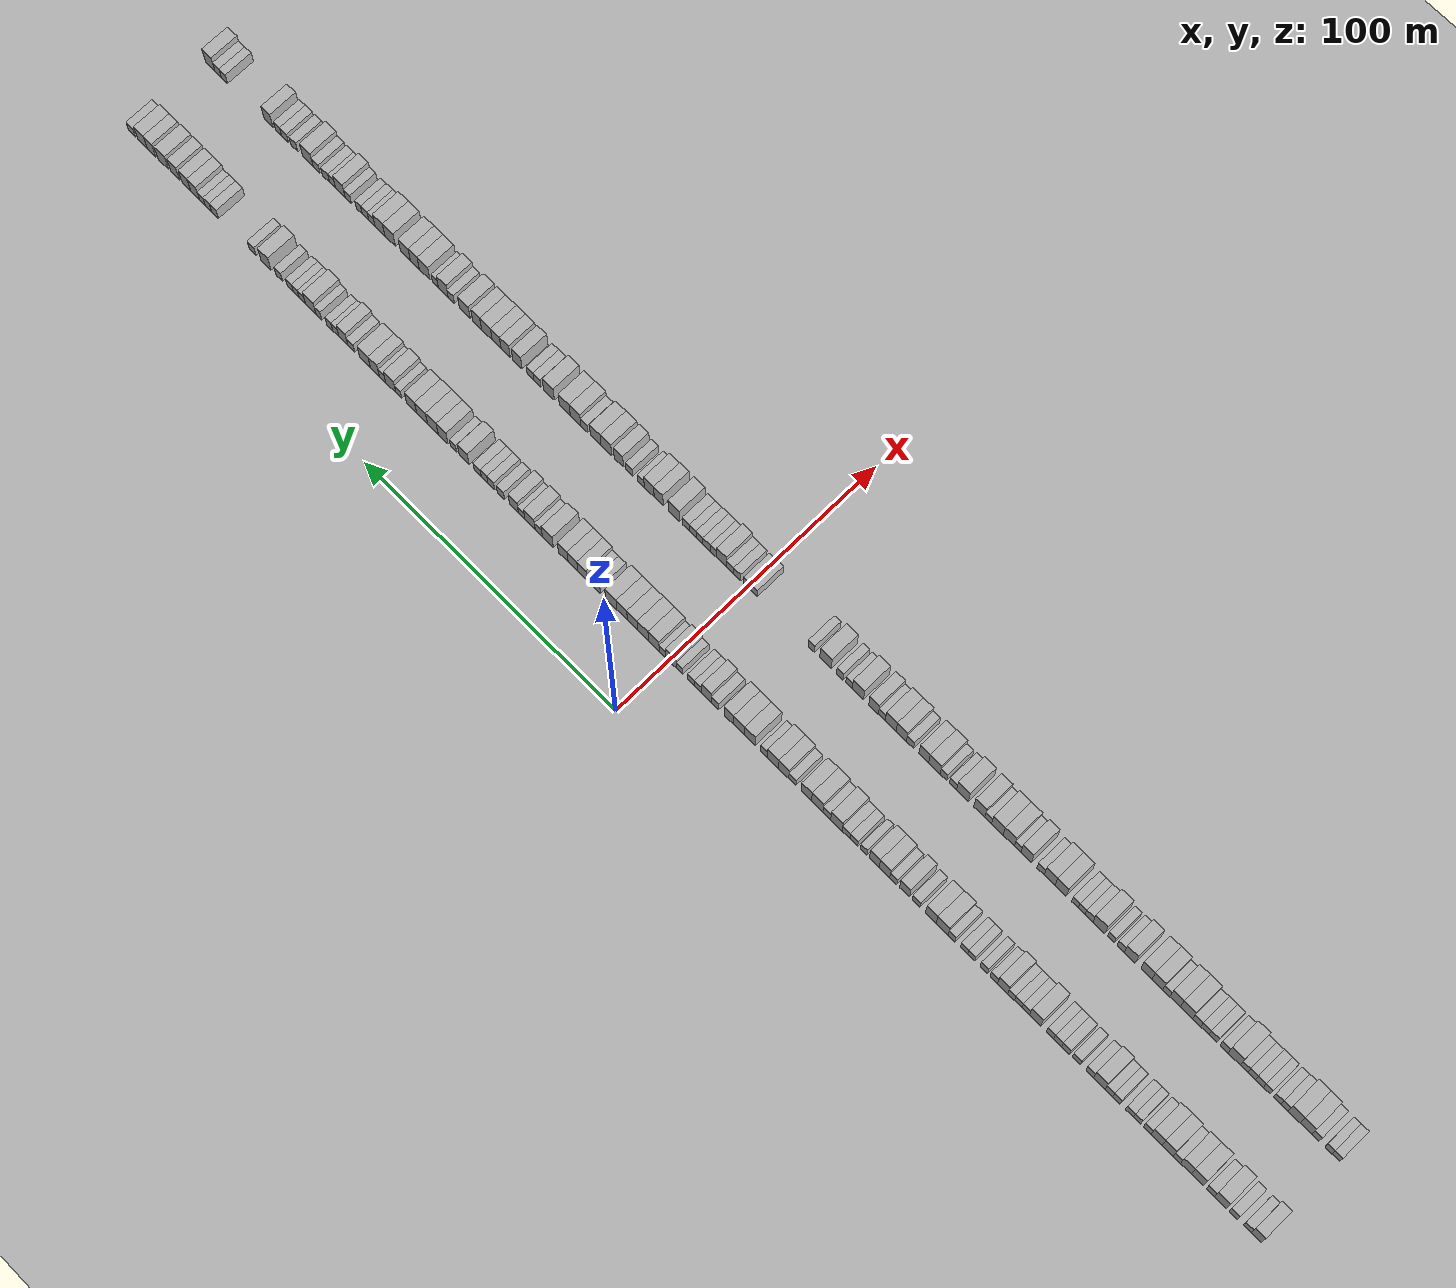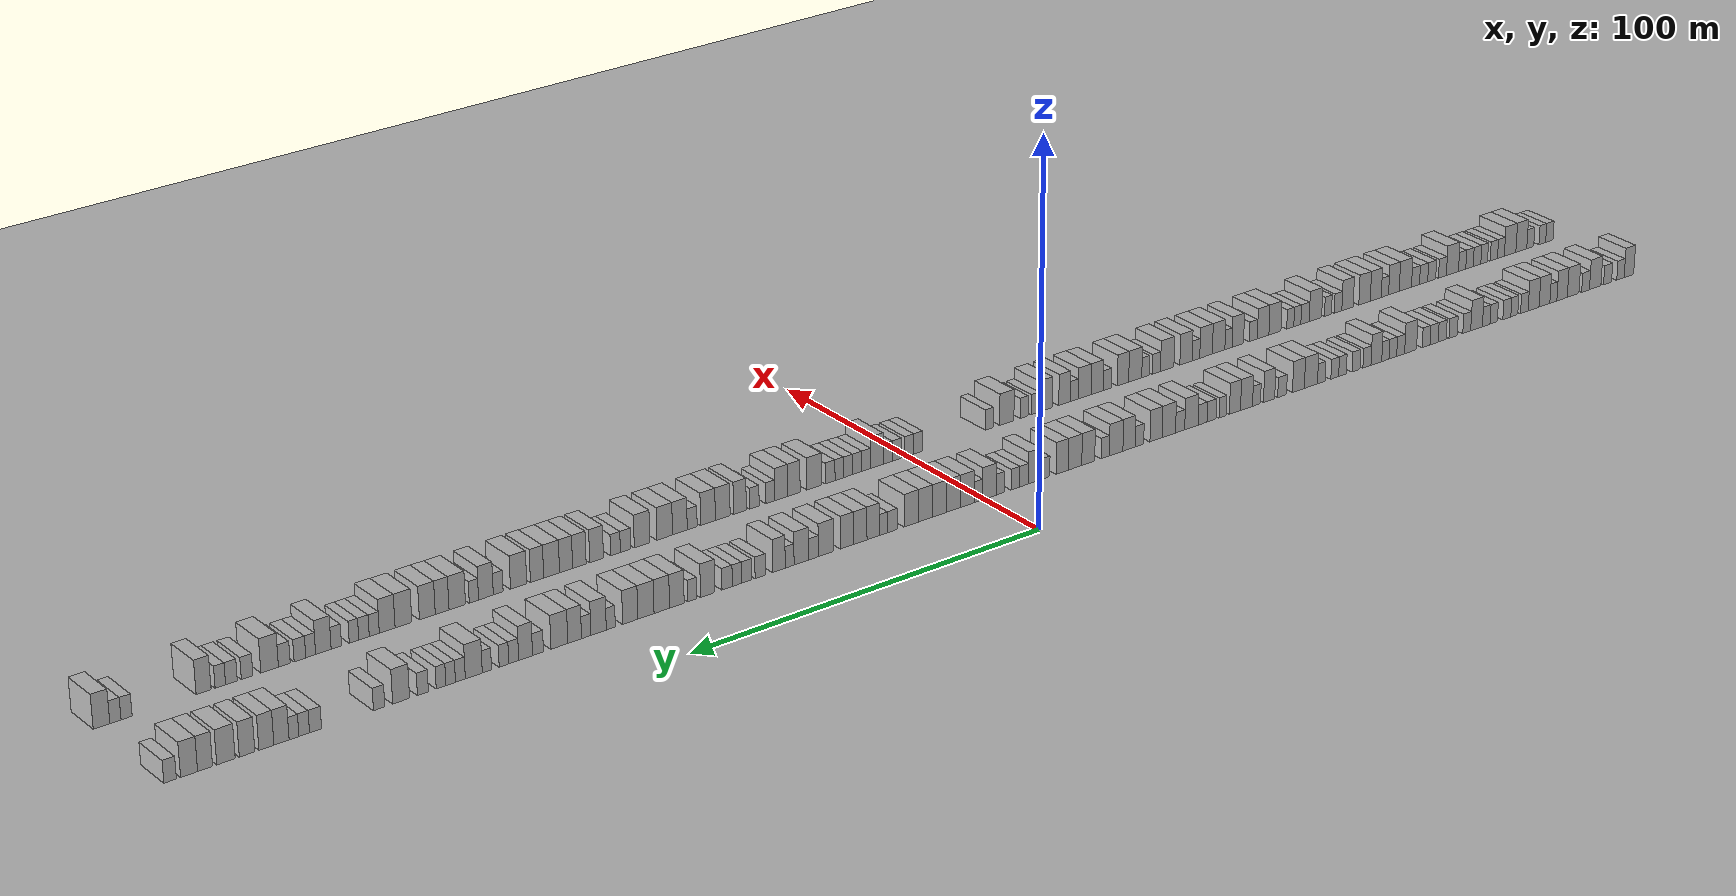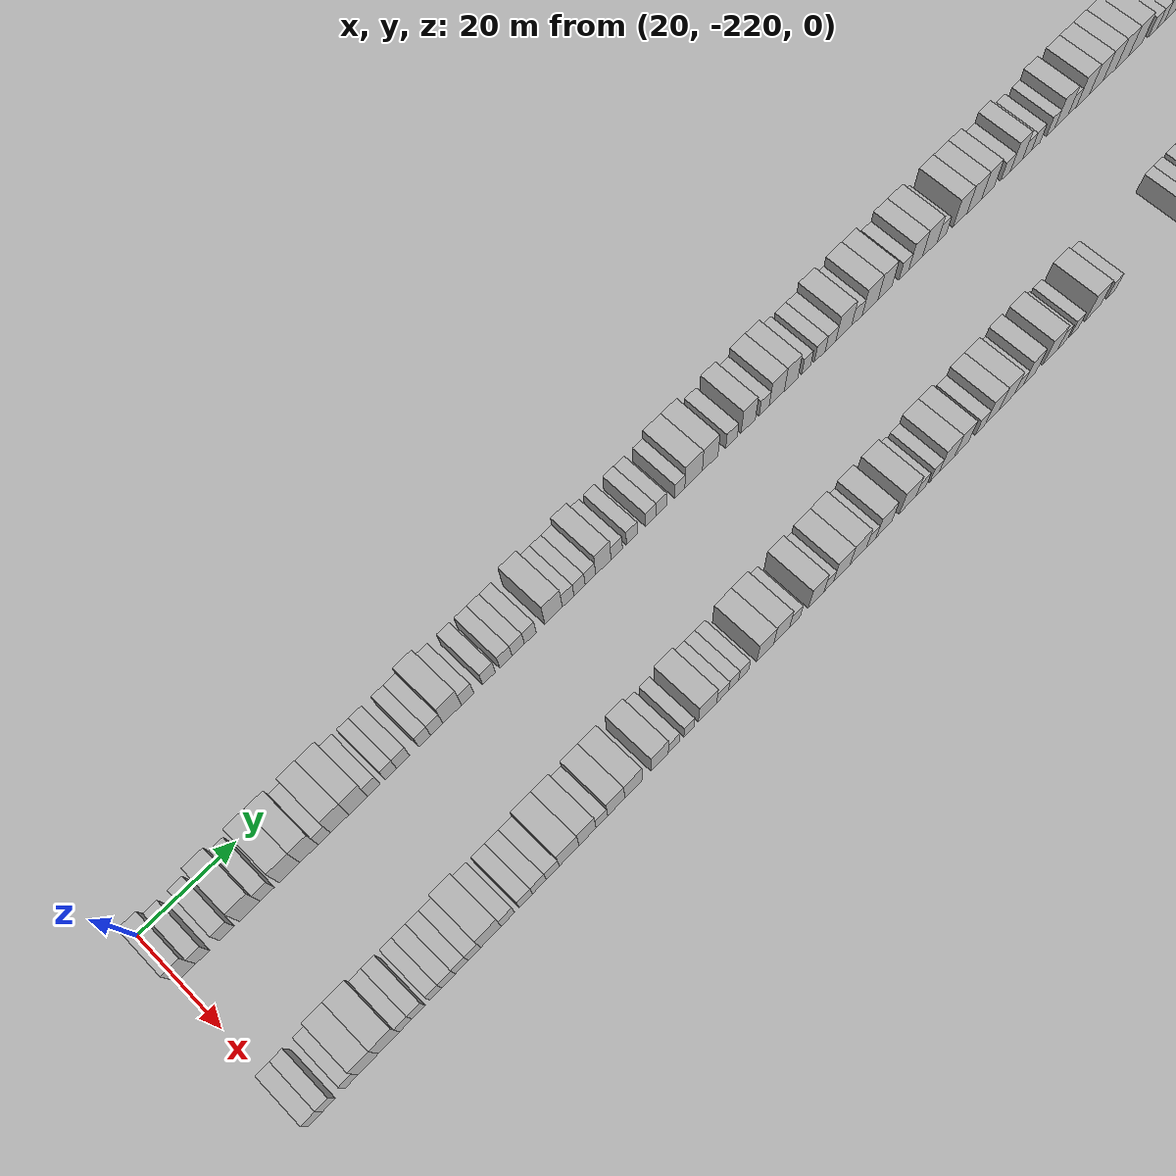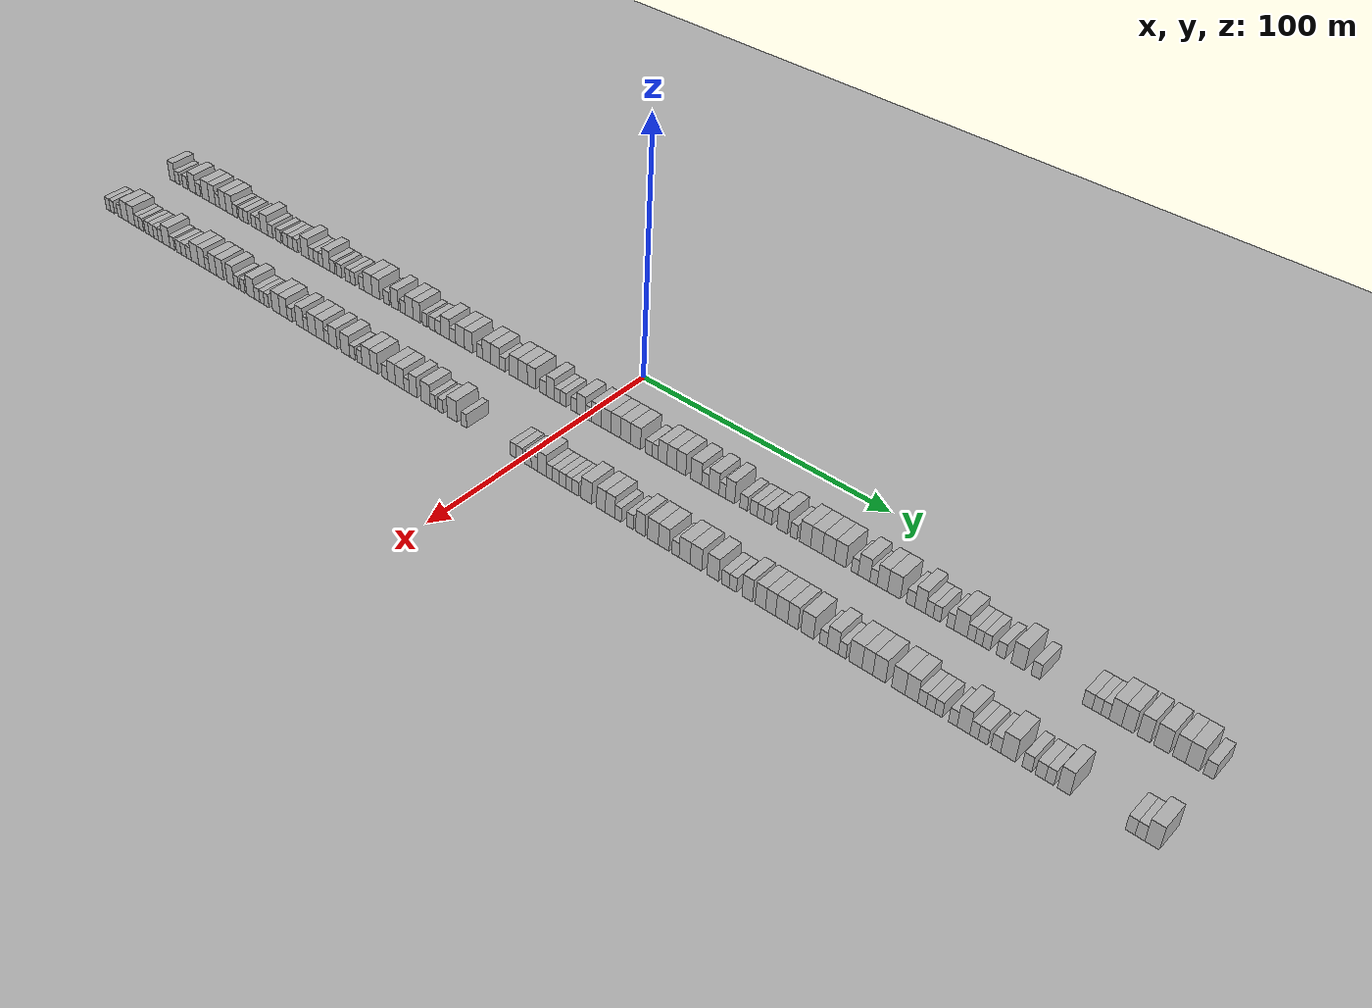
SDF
<?xml version="1.0" encoding="utf-8"?>

<sdf version="1.6">

   <world name="default">

      <gui fullscreen="0">

         <camera name="user_camera">

            <pose>-15 0 4.57585 0 0 0</pose>

            <view_controller>orbit</view_controller>

         </camera>

      </gui>

      <scene>

         <sky>

           <clouds>

             <speed>12</speed>

           </clouds>

         </sky>

         <ambient>0.4 0.4 0.4 1</ambient>

         <background>0.7 0.7 0.7 1</background>

         <shadows>1</shadows>

      </scene>

      <gravity>0 0 -9.8066</gravity>

      <magnetic_field>6e-06 2.3e-05 -4.2e-05</magnetic_field>

      <physics default="0" name="default_physics" type="ode">

         <ode>

            <solver>

               <type>quick</type>

               <iters>10</iters>

               <sor>1.0</sor>

               <use_dynamic_moi_rescaling>0</use_dynamic_moi_rescaling>

            </solver>

            <constraints>

               <cfm>0</cfm>

               <erp>0.2</erp>

               <contact_max_correcting_vel>100</contact_max_correcting_vel>

               <contact_surface_layer>0.001</contact_surface_layer>

            </constraints>

         </ode>

         <max_step_size>0.004</max_step_size>

         <real_time_factor>1</real_time_factor>

         <real_time_update_rate>250</real_time_update_rate>

      </physics>

      <light name="sun" type="directional">

         <cast_shadows>1</cast_shadows>

         <pose>0 0 10 0 0 0</pose>

         <diffuse>0.8 0.8 0.8 1</diffuse>

         <specular>0.2 0.2 0.2 1</specular>

         <attenuation>

            <range>1000</range>

            <constant>0.9</constant>

            <linear>0.01</linear>

            <quadratic>0.001</quadratic>

         </attenuation>

         <direction>-0.5 0.1 -0.9</direction>

      </light>

      <include>

         <name>ground_plane_1</name>

         <uri>model://HANNAS_ground_plane</uri>

         <pose>0 0 0  0 0 0</pose>

      </include>

      <include>

         <name>ground_plane_2</name>

         <uri>model://HANNAS_ground_plane</uri>

         <pose>100 0 0  0 0 0</pose>

      </include>

      <model name="building_1">

         <static>1</static>

         <pose frame="">25.0000 -218.1999 0 0.000000 0.000000 0.000000</pose>

         <link name="link">

            <pose frame="">0 0 4.50 0 0 0</pose>

            <collision name="collision">

               <geometry>

                  <box>

                     <size>10.0000 3.6002 9.0000</size>

                  </box>

               </geometry>

               <max_contacts>10</max_contacts>

               <surface>

                  <contact>

                     <ode/>

                  </contact>

                  <bounce/>

                  <friction>

                     <torsional>

                        <ode/>

                     </torsional>

                     <ode/>

                  </friction>

               </surface>

            </collision>

            <visual name="visual">

               <cast_shadows>0</cast_shadows>

               <geometry>

                  <box>

                     <size>10.0000 3.6002 9.0000</size>

                  </box>

               </geometry>

               <material>

                  <script>

                     <uri>model://HANNAS_wall/materials/scripts</uri>

                     <uri>model://HANNAS_wall/materials/textures</uri>

                     <name>vrc/HANNAS_wall</name>

                  </script>

               </material>

            </visual>

            <self_collide>0</self_collide>

            <enable_wind>0</enable_wind>

            <kinematic>0</kinematic>

         </link>

      </model>

      <model name="building_2">

         <static>1</static>

         <pose frame="">25.0000 -215.0210 0 0.000000 0.000000 0.000000</pose>

         <link name="link">

            <pose frame="">0 0 3.00 0 0 0</pose>

            <collision name="collision">

               <geometry>

                  <box>

                     <size>10.0000 2.7577 6.0000</size>

                  </box>

               </geometry>

               <max_contacts>10</max_contacts>

               <surface>

                  <contact>

                     <ode/>

                  </contact>

                  <bounce/>

                  <friction>

                     <torsional>

                        <ode/>

                     </torsional>

                     <ode/>

                  </friction>

               </surface>

            </collision>

            <visual name="visual">

               <cast_shadows>0</cast_shadows>

               <geometry>

                  <box>

                     <size>10.0000 2.7577 6.0000</size>

                  </box>

               </geometry>

               <material>

                  <script>

                     <uri>model://HANNAS_wall/materials/scripts</uri>

                     <uri>model://HANNAS_wall/materials/textures</uri>

                     <name>vrc/HANNAS_wall</name>

                  </script>

               </material>

            </visual>

            <self_collide>0</self_collide>

            <enable_wind>0</enable_wind>

            <kinematic>0</kinematic>

         </link>

      </model>

      <model name="building_3">

         <static>1</static>

         <pose frame="">25.0000 -210.1481 0 0.000000 0.000000 0.000000</pose>

         <link name="link">

            <pose frame="">0 0 3.00 0 0 0</pose>

            <collision name="collision">

               <geometry>

                  <box>

                     <size>10.0000 2.9882 6.0000</size>

                  </box>

               </geometry>

               <max_contacts>10</max_contacts>

               <surface>

                  <contact>

                     <ode/>

                  </contact>

                  <bounce/>

                  <friction>

                     <torsional>

                        <ode/>

                     </torsional>

                     <ode/>

                  </friction>

               </surface>

            </collision>

            <visual name="visual">

               <cast_shadows>0</cast_shadows>

               <geometry>

                  <box>

                     <size>10.0000 2.9882 6.0000</size>

                  </box>

               </geometry>

               <material>

                  <script>

                     <uri>model://HANNAS_wall/materials/scripts</uri>

                     <uri>model://HANNAS_wall/materials/textures</uri>

                     <name>vrc/HANNAS_wall</name>

                  </script>

               </material>

            </visual>

            <self_collide>0</self_collide>

            <enable_wind>0</enable_wind>

            <kinematic>0</kinematic>

         </link>

      </model>

      <model name="building_4">

         <static>1</static>

         <pose frame="">25.0000 -205.5099 0 0.000000 0.000000 0.000000</pose>

         <link name="link">

            <pose frame="">0 0 4.50 0 0 0</pose>

            <collision name="collision">

               <geometry>

                  <box>

                     <size>10.0000 4.2882 9.0000</size>

                  </box>

               </geometry>

               <max_contacts>10</max_contacts>

               <surface>

                  <contact>

                     <ode/>

                  </contact>

                  <bounce/>

                  <friction>

                     <torsional>

                        <ode/>

                     </torsional>

                     <ode/>

                  </friction>

               </surface>

            </collision>

            <visual name="visual">

               <cast_shadows>0</cast_shadows>

               <geometry>

                  <box>

                     <size>10.0000 4.2882 9.0000</size>

                  </box>

               </geometry>

               <material>

                  <script>

                     <uri>model://HANNAS_wall/materials/scripts</uri>

                     <uri>model://HANNAS_wall/materials/textures</uri>

                     <name>vrc/HANNAS_wall</name>

                  </script>

               </material>

            </visual>

            <self_collide>0</self_collide>

            <enable_wind>0</enable_wind>

            <kinematic>0</kinematic>

         </link>

      </model>

      <model name="building_5">

         <static>1</static>

         <pose frame="">25.0000 -201.9123 0 0.000000 0.000000 0.000000</pose>

         <link name="link">

            <pose frame="">0 0 3.00 0 0 0</pose>

            <collision name="collision">

               <geometry>

                  <box>

                     <size>10.0000 2.9070 6.0000</size>

                  </box>

               </geometry>

               <max_contacts>10</max_contacts>

               <surface>

                  <contact>

                     <ode/>

                  </contact>

                  <bounce/>

                  <friction>

                     <torsional>

                        <ode/>

                     </torsional>

                     <ode/>

                  </friction>

               </surface>

            </collision>

            <visual name="visual">

               <cast_shadows>0</cast_shadows>

               <geometry>

                  <box>

                     <size>10.0000 2.9070 6.0000</size>

                  </box>

               </geometry>

               <material>

                  <script>

                     <uri>model://HANNAS_wall/materials/scripts</uri>

                     <uri>model://HANNAS_wall/materials/textures</uri>

                     <name>vrc/HANNAS_wall</name>

                  </script>

               </material>

            </visual>

            <self_collide>0</self_collide>

            <enable_wind>0</enable_wind>

            <kinematic>0</kinematic>

         </link>

      </model>

      <model name="building_6">

         <static>1</static>

         <pose frame="">25.0000 -197.2956 0 0.000000 0.000000 0.000000</pose>

         <link name="link">

            <pose frame="">0 0 4.50 0 0 0</pose>

            <collision name="collision">

               <geometry>

                  <box>

                     <size>10.0000 4.3263 9.0000</size>

                  </box>

               </geometry>

               <max_contacts>10</max_contacts>

               <surface>

                  <contact>

                     <ode/>

                  </contact>

                  <bounce/>

                  <friction>

                     <torsional>

                        <ode/>

                     </torsional>

                     <ode/>

                  </friction>

               </surface>

            </collision>

            <visual name="visual">

               <cast_shadows>0</cast_shadows>

               <geometry>

                  <box>

                     <size>10.0000 4.3263 9.0000</size>

                  </box>

               </geometry>

               <material>

                  <script>

                     <uri>model://HANNAS_wall/materials/scripts</uri>

                     <uri>model://HANNAS_wall/materials/textures</uri>

                     <name>vrc/HANNAS_wall</name>

                  </script>

               </material>

            </visual>

            <self_collide>0</self_collide>

            <enable_wind>0</enable_wind>

            <kinematic>0</kinematic>

         </link>

      </model>

      <model name="building_7">

         <static>1</static>

         <pose frame="">25.0000 -193.2080 0 0.000000 0.000000 0.000000</pose>

         <link name="link">

            <pose frame="">0 0 4.50 0 0 0</pose>

            <collision name="collision">

               <geometry>

                  <box>

                     <size>10.0000 3.8490 9.0000</size>

                  </box>

               </geometry>

               <max_contacts>10</max_contacts>

               <surface>

                  <contact>

                     <ode/>

                  </contact>

                  <bounce/>

                  <friction>

                     <torsional>

                        <ode/>

                     </torsional>

                     <ode/>

                  </friction>

               </surface>

            </collision>

            <visual name="visual">

               <cast_shadows>0</cast_shadows>

               <geometry>

                  <box>

                     <size>10.0000 3.8490 9.0000</size>

                  </box>

               </geometry>

               <material>

                  <script>

                     <uri>model://HANNAS_wall/materials/scripts</uri>

                     <uri>model://HANNAS_wall/materials/textures</uri>

                     <name>vrc/HANNAS_wall</name>

                  </script>

               </material>

            </visual>

            <self_collide>0</self_collide>

            <enable_wind>0</enable_wind>

            <kinematic>0</kinematic>

         </link>

      </model>

      <model name="building_8">

         <static>1</static>

         <pose frame="">25.0000 -189.9896 0 0.000000 0.000000 0.000000</pose>

         <link name="link">

            <pose frame="">0 0 3.00 0 0 0</pose>

            <collision name="collision">

               <geometry>

                  <box>

                     <size>10.0000 2.5877 6.0000</size>

                  </box>

               </geometry>

               <max_contacts>10</max_contacts>

               <surface>

                  <contact>

                     <ode/>

                  </contact>

                  <bounce/>

                  <friction>

                     <torsional>

                        <ode/>

                     </torsional>

                     <ode/>

                  </friction>

               </surface>

            </collision>

            <visual name="visual">

               <cast_shadows>0</cast_shadows>

               <geometry>

                  <box>

                     <size>10.0000 2.5877 6.0000</size>

                  </box>

               </geometry>

               <material>

                  <script>

                     <uri>model://HANNAS_wall/materials/scripts</uri>

                     <uri>model://HANNAS_wall/materials/textures</uri>

                     <name>vrc/HANNAS_wall</name>

                  </script>

               </material>

            </visual>

            <self_collide>0</self_collide>

            <enable_wind>0</enable_wind>

            <kinematic>0</kinematic>

         </link>

      </model>

      <model name="building_9">

         <static>1</static>

         <pose frame="">25.0000 -186.7082 0 0.000000 0.000000 0.000000</pose>

         <link name="link">

            <pose frame="">0 0 4.50 0 0 0</pose>

            <collision name="collision">

               <geometry>

                  <box>

                     <size>10.0000 3.9751 9.0000</size>

                  </box>

               </geometry>

               <max_contacts>10</max_contacts>

               <surface>

                  <contact>

                     <ode/>

                  </contact>

                  <bounce/>

                  <friction>

                     <torsional>

                        <ode/>

                     </torsional>

                     <ode/>

                  </friction>

               </surface>

            </collision>

            <visual name="visual">

               <cast_shadows>0</cast_shadows>

               <geometry>

                  <box>

                     <size>10.0000 3.9751 9.0000</size>

                  </box>

               </geometry>

               <material>

                  <script>

                     <uri>model://HANNAS_wall/materials/scripts</uri>

                     <uri>model://HANNAS_wall/materials/textures</uri>

                     <name>vrc/HANNAS_wall</name>

                  </script>

               </material>

            </visual>

            <self_collide>0</self_collide>

            <enable_wind>0</enable_wind>

            <kinematic>0</kinematic>

         </link>

      </model>

      <model name="building_10">

         <static>1</static>

         <pose frame="">25.0000 -182.7124 0 0.000000 0.000000 0.000000</pose>

         <link name="link">

            <pose frame="">0 0 4.50 0 0 0</pose>

            <collision name="collision">

               <geometry>

                  <box>

                     <size>10.0000 4.0163 9.0000</size>

                  </box>

               </geometry>

               <max_contacts>10</max_contacts>

               <surface>

                  <contact>

                     <ode/>

                  </contact>

                  <bounce/>

                  <friction>

                     <torsional>

                        <ode/>

                     </torsional>

                     <ode/>

                  </friction>

               </surface>

            </collision>

            <visual name="visual">

               <cast_shadows>0</cast_shadows>

               <geometry>

                  <box>

                     <size>10.0000 4.0163 9.0000</size>

                  </box>

               </geometry>

               <material>

                  <script>

                     <uri>model://HANNAS_wall/materials/scripts</uri>

                     <uri>model://HANNAS_wall/materials/textures</uri>

                     <name>vrc/HANNAS_wall</name>

                  </script>

               </material>

            </visual>

            <self_collide>0</self_collide>

            <enable_wind>0</enable_wind>

            <kinematic>0</kinematic>

         </link>

      </model>

      <model name="building_11">

         <static>1</static>

         <pose frame="">25.0000 -179.3322 0 0.000000 0.000000 0.000000</pose>

         <link name="link">

            <pose frame="">0 0 3.00 0 0 0</pose>

            <collision name="collision">

               <geometry>

                  <box>

                     <size>10.0000 2.7441 6.0000</size>

                  </box>

               </geometry>

               <max_contacts>10</max_contacts>

               <surface>

                  <contact>

                     <ode/>

                  </contact>

                  <bounce/>

                  <friction>

                     <torsional>

                        <ode/>

                     </torsional>

                     <ode/>

                  </friction>

               </surface>

            </collision>

            <visual name="visual">

               <cast_shadows>0</cast_shadows>

               <geometry>

                  <box>

                     <size>10.0000 2.7441 6.0000</size>

                  </box>

               </geometry>

               <material>

                  <script>

                     <uri>model://HANNAS_wall/materials/scripts</uri>

                     <uri>model://HANNAS_wall/materials/textures</uri>

                     <name>vrc/HANNAS_wall</name>

                  </script>

               </material>

            </visual>

            <self_collide>0</self_collide>

            <enable_wind>0</enable_wind>

            <kinematic>0</kinematic>

         </link>

      </model>

      <model name="building_12">

         <static>1</static>

         <pose frame="">25.0000 -175.6917 0 0.000000 0.000000 0.000000</pose>

         <link name="link">

            <pose frame="">0 0 3.00 0 0 0</pose>

            <collision name="collision">

               <geometry>

                  <box>

                     <size>10.0000 2.5370 6.0000</size>

                  </box>

               </geometry>

               <max_contacts>10</max_contacts>

               <surface>

                  <contact>

                     <ode/>

                  </contact>

                  <bounce/>

                  <friction>

                     <torsional>

                        <ode/>

                     </torsional>

                     <ode/>

                  </friction>

               </surface>

            </collision>

            <visual name="visual">

               <cast_shadows>0</cast_shadows>

               <geometry>

                  <box>

                     <size>10.0000 2.5370 6.0000</size>

                  </box>

               </geometry>

               <material>

                  <script>

                     <uri>model://HANNAS_wall/materials/scripts</uri>

                     <uri>model://HANNAS_wall/materials/textures</uri>

                     <name>vrc/HANNAS_wall</name>

                  </script>

               </material>

            </visual>

            <self_collide>0</self_collide>

            <enable_wind>0</enable_wind>

            <kinematic>0</kinematic>

         </link>

      </model>

      <model name="building_13">

         <static>1</static>

         <pose frame="">25.0000 -172.9795 0 0.000000 0.000000 0.000000</pose>

         <link name="link">

            <pose frame="">0 0 3.00 0 0 0</pose>

            <collision name="collision">

               <geometry>

                  <box>

                     <size>10.0000 2.8872 6.0000</size>

                  </box>

               </geometry>

               <max_contacts>10</max_contacts>

               <surface>

                  <contact>

                     <ode/>

                  </contact>

                  <bounce/>

                  <friction>

                     <torsional>

                        <ode/>

                     </torsional>

                     <ode/>

                  </friction>

               </surface>

            </collision>

            <visual name="visual">

               <cast_shadows>0</cast_shadows>

               <geometry>

                  <box>

                     <size>10.0000 2.8872 6.0000</size>

                  </box>

               </geometry>

               <material>

                  <script>

                     <uri>model://HANNAS_wall/materials/scripts</uri>

                     <uri>model://HANNAS_wall/materials/textures</uri>

                     <name>vrc/HANNAS_wall</name>

                  </script>

               </material>

            </visual>

            <self_collide>0</self_collide>

            <enable_wind>0</enable_wind>

            <kinematic>0</kinematic>

         </link>

      </model>

      <model name="building_14">

         <static>1</static>

         <pose frame="">25.0000 -168.2196 0 0.000000 0.000000 0.000000</pose>

         <link name="link">

            <pose frame="">0 0 3.00 0 0 0</pose>

            <collision name="collision">

               <geometry>

                  <box>

                     <size>10.0000 2.6327 6.0000</size>

                  </box>

               </geometry>

               <max_contacts>10</max_contacts>

               <surface>

                  <contact>

                     <ode/>

                  </contact>

                  <bounce/>

                  <friction>

                     <torsional>

                        <ode/>

                     </torsional>

                     <ode/>

                  </friction>

               </surface>

            </collision>

            <visual name="visual">

               <cast_shadows>0</cast_shadows>

               <geometry>

                  <box>

                     <size>10.0000 2.6327 6.0000</size>

                  </box>

               </geometry>

               <material>

                  <script>

                     <uri>model://HANNAS_wall/materials/scripts</uri>

                     <uri>model://HANNAS_wall/materials/textures</uri>

                     <name>vrc/HANNAS_wall</name>

                  </script>

               </material>

            </visual>

            <self_collide>0</self_collide>

            <enable_wind>0</enable_wind>

            <kinematic>0</kinematic>

         </link>

      </model>

      <model name="building_15">

         <static>1</static>

         <pose frame="">25.0000 -165.5320 0 0.000000 0.000000 0.000000</pose>

         <link name="link">

            <pose frame="">0 0 3.00 0 0 0</pose>

            <collision name="collision">

               <geometry>

                  <box>

                     <size>10.0000 2.7424 6.0000</size>

                  </box>

               </geometry>

               <max_contacts>10</max_contacts>

               <surface>

                  <contact>

                     <ode/>

                  </contact>

                  <bounce/>

                  <friction>

                     <torsional>

                        <ode/>

                     </torsional>

                     <ode/>

                  </friction>

               </surface>

            </collision>

            <visual name="visual">

               <cast_shadows>0</cast_shadows>

               <geometry>

                  <box>

                     <size>10.0000 2.7424 6.0000</size>

                  </box>

               </geometry>

               <material>

                  <script>

                     <uri>model://HANNAS_wall/materials/scripts</uri>

                     <uri>model://HANNAS_wall/materials/textures</uri>

                     <name>vrc/HANNAS_wall</name>

                  </script>

               </material>

            </visual>

            <self_collide>0</self_collide>

            <enable_wind>0</enable_wind>

            <kinematic>0</kinematic>

         </link>

      </model>

      <model name="building_16">

         <static>1</static>

         <pose frame="">25.0000 -162.0608 0 0.000000 0.000000 0.000000</pose>

         <link name="link">

            <pose frame="">0 0 4.50 0 0 0</pose>

            <collision name="collision">

               <geometry>

                  <box>

                     <size>10.0000 4.2000 9.0000</size>

                  </box>

               </geometry>

               <max_contacts>10</max_contacts>

               <surface>

                  <contact>

                     <ode/>

                  </contact>

                  <bounce/>

                  <friction>

                     <torsional>

                        <ode/>

                     </torsional>

                     <ode/>

                  </friction>

               </surface>

            </collision>

            <visual name="visual">

               <cast_shadows>0</cast_shadows>

               <geometry>

                  <box>

                     <size>10.0000 4.2000 9.0000</size>

                  </box>

               </geometry>

               <material>

                  <script>

                     <uri>model://HANNAS_wall/materials/scripts</uri>

                     <uri>model://HANNAS_wall/materials/textures</uri>

                     <name>vrc/HANNAS_wall</name>

                  </script>

               </material>

            </visual>

            <self_collide>0</self_collide>

            <enable_wind>0</enable_wind>

            <kinematic>0</kinematic>

         </link>

      </model>

      <model name="building_17">

         <static>1</static>

         <pose frame="">25.0000 -158.5487 0 0.000000 0.000000 0.000000</pose>

         <link name="link">

            <pose frame="">0 0 3.00 0 0 0</pose>

            <collision name="collision">

               <geometry>

                  <box>

                     <size>10.0000 2.8243 6.0000</size>

                  </box>

               </geometry>

               <max_contacts>10</max_contacts>

               <surface>

                  <contact>

                     <ode/>

                  </contact>

                  <bounce/>

                  <friction>

                     <torsional>

                        <ode/>

                     </torsional>

                     <ode/>

                  </friction>

               </surface>

            </collision>

            <visual name="visual">

               <cast_shadows>0</cast_shadows>

               <geometry>

                  <box>

                     <size>10.0000 2.8243 6.0000</size>

                  </box>

               </geometry>

               <material>

                  <script>

                     <uri>model://HANNAS_wall/materials/scripts</uri>

                     <uri>model://HANNAS_wall/materials/textures</uri>

                     <name>vrc/HANNAS_wall</name>

                  </script>

               </material>

            </visual>

            <self_collide>0</self_collide>

            <enable_wind>0</enable_wind>

            <kinematic>0</kinematic>

         </link>

      </model>

      <model name="building_18">

         <static>1</static>

         <pose frame="">25.0000 -153.6784 0 0.000000 0.000000 0.000000</pose>

         <link name="link">

            <pose frame="">0 0 3.00 0 0 0</pose>

            <collision name="collision">

               <geometry>

                  <box>

                     <size>10.0000 2.9164 6.0000</size>

                  </box>

               </geometry>

               <max_contacts>10</max_contacts>

               <surface>

                  <contact>

                     <ode/>

                  </contact>

                  <bounce/>

                  <friction>

                     <torsional>

                        <ode/>

                     </torsional>

                     <ode/>

                  </friction>

               </surface>

            </collision>

            <visual name="visual">

               <cast_shadows>0</cast_shadows>

               <geometry>

                  <box>

                     <size>10.0000 2.9164 6.0000</size>

                  </box>

               </geometry>

               <material>

                  <script>

                     <uri>model://HANNAS_wall/materials/scripts</uri>

                     <uri>model://HANNAS_wall/materials/textures</uri>

                     <name>vrc/HANNAS_wall</name>

                  </script>

               </material>

            </visual>

            <self_collide>0</self_collide>

            <enable_wind>0</enable_wind>

            <kinematic>0</kinematic>

         </link>

      </model>

      <model name="building_19">

         <static>1</static>

         <pose frame="">25.0000 -149.7978 0 0.000000 0.000000 0.000000</pose>

         <link name="link">

            <pose frame="">0 0 3.00 0 0 0</pose>

            <collision name="collision">

               <geometry>

                  <box>

                     <size>10.0000 2.8447 6.0000</size>

                  </box>

               </geometry>

               <max_contacts>10</max_contacts>

               <surface>

                  <contact>

                     <ode/>

                  </contact>

                  <bounce/>

                  <friction>

                     <torsional>

                        <ode/>

                     </torsional>

                     <ode/>

                  </friction>

               </surface>

            </collision>

            <visual name="visual">

               <cast_shadows>0</cast_shadows>

               <geometry>

                  <box>

                     <size>10.0000 2.8447 6.0000</size>

                  </box>

               </geometry>

               <material>

                  <script>

                     <uri>model://HANNAS_wall/materials/scripts</uri>

                     <uri>model://HANNAS_wall/materials/textures</uri>

                     <name>vrc/HANNAS_wall</name>

                  </script>

               </material>

            </visual>

            <self_collide>0</self_collide>

            <enable_wind>0</enable_wind>

            <kinematic>0</kinematic>

         </link>

      </model>

      <model name="building_20">

         <static>1</static>

         <pose frame="">25.0000 -146.9316 0 0.000000 0.000000 0.000000</pose>

         <link name="link">

            <pose frame="">0 0 3.00 0 0 0</pose>

            <collision name="collision">

               <geometry>

                  <box>

                     <size>10.0000 2.8878 6.0000</size>

                  </box>

               </geometry>

               <max_contacts>10</max_contacts>

               <surface>

                  <contact>

                     <ode/>

                  </contact>

                  <bounce/>

                  <friction>

                     <torsional>

                        <ode/>

                     </torsional>

                     <ode/>

                  </friction>

               </surface>

            </collision>

            <visual name="visual">

               <cast_shadows>0</cast_shadows>

               <geometry>

                  <box>

                     <size>10.0000 2.8878 6.0000</size>

                  </box>

               </geometry>

               <material>

                  <script>

                     <uri>model://HANNAS_wall/materials/scripts</uri>

                     <uri>model://HANNAS_wall/materials/textures</uri>

                     <name>vrc/HANNAS_wall</name>

                  </script>

               </material>

            </visual>

            <self_collide>0</self_collide>

            <enable_wind>0</enable_wind>

            <kinematic>0</kinematic>

         </link>

      </model>

      <model name="building_21">

         <static>1</static>

         <pose frame="">25.0000 -144.1135 0 0.000000 0.000000 0.000000</pose>

         <link name="link">

            <pose frame="">0 0 3.00 0 0 0</pose>

            <collision name="collision">

               <geometry>

                  <box>

                     <size>10.0000 2.7484 6.0000</size>

                  </box>

               </geometry>

               <max_contacts>10</max_contacts>

               <surface>

                  <contact>

                     <ode/>

                  </contact>

                  <bounce/>

                  <friction>

                     <torsional>

                        <ode/>

                     </torsional>

                     <ode/>

                  </friction>

               </surface>

            </collision>

            <visual name="visual">

               <cast_shadows>0</cast_shadows>

               <geometry>

                  <box>

                     <size>10.0000 2.7484 6.0000</size>

                  </box>

               </geometry>

               <material>

                  <script>

                     <uri>model://HANNAS_wall/materials/scripts</uri>

                     <uri>model://HANNAS_wall/materials/textures</uri>

                     <name>vrc/HANNAS_wall</name>

                  </script>

               </material>

            </visual>

            <self_collide>0</self_collide>

            <enable_wind>0</enable_wind>

            <kinematic>0</kinematic>

         </link>

      </model>

      <model name="building_22">

         <static>1</static>

         <pose frame="">25.0000 -138.6592 0 0.000000 0.000000 0.000000</pose>

         <link name="link">

            <pose frame="">0 0 4.50 0 0 0</pose>

            <collision name="collision">

               <geometry>

                  <box>

                     <size>10.0000 4.1602 9.0000</size>

                  </box>

               </geometry>

               <max_contacts>10</max_contacts>

               <surface>

                  <contact>

                     <ode/>

                  </contact>

                  <bounce/>

                  <friction>

                     <torsional>

                        <ode/>

                     </torsional>

                     <ode/>

                  </friction>

               </surface>

            </collision>

            <visual name="visual">

               <cast_shadows>0</cast_shadows>

               <geometry>

                  <box>

                     <size>10.0000 4.1602 9.0000</size>

                  </box>

               </geometry>

               <material>

                  <script>

                     <uri>model://HANNAS_wall/materials/scripts</uri>

                     <uri>model://HANNAS_wall/materials/textures</uri>

                     <name>vrc/HANNAS_wall</name>

                  </script>

               </material>

            </visual>

            <self_collide>0</self_collide>

            <enable_wind>0</enable_wind>

            <kinematic>0</kinematic>

         </link>

      </model>

      <model name="building_23">

         <static>1</static>

         <pose frame="">25.0000 -135.1899 0 0.000000 0.000000 0.000000</pose>

         <link name="link">

            <pose frame="">0 0 3.00 0 0 0</pose>

            <collision name="collision">

               <geometry>

                  <box>

                     <size>10.0000 2.7784 6.0000</size>

                  </box>

               </geometry>

               <max_contacts>10</max_contacts>

               <surface>

                  <contact>

                     <ode/>

                  </contact>

                  <bounce/>

                  <friction>

                     <torsional>

                        <ode/>

                     </torsional>

                     <ode/>

                  </friction>

               </surface>

            </collision>

            <visual name="visual">

               <cast_shadows>0</cast_shadows>

               <geometry>

                  <box>

                     <size>10.0000 2.7784 6.0000</size>

                  </box>

               </geometry>

               <material>

                  <script>

                     <uri>model://HANNAS_wall/materials/scripts</uri>

                     <uri>model://HANNAS_wall/materials/textures</uri>

                     <name>vrc/HANNAS_wall</name>

                  </script>

               </material>

            </visual>

            <self_collide>0</self_collide>

            <enable_wind>0</enable_wind>

            <kinematic>0</kinematic>

         </link>

      </model>

      <model name="building_24">

         <static>1</static>

         <pose frame="">25.0000 -132.4624 0 0.000000 0.000000 0.000000</pose>

         <link name="link">

            <pose frame="">0 0 3.00 0 0 0</pose>

            <collision name="collision">

               <geometry>

                  <box>

                     <size>10.0000 2.6766 6.0000</size>

                  </box>

               </geometry>

               <max_contacts>10</max_contacts>

               <surface>

                  <contact>

                     <ode/>

                  </contact>

                  <bounce/>

                  <friction>

                     <torsional>

                        <ode/>

                     </torsional>

                     <ode/>

                  </friction>

               </surface>

            </collision>

            <visual name="visual">

               <cast_shadows>0</cast_shadows>

               <geometry>

                  <box>

                     <size>10.0000 2.6766 6.0000</size>

                  </box>

               </geometry>

               <material>

                  <script>

                     <uri>model://HANNAS_wall/materials/scripts</uri>

                     <uri>model://HANNAS_wall/materials/textures</uri>

                     <name>vrc/HANNAS_wall</name>

                  </script>

               </material>

            </visual>

            <self_collide>0</self_collide>

            <enable_wind>0</enable_wind>

            <kinematic>0</kinematic>

         </link>

      </model>

      <model name="building_25">

         <static>1</static>

         <pose frame="">25.0000 -129.8567 0 0.000000 0.000000 0.000000</pose>

         <link name="link">

            <pose frame="">0 0 3.00 0 0 0</pose>

            <collision name="collision">

               <geometry>

                  <box>

                     <size>10.0000 2.5349 6.0000</size>

                  </box>

               </geometry>

               <max_contacts>10</max_contacts>

               <surface>

                  <contact>

                     <ode/>

                  </contact>

                  <bounce/>

                  <friction>

                     <torsional>

                        <ode/>

                     </torsional>

                     <ode/>

                  </friction>

               </surface>

            </collision>

            <visual name="visual">

               <cast_shadows>0</cast_shadows>

               <geometry>

                  <box>

                     <size>10.0000 2.5349 6.0000</size>

                  </box>

               </geometry>

               <material>

                  <script>

                     <uri>model://HANNAS_wall/materials/scripts</uri>

                     <uri>model://HANNAS_wall/materials/textures</uri>

                     <name>vrc/HANNAS_wall</name>

                  </script>

               </material>

            </visual>

            <self_collide>0</self_collide>

            <enable_wind>0</enable_wind>

            <kinematic>0</kinematic>

         </link>

      </model>

      <model name="building_26">

         <static>1</static>

         <pose frame="">25.0000 -126.7291 0 0.000000 0.000000 0.000000</pose>

         <link name="link">

            <pose frame="">0 0 4.50 0 0 0</pose>

            <collision name="collision">

               <geometry>

                  <box>

                     <size>10.0000 3.7203 9.0000</size>

                  </box>

               </geometry>

               <max_contacts>10</max_contacts>

               <surface>

                  <contact>

                     <ode/>

                  </contact>

                  <bounce/>

                  <friction>

                     <torsional>

                        <ode/>

                     </torsional>

                     <ode/>

                  </friction>

               </surface>

            </collision>

            <visual name="visual">

               <cast_shadows>0</cast_shadows>

               <geometry>

                  <box>

                     <size>10.0000 3.7203 9.0000</size>

                  </box>

               </geometry>

               <material>

                  <script>

                     <uri>model://HANNAS_wall/materials/scripts</uri>

                     <uri>model://HANNAS_wall/materials/textures</uri>

                     <name>vrc/HANNAS_wall</name>

                  </script>

               </material>

            </visual>

            <self_collide>0</self_collide>

            <enable_wind>0</enable_wind>

            <kinematic>0</kinematic>

         </link>

      </model>

      <model name="building_27">

         <static>1</static>

         <pose frame="">25.0000 -123.4725 0 0.000000 0.000000 0.000000</pose>

         <link name="link">

            <pose frame="">0 0 3.00 0 0 0</pose>

            <collision name="collision">

               <geometry>

                  <box>

                     <size>10.0000 2.7929 6.0000</size>

                  </box>

               </geometry>

               <max_contacts>10</max_contacts>

               <surface>

                  <contact>

                     <ode/>

                  </contact>

                  <bounce/>

                  <friction>

                     <torsional>

                        <ode/>

                     </torsional>

                     <ode/>

                  </friction>

               </surface>

            </collision>

            <visual name="visual">

               <cast_shadows>0</cast_shadows>

               <geometry>

                  <box>

                     <size>10.0000 2.7929 6.0000</size>

                  </box>

               </geometry>

               <material>

                  <script>

                     <uri>model://HANNAS_wall/materials/scripts</uri>

                     <uri>model://HANNAS_wall/materials/textures</uri>

                     <name>vrc/HANNAS_wall</name>

                  </script>

               </material>

            </visual>

            <self_collide>0</self_collide>

            <enable_wind>0</enable_wind>

            <kinematic>0</kinematic>

         </link>

      </model>

      <model name="building_28">

         <static>1</static>

         <pose frame="">25.0000 -119.7247 0 0.000000 0.000000 0.000000</pose>

         <link name="link">

            <pose frame="">0 0 3.00 0 0 0</pose>

            <collision name="collision">

               <geometry>

                  <box>

                     <size>10.0000 2.7026 6.0000</size>

                  </box>

               </geometry>

               <max_contacts>10</max_contacts>

               <surface>

                  <contact>

                     <ode/>

                  </contact>

                  <bounce/>

                  <friction>

                     <torsional>

                        <ode/>

                     </torsional>

                     <ode/>

                  </friction>

               </surface>

            </collision>

            <visual name="visual">

               <cast_shadows>0</cast_shadows>

               <geometry>

                  <box>

                     <size>10.0000 2.7026 6.0000</size>

                  </box>

               </geometry>

               <material>

                  <script>

                     <uri>model://HANNAS_wall/materials/scripts</uri>

                     <uri>model://HANNAS_wall/materials/textures</uri>

                     <name>vrc/HANNAS_wall</name>

                  </script>

               </material>

            </visual>

            <self_collide>0</self_collide>

            <enable_wind>0</enable_wind>

            <kinematic>0</kinematic>

         </link>

      </model>

      <model name="building_29">

         <static>1</static>

         <pose frame="">25.0000 -115.0625 0 0.000000 0.000000 0.000000</pose>

         <link name="link">

            <pose frame="">0 0 3.00 0 0 0</pose>

            <collision name="collision">

               <geometry>

                  <box>

                     <size>10.0000 2.6219 6.0000</size>

                  </box>

               </geometry>

               <max_contacts>10</max_contacts>

               <surface>

                  <contact>

                     <ode/>

                  </contact>

                  <bounce/>

                  <friction>

                     <torsional>

                        <ode/>

                     </torsional>

                     <ode/>

                  </friction>

               </surface>

            </collision>

            <visual name="visual">

               <cast_shadows>0</cast_shadows>

               <geometry>

                  <box>

                     <size>10.0000 2.6219 6.0000</size>

                  </box>

               </geometry>

               <material>

                  <script>

                     <uri>model://HANNAS_wall/materials/scripts</uri>

                     <uri>model://HANNAS_wall/materials/textures</uri>

                     <name>vrc/HANNAS_wall</name>

                  </script>

               </material>

            </visual>

            <self_collide>0</self_collide>

            <enable_wind>0</enable_wind>

            <kinematic>0</kinematic>

         </link>

      </model>

      <model name="building_30">

         <static>1</static>

         <pose frame="">25.0000 -112.4210 0 0.000000 0.000000 0.000000</pose>

         <link name="link">

            <pose frame="">0 0 3.00 0 0 0</pose>

            <collision name="collision">

               <geometry>

                  <box>

                     <size>10.0000 2.6610 6.0000</size>

                  </box>

               </geometry>

               <max_contacts>10</max_contacts>

               <surface>

                  <contact>

                     <ode/>

                  </contact>

                  <bounce/>

                  <friction>

                     <torsional>

                        <ode/>

                     </torsional>

                     <ode/>

                  </friction>

               </surface>

            </collision>

            <visual name="visual">

               <cast_shadows>0</cast_shadows>

               <geometry>

                  <box>

                     <size>10.0000 2.6610 6.0000</size>

                  </box>

               </geometry>

               <material>

                  <script>

                     <uri>model://HANNAS_wall/materials/scripts</uri>

                     <uri>model://HANNAS_wall/materials/textures</uri>

                     <name>vrc/HANNAS_wall</name>

                  </script>

               </material>

            </visual>

            <self_collide>0</self_collide>

            <enable_wind>0</enable_wind>

            <kinematic>0</kinematic>

         </link>

      </model>

      <model name="building_31">

         <static>1</static>

         <pose frame="">25.0000 -107.8168 0 0.000000 0.000000 0.000000</pose>

         <link name="link">

            <pose frame="">0 0 3.00 0 0 0</pose>

            <collision name="collision">

               <geometry>

                  <box>

                     <size>10.0000 2.5475 6.0000</size>

                  </box>

               </geometry>

               <max_contacts>10</max_contacts>

               <surface>

                  <contact>

                     <ode/>

                  </contact>

                  <bounce/>

                  <friction>

                     <torsional>

                        <ode/>

                     </torsional>

                     <ode/>

                  </friction>

               </surface>

            </collision>

            <visual name="visual">

               <cast_shadows>0</cast_shadows>

               <geometry>

                  <box>

                     <size>10.0000 2.5475 6.0000</size>

                  </box>

               </geometry>

               <material>

                  <script>

                     <uri>model://HANNAS_wall/materials/scripts</uri>

                     <uri>model://HANNAS_wall/materials/textures</uri>

                     <name>vrc/HANNAS_wall</name>

                  </script>

               </material>

            </visual>

            <self_collide>0</self_collide>

            <enable_wind>0</enable_wind>

            <kinematic>0</kinematic>

         </link>

      </model>

      <model name="building_32">

         <static>1</static>

         <pose frame="">25.0000 -104.3199 0 0.000000 0.000000 0.000000</pose>

         <link name="link">

            <pose frame="">0 0 4.50 0 0 0</pose>

            <collision name="collision">

               <geometry>

                  <box>

                     <size>10.0000 4.4463 9.0000</size>

                  </box>

               </geometry>

               <max_contacts>10</max_contacts>

               <surface>

                  <contact>

                     <ode/>

                  </contact>

                  <bounce/>

                  <friction>

                     <torsional>

                        <ode/>

                     </torsional>

                     <ode/>

                  </friction>

               </surface>

            </collision>

            <visual name="visual">

               <cast_shadows>0</cast_shadows>

               <geometry>

                  <box>

                     <size>10.0000 4.4463 9.0000</size>

                  </box>

               </geometry>

               <material>

                  <script>

                     <uri>model://HANNAS_wall/materials/scripts</uri>

                     <uri>model://HANNAS_wall/materials/textures</uri>

                     <name>vrc/HANNAS_wall</name>

                  </script>

               </material>

            </visual>

            <self_collide>0</self_collide>

            <enable_wind>0</enable_wind>

            <kinematic>0</kinematic>

         </link>

      </model>

      <model name="building_33">

         <static>1</static>

         <pose frame="">25.0000 -100.0908 0 0.000000 0.000000 0.000000</pose>

         <link name="link">

            <pose frame="">0 0 4.50 0 0 0</pose>

            <collision name="collision">

               <geometry>

                  <box>

                     <size>10.0000 4.0121 9.0000</size>

                  </box>

               </geometry>

               <max_contacts>10</max_contacts>

               <surface>

                  <contact>

                     <ode/>

                  </contact>

                  <bounce/>

                  <friction>

                     <torsional>

                        <ode/>

                     </torsional>

                     <ode/>

                  </friction>

               </surface>

            </collision>

            <visual name="visual">

               <cast_shadows>0</cast_shadows>

               <geometry>

                  <box>

                     <size>10.0000 4.0121 9.0000</size>

                  </box>

               </geometry>

               <material>

                  <script>

                     <uri>model://HANNAS_wall/materials/scripts</uri>

                     <uri>model://HANNAS_wall/materials/textures</uri>

                     <name>vrc/HANNAS_wall</name>

                  </script>

               </material>

            </visual>

            <self_collide>0</self_collide>

            <enable_wind>0</enable_wind>

            <kinematic>0</kinematic>

         </link>

      </model>

      <model name="building_34">

         <static>1</static>

         <pose frame="">25.0000 -94.5969 0 0.000000 0.000000 0.000000</pose>

         <link name="link">

            <pose frame="">0 0 3.00 0 0 0</pose>

            <collision name="collision">

               <geometry>

                  <box>

                     <size>10.0000 2.9756 6.0000</size>

                  </box>

               </geometry>

               <max_contacts>10</max_contacts>

               <surface>

                  <contact>

                     <ode/>

                  </contact>

                  <bounce/>

                  <friction>

                     <torsional>

                        <ode/>

                     </torsional>

                     <ode/>

                  </friction>

               </surface>

            </collision>

            <visual name="visual">

               <cast_shadows>0</cast_shadows>

               <geometry>

                  <box>

                     <size>10.0000 2.9756 6.0000</size>

                  </box>

               </geometry>

               <material>

                  <script>

                     <uri>model://HANNAS_wall/materials/scripts</uri>

                     <uri>model://HANNAS_wall/materials/textures</uri>

                     <name>vrc/HANNAS_wall</name>

                  </script>

               </material>

            </visual>

            <self_collide>0</self_collide>

            <enable_wind>0</enable_wind>

            <kinematic>0</kinematic>

         </link>

      </model>

      <model name="building_35">

         <static>1</static>

         <pose frame="">25.0000 -90.2380 0 0.000000 0.000000 0.000000</pose>

         <link name="link">

            <pose frame="">0 0 4.50 0 0 0</pose>

            <collision name="collision">

               <geometry>

                  <box>

                     <size>10.0000 3.7423 9.0000</size>

                  </box>

               </geometry>

               <max_contacts>10</max_contacts>

               <surface>

                  <contact>

                     <ode/>

                  </contact>

                  <bounce/>

                  <friction>

                     <torsional>

                        <ode/>

                     </torsional>

                     <ode/>

                  </friction>

               </surface>

            </collision>

            <visual name="visual">

               <cast_shadows>0</cast_shadows>

               <geometry>

                  <box>

                     <size>10.0000 3.7423 9.0000</size>

                  </box>

               </geometry>

               <material>

                  <script>

                     <uri>model://HANNAS_wall/materials/scripts</uri>

                     <uri>model://HANNAS_wall/materials/textures</uri>

                     <name>vrc/HANNAS_wall</name>

                  </script>

               </material>

            </visual>

            <self_collide>0</self_collide>

            <enable_wind>0</enable_wind>

            <kinematic>0</kinematic>

         </link>

      </model>

      <model name="building_36">

         <static>1</static>

         <pose frame="">25.0000 -86.0465 0 0.000000 0.000000 0.000000</pose>

         <link name="link">

            <pose frame="">0 0 3.00 0 0 0</pose>

            <collision name="collision">

               <geometry>

                  <box>

                     <size>10.0000 2.6405 6.0000</size>

                  </box>

               </geometry>

               <max_contacts>10</max_contacts>

               <surface>

                  <contact>

                     <ode/>

                  </contact>

                  <bounce/>

                  <friction>

                     <torsional>

                        <ode/>

                     </torsional>

                     <ode/>

                  </friction>

               </surface>

            </collision>

            <visual name="visual">

               <cast_shadows>0</cast_shadows>

               <geometry>

                  <box>

                     <size>10.0000 2.6405 6.0000</size>

                  </box>

               </geometry>

               <material>

                  <script>

                     <uri>model://HANNAS_wall/materials/scripts</uri>

                     <uri>model://HANNAS_wall/materials/textures</uri>

                     <name>vrc/HANNAS_wall</name>

                  </script>

               </material>

            </visual>

            <self_collide>0</self_collide>

            <enable_wind>0</enable_wind>

            <kinematic>0</kinematic>

         </link>

      </model>

      <model name="building_37">

         <static>1</static>

         <pose frame="">25.0000 -82.7317 0 0.000000 0.000000 0.000000</pose>

         <link name="link">

            <pose frame="">0 0 4.50 0 0 0</pose>

            <collision name="collision">

               <geometry>

                  <box>

                     <size>10.0000 3.9891 9.0000</size>

                  </box>

               </geometry>

               <max_contacts>10</max_contacts>

               <surface>

                  <contact>

                     <ode/>

                  </contact>

                  <bounce/>

                  <friction>

                     <torsional>

                        <ode/>

                     </torsional>

                     <ode/>

                  </friction>

               </surface>

            </collision>

            <visual name="visual">

               <cast_shadows>0</cast_shadows>

               <geometry>

                  <box>

                     <size>10.0000 3.9891 9.0000</size>

                  </box>

               </geometry>

               <material>

                  <script>

                     <uri>model://HANNAS_wall/materials/scripts</uri>

                     <uri>model://HANNAS_wall/materials/textures</uri>

                     <name>vrc/HANNAS_wall</name>

                  </script>

               </material>

            </visual>

            <self_collide>0</self_collide>

            <enable_wind>0</enable_wind>

            <kinematic>0</kinematic>

         </link>

      </model>

      <model name="building_38">

         <static>1</static>

         <pose frame="">25.0000 -78.8998 0 0.000000 0.000000 0.000000</pose>

         <link name="link">

            <pose frame="">0 0 4.50 0 0 0</pose>

            <collision name="collision">

               <geometry>

                  <box>

                     <size>10.0000 3.6748 9.0000</size>

                  </box>

               </geometry>

               <max_contacts>10</max_contacts>

               <surface>

                  <contact>

                     <ode/>

                  </contact>

                  <bounce/>

                  <friction>

                     <torsional>

                        <ode/>

                     </torsional>

                     <ode/>

                  </friction>

               </surface>

            </collision>

            <visual name="visual">

               <cast_shadows>0</cast_shadows>

               <geometry>

                  <box>

                     <size>10.0000 3.6748 9.0000</size>

                  </box>

               </geometry>

               <material>

                  <script>

                     <uri>model://HANNAS_wall/materials/scripts</uri>

                     <uri>model://HANNAS_wall/materials/textures</uri>

                     <name>vrc/HANNAS_wall</name>

                  </script>

               </material>

            </visual>

            <self_collide>0</self_collide>

            <enable_wind>0</enable_wind>

            <kinematic>0</kinematic>

         </link>

      </model>

      <model name="building_39">

         <static>1</static>

         <pose frame="">25.0000 -74.8521 0 0.000000 0.000000 0.000000</pose>

         <link name="link">

            <pose frame="">0 0 3.00 0 0 0</pose>

            <collision name="collision">

               <geometry>

                  <box>

                     <size>10.0000 2.4206 6.0000</size>

                  </box>

               </geometry>

               <max_contacts>10</max_contacts>

               <surface>

                  <contact>

                     <ode/>

                  </contact>

                  <bounce/>

                  <friction>

                     <torsional>

                        <ode/>

                     </torsional>

                     <ode/>

                  </friction>

               </surface>

            </collision>

            <visual name="visual">

               <cast_shadows>0</cast_shadows>

               <geometry>

                  <box>

                     <size>10.0000 2.4206 6.0000</size>

                  </box>

               </geometry>

               <material>

                  <script>

                     <uri>model://HANNAS_wall/materials/scripts</uri>

                     <uri>model://HANNAS_wall/materials/textures</uri>

                     <name>vrc/HANNAS_wall</name>

                  </script>

               </material>

            </visual>

            <self_collide>0</self_collide>

            <enable_wind>0</enable_wind>

            <kinematic>0</kinematic>

         </link>

      </model>

      <model name="building_40">

         <static>1</static>

         <pose frame="">25.0000 -71.1641 0 0.000000 0.000000 0.000000</pose>

         <link name="link">

            <pose frame="">0 0 3.00 0 0 0</pose>

            <collision name="collision">

               <geometry>

                  <box>

                     <size>10.0000 2.9554 6.0000</size>

                  </box>

               </geometry>

               <max_contacts>10</max_contacts>

               <surface>

                  <contact>

                     <ode/>

                  </contact>

                  <bounce/>

                  <friction>

                     <torsional>

                        <ode/>

                     </torsional>

                     <ode/>

                  </friction>

               </surface>

            </collision>

            <visual name="visual">

               <cast_shadows>0</cast_shadows>

               <geometry>

                  <box>

                     <size>10.0000 2.9554 6.0000</size>

                  </box>

               </geometry>

               <material>

                  <script>

                     <uri>model://HANNAS_wall/materials/scripts</uri>

                     <uri>model://HANNAS_wall/materials/textures</uri>

                     <name>vrc/HANNAS_wall</name>

                  </script>

               </material>

            </visual>

            <self_collide>0</self_collide>

            <enable_wind>0</enable_wind>

            <kinematic>0</kinematic>

         </link>

      </model>

      <model name="building_41">

         <static>1</static>

         <pose frame="">25.0000 -68.2301 0 0.000000 0.000000 0.000000</pose>

         <link name="link">

            <pose frame="">0 0 3.00 0 0 0</pose>

            <collision name="collision">

               <geometry>

                  <box>

                     <size>10.0000 2.9125 6.0000</size>

                  </box>

               </geometry>

               <max_contacts>10</max_contacts>

               <surface>

                  <contact>

                     <ode/>

                  </contact>

                  <bounce/>

                  <friction>

                     <torsional>

                        <ode/>

                     </torsional>

                     <ode/>

                  </friction>

               </surface>

            </collision>

            <visual name="visual">

               <cast_shadows>0</cast_shadows>

               <geometry>

                  <box>

                     <size>10.0000 2.9125 6.0000</size>

                  </box>

               </geometry>

               <material>

                  <script>

                     <uri>model://HANNAS_wall/materials/scripts</uri>

                     <uri>model://HANNAS_wall/materials/textures</uri>

                     <name>vrc/HANNAS_wall</name>

                  </script>

               </material>

            </visual>

            <self_collide>0</self_collide>

            <enable_wind>0</enable_wind>

            <kinematic>0</kinematic>

         </link>

      </model>

      <model name="building_42">

         <static>1</static>

         <pose frame="">25.0000 -64.6002 0 0.000000 0.000000 0.000000</pose>

         <link name="link">

            <pose frame="">0 0 4.50 0 0 0</pose>

            <collision name="collision">

               <geometry>

                  <box>

                     <size>10.0000 4.3473 9.0000</size>

                  </box>

               </geometry>

               <max_contacts>10</max_contacts>

               <surface>

                  <contact>

                     <ode/>

                  </contact>

                  <bounce/>

                  <friction>

                     <torsional>

                        <ode/>

                     </torsional>

                     <ode/>

                  </friction>

               </surface>

            </collision>

            <visual name="visual">

               <cast_shadows>0</cast_shadows>

               <geometry>

                  <box>

                     <size>10.0000 4.3473 9.0000</size>

                  </box>

               </geometry>

               <material>

                  <script>

                     <uri>model://HANNAS_wall/materials/scripts</uri>

                     <uri>model://HANNAS_wall/materials/textures</uri>

                     <name>vrc/HANNAS_wall</name>

                  </script>

               </material>

            </visual>

            <self_collide>0</self_collide>

            <enable_wind>0</enable_wind>

            <kinematic>0</kinematic>

         </link>

      </model>

      <model name="building_43">

         <static>1</static>

         <pose frame="">25.0000 -60.9436 0 0.000000 0.000000 0.000000</pose>

         <link name="link">

            <pose frame="">0 0 3.00 0 0 0</pose>

            <collision name="collision">

               <geometry>

                  <box>

                     <size>10.0000 2.9658 6.0000</size>

                  </box>

               </geometry>

               <max_contacts>10</max_contacts>

               <surface>

                  <contact>

                     <ode/>

                  </contact>

                  <bounce/>

                  <friction>

                     <torsional>

                        <ode/>

                     </torsional>

                     <ode/>

                  </friction>

               </surface>

            </collision>

            <visual name="visual">

               <cast_shadows>0</cast_shadows>

               <geometry>

                  <box>

                     <size>10.0000 2.9658 6.0000</size>

                  </box>

               </geometry>

               <material>

                  <script>

                     <uri>model://HANNAS_wall/materials/scripts</uri>

                     <uri>model://HANNAS_wall/materials/textures</uri>

                     <name>vrc/HANNAS_wall</name>

                  </script>

               </material>

            </visual>

            <self_collide>0</self_collide>

            <enable_wind>0</enable_wind>

            <kinematic>0</kinematic>

         </link>

      </model>

      <model name="building_44">

         <static>1</static>

         <pose frame="">25.0000 -57.2995 0 0.000000 0.000000 0.000000</pose>

         <link name="link">

            <pose frame="">0 0 4.50 0 0 0</pose>

            <collision name="collision">

               <geometry>

                  <box>

                     <size>10.0000 4.3224 9.0000</size>

                  </box>

               </geometry>

               <max_contacts>10</max_contacts>

               <surface>

                  <contact>

                     <ode/>

                  </contact>

                  <bounce/>

                  <friction>

                     <torsional>

                        <ode/>

                     </torsional>

                     <ode/>

                  </friction>

               </surface>

            </collision>

            <visual name="visual">

               <cast_shadows>0</cast_shadows>

               <geometry>

                  <box>

                     <size>10.0000 4.3224 9.0000</size>

                  </box>

               </geometry>

               <material>

                  <script>

                     <uri>model://HANNAS_wall/materials/scripts</uri>

                     <uri>model://HANNAS_wall/materials/textures</uri>

                     <name>vrc/HANNAS_wall</name>

                  </script>

               </material>

            </visual>

            <self_collide>0</self_collide>

            <enable_wind>0</enable_wind>

            <kinematic>0</kinematic>

         </link>

      </model>

      <model name="building_45">

         <static>1</static>

         <pose frame="">25.0000 -53.1680 0 0.000000 0.000000 0.000000</pose>

         <link name="link">

            <pose frame="">0 0 4.50 0 0 0</pose>

            <collision name="collision">

               <geometry>

                  <box>

                     <size>10.0000 3.9408 9.0000</size>

                  </box>

               </geometry>

               <max_contacts>10</max_contacts>

               <surface>

                  <contact>

                     <ode/>

                  </contact>

                  <bounce/>

                  <friction>

                     <torsional>

                        <ode/>

                     </torsional>

                     <ode/>

                  </friction>

               </surface>

            </collision>

            <visual name="visual">

               <cast_shadows>0</cast_shadows>

               <geometry>

                  <box>

                     <size>10.0000 3.9408 9.0000</size>

                  </box>

               </geometry>

               <material>

                  <script>

                     <uri>model://HANNAS_wall/materials/scripts</uri>

                     <uri>model://HANNAS_wall/materials/textures</uri>

                     <name>vrc/HANNAS_wall</name>

                  </script>

               </material>

            </visual>

            <self_collide>0</self_collide>

            <enable_wind>0</enable_wind>

            <kinematic>0</kinematic>

         </link>

      </model>

      <model name="building_46">

         <static>1</static>

         <pose frame="">25.0000 -47.8245 0 0.000000 0.000000 0.000000</pose>

         <link name="link">

            <pose frame="">0 0 3.00 0 0 0</pose>

            <collision name="collision">

               <geometry>

                  <box>

                     <size>10.0000 2.7462 6.0000</size>

                  </box>

               </geometry>

               <max_contacts>10</max_contacts>

               <surface>

                  <contact>

                     <ode/>

                  </contact>

                  <bounce/>

                  <friction>

                     <torsional>

                        <ode/>

                     </torsional>

                     <ode/>

                  </friction>

               </surface>

            </collision>

            <visual name="visual">

               <cast_shadows>0</cast_shadows>

               <geometry>

                  <box>

                     <size>10.0000 2.7462 6.0000</size>

                  </box>

               </geometry>

               <material>

                  <script>

                     <uri>model://HANNAS_wall/materials/scripts</uri>

                     <uri>model://HANNAS_wall/materials/textures</uri>

                     <name>vrc/HANNAS_wall</name>

                  </script>

               </material>

            </visual>

            <self_collide>0</self_collide>

            <enable_wind>0</enable_wind>

            <kinematic>0</kinematic>

         </link>

      </model>

      <model name="building_47">

         <static>1</static>

         <pose frame="">25.0000 -44.4998 0 0.000000 0.000000 0.000000</pose>

         <link name="link">

            <pose frame="">0 0 4.50 0 0 0</pose>

            <collision name="collision">

               <geometry>

                  <box>

                     <size>10.0000 3.9032 9.0000</size>

                  </box>

               </geometry>

               <max_contacts>10</max_contacts>

               <surface>

                  <contact>

                     <ode/>

                  </contact>

                  <bounce/>

                  <friction>

                     <torsional>

                        <ode/>

                     </torsional>

                     <ode/>

                  </friction>

               </surface>

            </collision>

            <visual name="visual">

               <cast_shadows>0</cast_shadows>

               <geometry>

                  <box>

                     <size>10.0000 3.9032 9.0000</size>

                  </box>

               </geometry>

               <material>

                  <script>

                     <uri>model://HANNAS_wall/materials/scripts</uri>

                     <uri>model://HANNAS_wall/materials/textures</uri>

                     <name>vrc/HANNAS_wall</name>

                  </script>

               </material>

            </visual>

            <self_collide>0</self_collide>

            <enable_wind>0</enable_wind>

            <kinematic>0</kinematic>

         </link>

      </model>

      <model name="building_48">

         <static>1</static>

         <pose frame="">25.0000 -40.4102 0 0.000000 0.000000 0.000000</pose>

         <link name="link">

            <pose frame="">0 0 4.50 0 0 0</pose>

            <collision name="collision">

               <geometry>

                  <box>

                     <size>10.0000 4.2760 9.0000</size>

                  </box>

               </geometry>

               <max_contacts>10</max_contacts>

               <surface>

                  <contact>

                     <ode/>

                  </contact>

                  <bounce/>

                  <friction>

                     <torsional>

                        <ode/>

                     </torsional>

                     <ode/>

                  </friction>

               </surface>

            </collision>

            <visual name="visual">

               <cast_shadows>0</cast_shadows>

               <geometry>

                  <box>

                     <size>10.0000 4.2760 9.0000</size>

                  </box>

               </geometry>

               <material>

                  <script>

                     <uri>model://HANNAS_wall/materials/scripts</uri>

                     <uri>model://HANNAS_wall/materials/textures</uri>

                     <name>vrc/HANNAS_wall</name>

                  </script>

               </material>

            </visual>

            <self_collide>0</self_collide>

            <enable_wind>0</enable_wind>

            <kinematic>0</kinematic>

         </link>

      </model>

      <model name="building_49">

         <static>1</static>

         <pose frame="">25.0000 -36.9497 0 0.000000 0.000000 0.000000</pose>

         <link name="link">

            <pose frame="">0 0 3.00 0 0 0</pose>

            <collision name="collision">

               <geometry>

                  <box>

                     <size>10.0000 2.6450 6.0000</size>

                  </box>

               </geometry>

               <max_contacts>10</max_contacts>

               <surface>

                  <contact>

                     <ode/>

                  </contact>

                  <bounce/>

                  <friction>

                     <torsional>

                        <ode/>

                     </torsional>

                     <ode/>

                  </friction>

               </surface>

            </collision>

            <visual name="visual">

               <cast_shadows>0</cast_shadows>

               <geometry>

                  <box>

                     <size>10.0000 2.6450 6.0000</size>

                  </box>

               </geometry>

               <material>

                  <script>

                     <uri>model://HANNAS_wall/materials/scripts</uri>

                     <uri>model://HANNAS_wall/materials/textures</uri>

                     <name>vrc/HANNAS_wall</name>

                  </script>

               </material>

            </visual>

            <self_collide>0</self_collide>

            <enable_wind>0</enable_wind>

            <kinematic>0</kinematic>

         </link>

      </model>

      <model name="building_50">

         <static>1</static>

         <pose frame="">25.0000 -31.5920 0 0.000000 0.000000 0.000000</pose>

         <link name="link">

            <pose frame="">0 0 4.50 0 0 0</pose>

            <collision name="collision">

               <geometry>

                  <box>

                     <size>10.0000 4.0703 9.0000</size>

                  </box>

               </geometry>

               <max_contacts>10</max_contacts>

               <surface>

                  <contact>

                     <ode/>

                  </contact>

                  <bounce/>

                  <friction>

                     <torsional>

                        <ode/>

                     </torsional>

                     <ode/>

                  </friction>

               </surface>

            </collision>

            <visual name="visual">

               <cast_shadows>0</cast_shadows>

               <geometry>

                  <box>

                     <size>10.0000 4.0703 9.0000</size>

                  </box>

               </geometry>

               <material>

                  <script>

                     <uri>model://HANNAS_wall/materials/scripts</uri>

                     <uri>model://HANNAS_wall/materials/textures</uri>

                     <name>vrc/HANNAS_wall</name>

                  </script>

               </material>

            </visual>

            <self_collide>0</self_collide>

            <enable_wind>0</enable_wind>

            <kinematic>0</kinematic>

         </link>

      </model>

      <model name="building_51">

         <static>1</static>

         <pose frame="">25.0000 -27.4132 0 0.000000 0.000000 0.000000</pose>

         <link name="link">

            <pose frame="">0 0 4.50 0 0 0</pose>

            <collision name="collision">

               <geometry>

                  <box>

                     <size>10.0000 4.2873 9.0000</size>

                  </box>

               </geometry>

               <max_contacts>10</max_contacts>

               <surface>

                  <contact>

                     <ode/>

                  </contact>

                  <bounce/>

                  <friction>

                     <torsional>

                        <ode/>

                     </torsional>

                     <ode/>

                  </friction>

               </surface>

            </collision>

            <visual name="visual">

               <cast_shadows>0</cast_shadows>

               <geometry>

                  <box>

                     <size>10.0000 4.2873 9.0000</size>

                  </box>

               </geometry>

               <material>

                  <script>

                     <uri>model://HANNAS_wall/materials/scripts</uri>

                     <uri>model://HANNAS_wall/materials/textures</uri>

                     <name>vrc/HANNAS_wall</name>

                  </script>

               </material>

            </visual>

            <self_collide>0</self_collide>

            <enable_wind>0</enable_wind>

            <kinematic>0</kinematic>

         </link>

      </model>

      <model name="building_52">

         <static>1</static>

         <pose frame="">25.0000 -23.4072 0 0.000000 0.000000 0.000000</pose>

         <link name="link">

            <pose frame="">0 0 4.50 0 0 0</pose>

            <collision name="collision">

               <geometry>

                  <box>

                     <size>10.0000 3.7247 9.0000</size>

                  </box>

               </geometry>

               <max_contacts>10</max_contacts>

               <surface>

                  <contact>

                     <ode/>

                  </contact>

                  <bounce/>

                  <friction>

                     <torsional>

                        <ode/>

                     </torsional>

                     <ode/>

                  </friction>

               </surface>

            </collision>

            <visual name="visual">

               <cast_shadows>0</cast_shadows>

               <geometry>

                  <box>

                     <size>10.0000 3.7247 9.0000</size>

                  </box>

               </geometry>

               <material>

                  <script>

                     <uri>model://HANNAS_wall/materials/scripts</uri>

                     <uri>model://HANNAS_wall/materials/textures</uri>

                     <name>vrc/HANNAS_wall</name>

                  </script>

               </material>

            </visual>

            <self_collide>0</self_collide>

            <enable_wind>0</enable_wind>

            <kinematic>0</kinematic>

         </link>

      </model>

      <model name="building_53">

         <static>1</static>

         <pose frame="">25.0000 -18.0842 0 0.000000 0.000000 0.000000</pose>

         <link name="link">

            <pose frame="">0 0 3.00 0 0 0</pose>

            <collision name="collision">

               <geometry>

                  <box>

                     <size>10.0000 2.9214 6.0000</size>

                  </box>

               </geometry>

               <max_contacts>10</max_contacts>

               <surface>

                  <contact>

                     <ode/>

                  </contact>

                  <bounce/>

                  <friction>

                     <torsional>

                        <ode/>

                     </torsional>

                     <ode/>

                  </friction>

               </surface>

            </collision>

            <visual name="visual">

               <cast_shadows>0</cast_shadows>

               <geometry>

                  <box>

                     <size>10.0000 2.9214 6.0000</size>

                  </box>

               </geometry>

               <material>

                  <script>

                     <uri>model://HANNAS_wall/materials/scripts</uri>

                     <uri>model://HANNAS_wall/materials/textures</uri>

                     <name>vrc/HANNAS_wall</name>

                  </script>

               </material>

            </visual>

            <self_collide>0</self_collide>

            <enable_wind>0</enable_wind>

            <kinematic>0</kinematic>

         </link>

      </model>

      <model name="building_54">

         <static>1</static>

         <pose frame="">25.0000 -14.7906 0 0.000000 0.000000 0.000000</pose>

         <link name="link">

            <pose frame="">0 0 4.50 0 0 0</pose>

            <collision name="collision">

               <geometry>

                  <box>

                     <size>10.0000 3.6657 9.0000</size>

                  </box>

               </geometry>

               <max_contacts>10</max_contacts>

               <surface>

                  <contact>

                     <ode/>

                  </contact>

                  <bounce/>

                  <friction>

                     <torsional>

                        <ode/>

                     </torsional>

                     <ode/>

                  </friction>

               </surface>

            </collision>

            <visual name="visual">

               <cast_shadows>0</cast_shadows>

               <geometry>

                  <box>

                     <size>10.0000 3.6657 9.0000</size>

                  </box>

               </geometry>

               <material>

                  <script>

                     <uri>model://HANNAS_wall/materials/scripts</uri>

                     <uri>model://HANNAS_wall/materials/textures</uri>

                     <name>vrc/HANNAS_wall</name>

                  </script>

               </material>

            </visual>

            <self_collide>0</self_collide>

            <enable_wind>0</enable_wind>

            <kinematic>0</kinematic>

         </link>

      </model>

      <model name="building_55">

         <static>1</static>

         <pose frame="">25.0000 -11.6053 0 0.000000 0.000000 0.000000</pose>

         <link name="link">

            <pose frame="">0 0 3.00 0 0 0</pose>

            <collision name="collision">

               <geometry>

                  <box>

                     <size>10.0000 2.7048 6.0000</size>

                  </box>

               </geometry>

               <max_contacts>10</max_contacts>

               <surface>

                  <contact>

                     <ode/>

                  </contact>

                  <bounce/>

                  <friction>

                     <torsional>

                        <ode/>

                     </torsional>

                     <ode/>

                  </friction>

               </surface>

            </collision>

            <visual name="visual">

               <cast_shadows>0</cast_shadows>

               <geometry>

                  <box>

                     <size>10.0000 2.7048 6.0000</size>

                  </box>

               </geometry>

               <material>

                  <script>

                     <uri>model://HANNAS_wall/materials/scripts</uri>

                     <uri>model://HANNAS_wall/materials/textures</uri>

                     <name>vrc/HANNAS_wall</name>

                  </script>

               </material>

            </visual>

            <self_collide>0</self_collide>

            <enable_wind>0</enable_wind>

            <kinematic>0</kinematic>

         </link>

      </model>

      <model name="building_56">

         <static>1</static>

         <pose frame="">25.0000 -8.9173 0 0.000000 0.000000 0.000000</pose>

         <link name="link">

            <pose frame="">0 0 3.00 0 0 0</pose>

            <collision name="collision">

               <geometry>

                  <box>

                     <size>10.0000 2.6713 6.0000</size>

                  </box>

               </geometry>

               <max_contacts>10</max_contacts>

               <surface>

                  <contact>

                     <ode/>

                  </contact>

                  <bounce/>

                  <friction>

                     <torsional>

                        <ode/>

                     </torsional>

                     <ode/>

                  </friction>

               </surface>

            </collision>

            <visual name="visual">

               <cast_shadows>0</cast_shadows>

               <geometry>

                  <box>

                     <size>10.0000 2.6713 6.0000</size>

                  </box>

               </geometry>

               <material>

                  <script>

                     <uri>model://HANNAS_wall/materials/scripts</uri>

                     <uri>model://HANNAS_wall/materials/textures</uri>

                     <name>vrc/HANNAS_wall</name>

                  </script>

               </material>

            </visual>

            <self_collide>0</self_collide>

            <enable_wind>0</enable_wind>

            <kinematic>0</kinematic>

         </link>

      </model>

      <model name="building_57">

         <static>1</static>

         <pose frame="">25.0000 -4.3405 0 0.000000 0.000000 0.000000</pose>

         <link name="link">

            <pose frame="">0 0 3.00 0 0 0</pose>

            <collision name="collision">

               <geometry>

                  <box>

                     <size>10.0000 2.4823 6.0000</size>

                  </box>

               </geometry>

               <max_contacts>10</max_contacts>

               <surface>

                  <contact>

                     <ode/>

                  </contact>

                  <bounce/>

                  <friction>

                     <torsional>

                        <ode/>

                     </torsional>

                     <ode/>

                  </friction>

               </surface>

            </collision>

            <visual name="visual">

               <cast_shadows>0</cast_shadows>

               <geometry>

                  <box>

                     <size>10.0000 2.4823 6.0000</size>

                  </box>

               </geometry>

               <material>

                  <script>

                     <uri>model://HANNAS_wall/materials/scripts</uri>

                     <uri>model://HANNAS_wall/materials/textures</uri>

                     <name>vrc/HANNAS_wall</name>

                  </script>

               </material>

            </visual>

            <self_collide>0</self_collide>

            <enable_wind>0</enable_wind>

            <kinematic>0</kinematic>

         </link>

      </model>

      <model name="building_58">

         <static>1</static>

         <pose frame="">25.0000 -1.0252 0 0.000000 0.000000 0.000000</pose>

         <link name="link">

            <pose frame="">0 0 4.50 0 0 0</pose>

            <collision name="collision">

               <geometry>

                  <box>

                     <size>10.0000 4.1484 9.0000</size>

                  </box>

               </geometry>

               <max_contacts>10</max_contacts>

               <surface>

                  <contact>

                     <ode/>

                  </contact>

                  <bounce/>

                  <friction>

                     <torsional>

                        <ode/>

                     </torsional>

                     <ode/>

                  </friction>

               </surface>

            </collision>

            <visual name="visual">

               <cast_shadows>0</cast_shadows>

               <geometry>

                  <box>

                     <size>10.0000 4.1484 9.0000</size>

                  </box>

               </geometry>

               <material>

                  <script>

                     <uri>model://HANNAS_wall/materials/scripts</uri>

                     <uri>model://HANNAS_wall/materials/textures</uri>

                     <name>vrc/HANNAS_wall</name>

                  </script>

               </material>

            </visual>

            <self_collide>0</self_collide>

            <enable_wind>0</enable_wind>

            <kinematic>0</kinematic>

         </link>

      </model>

      <model name="building_59">

         <static>1</static>

         <pose frame="">25.0000 2.3257 0 0.000000 0.000000 0.000000</pose>

         <link name="link">

            <pose frame="">0 0 3.00 0 0 0</pose>

            <collision name="collision">

               <geometry>

                  <box>

                     <size>10.0000 2.5534 6.0000</size>

                  </box>

               </geometry>

               <max_contacts>10</max_contacts>

               <surface>

                  <contact>

                     <ode/>

                  </contact>

                  <bounce/>

                  <friction>

                     <torsional>

                        <ode/>

                     </torsional>

                     <ode/>

                  </friction>

               </surface>

            </collision>

            <visual name="visual">

               <cast_shadows>0</cast_shadows>

               <geometry>

                  <box>

                     <size>10.0000 2.5534 6.0000</size>

                  </box>

               </geometry>

               <material>

                  <script>

                     <uri>model://HANNAS_wall/materials/scripts</uri>

                     <uri>model://HANNAS_wall/materials/textures</uri>

                     <name>vrc/HANNAS_wall</name>

                  </script>

               </material>

            </visual>

            <self_collide>0</self_collide>

            <enable_wind>0</enable_wind>

            <kinematic>0</kinematic>

         </link>

      </model>

      <model name="building_60">

         <static>1</static>

         <pose frame="">25.0000 5.7046 0 0.000000 0.000000 0.000000</pose>

         <link name="link">

            <pose frame="">0 0 4.50 0 0 0</pose>

            <collision name="collision">

               <geometry>

                  <box>

                     <size>10.0000 4.2045 9.0000</size>

                  </box>

               </geometry>

               <max_contacts>10</max_contacts>

               <surface>

                  <contact>

                     <ode/>

                  </contact>

                  <bounce/>

                  <friction>

                     <torsional>

                        <ode/>

                     </torsional>

                     <ode/>

                  </friction>

               </surface>

            </collision>

            <visual name="visual">

               <cast_shadows>0</cast_shadows>

               <geometry>

                  <box>

                     <size>10.0000 4.2045 9.0000</size>

                  </box>

               </geometry>

               <material>

                  <script>

                     <uri>model://HANNAS_wall/materials/scripts</uri>

                     <uri>model://HANNAS_wall/materials/textures</uri>

                     <name>vrc/HANNAS_wall</name>

                  </script>

               </material>

            </visual>

            <self_collide>0</self_collide>

            <enable_wind>0</enable_wind>

            <kinematic>0</kinematic>

         </link>

      </model>

      <model name="building_61">

         <static>1</static>

         <pose frame="">25.0000 9.9166 0 0.000000 0.000000 0.000000</pose>

         <link name="link">

            <pose frame="">0 0 4.50 0 0 0</pose>

            <collision name="collision">

               <geometry>

                  <box>

                     <size>10.0000 4.2195 9.0000</size>

                  </box>

               </geometry>

               <max_contacts>10</max_contacts>

               <surface>

                  <contact>

                     <ode/>

                  </contact>

                  <bounce/>

                  <friction>

                     <torsional>

                        <ode/>

                     </torsional>

                     <ode/>

                  </friction>

               </surface>

            </collision>

            <visual name="visual">

               <cast_shadows>0</cast_shadows>

               <geometry>

                  <box>

                     <size>10.0000 4.2195 9.0000</size>

                  </box>

               </geometry>

               <material>

                  <script>

                     <uri>model://HANNAS_wall/materials/scripts</uri>

                     <uri>model://HANNAS_wall/materials/textures</uri>

                     <name>vrc/HANNAS_wall</name>

                  </script>

               </material>

            </visual>

            <self_collide>0</self_collide>

            <enable_wind>0</enable_wind>

            <kinematic>0</kinematic>

         </link>

      </model>

      <model name="building_62">

         <static>1</static>

         <pose frame="">25.0000 14.0541 0 0.000000 0.000000 0.000000</pose>

         <link name="link">

            <pose frame="">0 0 4.50 0 0 0</pose>

            <collision name="collision">

               <geometry>

                  <box>

                     <size>10.0000 4.0553 9.0000</size>

                  </box>

               </geometry>

               <max_contacts>10</max_contacts>

               <surface>

                  <contact>

                     <ode/>

                  </contact>

                  <bounce/>

                  <friction>

                     <torsional>

                        <ode/>

                     </torsional>

                     <ode/>

                  </friction>

               </surface>

            </collision>

            <visual name="visual">

               <cast_shadows>0</cast_shadows>

               <geometry>

                  <box>

                     <size>10.0000 4.0553 9.0000</size>

                  </box>

               </geometry>

               <material>

                  <script>

                     <uri>model://HANNAS_wall/materials/scripts</uri>

                     <uri>model://HANNAS_wall/materials/textures</uri>

                     <name>vrc/HANNAS_wall</name>

                  </script>

               </material>

            </visual>

            <self_collide>0</self_collide>

            <enable_wind>0</enable_wind>

            <kinematic>0</kinematic>

         </link>

      </model>

      <model name="building_63">

         <static>1</static>

         <pose frame="">25.0000 18.1746 0 0.000000 0.000000 0.000000</pose>

         <link name="link">

            <pose frame="">0 0 4.50 0 0 0</pose>

            <collision name="collision">

               <geometry>

                  <box>

                     <size>10.0000 4.1857 9.0000</size>

                  </box>

               </geometry>

               <max_contacts>10</max_contacts>

               <surface>

                  <contact>

                     <ode/>

                  </contact>

                  <bounce/>

                  <friction>

                     <torsional>

                        <ode/>

                     </torsional>

                     <ode/>

                  </friction>

               </surface>

            </collision>

            <visual name="visual">

               <cast_shadows>0</cast_shadows>

               <geometry>

                  <box>

                     <size>10.0000 4.1857 9.0000</size>

                  </box>

               </geometry>

               <material>

                  <script>

                     <uri>model://HANNAS_wall/materials/scripts</uri>

                     <uri>model://HANNAS_wall/materials/textures</uri>

                     <name>vrc/HANNAS_wall</name>

                  </script>

               </material>

            </visual>

            <self_collide>0</self_collide>

            <enable_wind>0</enable_wind>

            <kinematic>0</kinematic>

         </link>

      </model>

      <model name="building_64">

         <static>1</static>

         <pose frame="">25.0000 22.4726 0 0.000000 0.000000 0.000000</pose>

         <link name="link">

            <pose frame="">0 0 4.50 0 0 0</pose>

            <collision name="collision">

               <geometry>

                  <box>

                     <size>10.0000 4.4105 9.0000</size>

                  </box>

               </geometry>

               <max_contacts>10</max_contacts>

               <surface>

                  <contact>

                     <ode/>

                  </contact>

                  <bounce/>

                  <friction>

                     <torsional>

                        <ode/>

                     </torsional>

                     <ode/>

                  </friction>

               </surface>

            </collision>

            <visual name="visual">

               <cast_shadows>0</cast_shadows>

               <geometry>

                  <box>

                     <size>10.0000 4.4105 9.0000</size>

                  </box>

               </geometry>

               <material>

                  <script>

                     <uri>model://HANNAS_wall/materials/scripts</uri>

                     <uri>model://HANNAS_wall/materials/textures</uri>

                     <name>vrc/HANNAS_wall</name>

                  </script>

               </material>

            </visual>

            <self_collide>0</self_collide>

            <enable_wind>0</enable_wind>

            <kinematic>0</kinematic>

         </link>

      </model>

      <model name="building_65">

         <static>1</static>

         <pose frame="">25.0000 28.1322 0 0.000000 0.000000 0.000000</pose>

         <link name="link">

            <pose frame="">0 0 3.00 0 0 0</pose>

            <collision name="collision">

               <geometry>

                  <box>

                     <size>10.0000 2.9087 6.0000</size>

                  </box>

               </geometry>

               <max_contacts>10</max_contacts>

               <surface>

                  <contact>

                     <ode/>

                  </contact>

                  <bounce/>

                  <friction>

                     <torsional>

                        <ode/>

                     </torsional>

                     <ode/>

                  </friction>

               </surface>

            </collision>

            <visual name="visual">

               <cast_shadows>0</cast_shadows>

               <geometry>

                  <box>

                     <size>10.0000 2.9087 6.0000</size>

                  </box>

               </geometry>

               <material>

                  <script>

                     <uri>model://HANNAS_wall/materials/scripts</uri>

                     <uri>model://HANNAS_wall/materials/textures</uri>

                     <name>vrc/HANNAS_wall</name>

                  </script>

               </material>

            </visual>

            <self_collide>0</self_collide>

            <enable_wind>0</enable_wind>

            <kinematic>0</kinematic>

         </link>

      </model>

      <model name="building_66">

         <static>1</static>

         <pose frame="">25.0000 30.7936 0 0.000000 0.000000 0.000000</pose>

         <link name="link">

            <pose frame="">0 0 3.00 0 0 0</pose>

            <collision name="collision">

               <geometry>

                  <box>

                     <size>10.0000 2.4141 6.0000</size>

                  </box>

               </geometry>

               <max_contacts>10</max_contacts>

               <surface>

                  <contact>

                     <ode/>

                  </contact>

                  <bounce/>

                  <friction>

                     <torsional>

                        <ode/>

                     </torsional>

                     <ode/>

                  </friction>

               </surface>

            </collision>

            <visual name="visual">

               <cast_shadows>0</cast_shadows>

               <geometry>

                  <box>

                     <size>10.0000 2.4141 6.0000</size>

                  </box>

               </geometry>

               <material>

                  <script>

                     <uri>model://HANNAS_wall/materials/scripts</uri>

                     <uri>model://HANNAS_wall/materials/textures</uri>

                     <name>vrc/HANNAS_wall</name>

                  </script>

               </material>

            </visual>

            <self_collide>0</self_collide>

            <enable_wind>0</enable_wind>

            <kinematic>0</kinematic>

         </link>

      </model>

      <model name="building_67">

         <static>1</static>

         <pose frame="">25.0000 33.8105 0 0.000000 0.000000 0.000000</pose>

         <link name="link">

            <pose frame="">0 0 4.50 0 0 0</pose>

            <collision name="collision">

               <geometry>

                  <box>

                     <size>10.0000 3.6196 9.0000</size>

                  </box>

               </geometry>

               <max_contacts>10</max_contacts>

               <surface>

                  <contact>

                     <ode/>

                  </contact>

                  <bounce/>

                  <friction>

                     <torsional>

                        <ode/>

                     </torsional>

                     <ode/>

                  </friction>

               </surface>

            </collision>

            <visual name="visual">

               <cast_shadows>0</cast_shadows>

               <geometry>

                  <box>

                     <size>10.0000 3.6196 9.0000</size>

                  </box>

               </geometry>

               <material>

                  <script>

                     <uri>model://HANNAS_wall/materials/scripts</uri>

                     <uri>model://HANNAS_wall/materials/textures</uri>

                     <name>vrc/HANNAS_wall</name>

                  </script>

               </material>

            </visual>

            <self_collide>0</self_collide>

            <enable_wind>0</enable_wind>

            <kinematic>0</kinematic>

         </link>

      </model>

      <model name="building_68">

         <static>1</static>

         <pose frame="">25.0000 37.5687 0 0.000000 0.000000 0.000000</pose>

         <link name="link">

            <pose frame="">0 0 4.50 0 0 0</pose>

            <collision name="collision">

               <geometry>

                  <box>

                     <size>10.0000 3.8968 9.0000</size>

                  </box>

               </geometry>

               <max_contacts>10</max_contacts>

               <surface>

                  <contact>

                     <ode/>

                  </contact>

                  <bounce/>

                  <friction>

                     <torsional>

                        <ode/>

                     </torsional>

                     <ode/>

                  </friction>

               </surface>

            </collision>

            <visual name="visual">

               <cast_shadows>0</cast_shadows>

               <geometry>

                  <box>

                     <size>10.0000 3.8968 9.0000</size>

                  </box>

               </geometry>

               <material>

                  <script>

                     <uri>model://HANNAS_wall/materials/scripts</uri>

                     <uri>model://HANNAS_wall/materials/textures</uri>

                     <name>vrc/HANNAS_wall</name>

                  </script>

               </material>

            </visual>

            <self_collide>0</self_collide>

            <enable_wind>0</enable_wind>

            <kinematic>0</kinematic>

         </link>

      </model>

      <model name="building_69">

         <static>1</static>

         <pose frame="">25.0000 41.4517 0 0.000000 0.000000 0.000000</pose>

         <link name="link">

            <pose frame="">0 0 4.50 0 0 0</pose>

            <collision name="collision">

               <geometry>

                  <box>

                     <size>10.0000 3.8693 9.0000</size>

                  </box>

               </geometry>

               <max_contacts>10</max_contacts>

               <surface>

                  <contact>

                     <ode/>

                  </contact>

                  <bounce/>

                  <friction>

                     <torsional>

                        <ode/>

                     </torsional>

                     <ode/>

                  </friction>

               </surface>

            </collision>

            <visual name="visual">

               <cast_shadows>0</cast_shadows>

               <geometry>

                  <box>

                     <size>10.0000 3.8693 9.0000</size>

                  </box>

               </geometry>

               <material>

                  <script>

                     <uri>model://HANNAS_wall/materials/scripts</uri>

                     <uri>model://HANNAS_wall/materials/textures</uri>

                     <name>vrc/HANNAS_wall</name>

                  </script>

               </material>

            </visual>

            <self_collide>0</self_collide>

            <enable_wind>0</enable_wind>

            <kinematic>0</kinematic>

         </link>

      </model>

      <model name="building_70">

         <static>1</static>

         <pose frame="">25.0000 47.5802 0 0.000000 0.000000 0.000000</pose>

         <link name="link">

            <pose frame="">0 0 4.50 0 0 0</pose>

            <collision name="collision">

               <geometry>

                  <box>

                     <size>10.0000 4.3878 9.0000</size>

                  </box>

               </geometry>

               <max_contacts>10</max_contacts>

               <surface>

                  <contact>

                     <ode/>

                  </contact>

                  <bounce/>

                  <friction>

                     <torsional>

                        <ode/>

                     </torsional>

                     <ode/>

                  </friction>

               </surface>

            </collision>

            <visual name="visual">

               <cast_shadows>0</cast_shadows>

               <geometry>

                  <box>

                     <size>10.0000 4.3878 9.0000</size>

                  </box>

               </geometry>

               <material>

                  <script>

                     <uri>model://HANNAS_wall/materials/scripts</uri>

                     <uri>model://HANNAS_wall/materials/textures</uri>

                     <name>vrc/HANNAS_wall</name>

                  </script>

               </material>

            </visual>

            <self_collide>0</self_collide>

            <enable_wind>0</enable_wind>

            <kinematic>0</kinematic>

         </link>

      </model>

      <model name="building_71">

         <static>1</static>

         <pose frame="">25.0000 51.1957 0 0.000000 0.000000 0.000000</pose>

         <link name="link">

            <pose frame="">0 0 3.00 0 0 0</pose>

            <collision name="collision">

               <geometry>

                  <box>

                     <size>10.0000 2.8430 6.0000</size>

                  </box>

               </geometry>

               <max_contacts>10</max_contacts>

               <surface>

                  <contact>

                     <ode/>

                  </contact>

                  <bounce/>

                  <friction>

                     <torsional>

                        <ode/>

                     </torsional>

                     <ode/>

                  </friction>

               </surface>

            </collision>

            <visual name="visual">

               <cast_shadows>0</cast_shadows>

               <geometry>

                  <box>

                     <size>10.0000 2.8430 6.0000</size>

                  </box>

               </geometry>

               <material>

                  <script>

                     <uri>model://HANNAS_wall/materials/scripts</uri>

                     <uri>model://HANNAS_wall/materials/textures</uri>

                     <name>vrc/HANNAS_wall</name>

                  </script>

               </material>

            </visual>

            <self_collide>0</self_collide>

            <enable_wind>0</enable_wind>

            <kinematic>0</kinematic>

         </link>

      </model>

      <model name="building_72">

         <static>1</static>

         <pose frame="">25.0000 54.6830 0 0.000000 0.000000 0.000000</pose>

         <link name="link">

            <pose frame="">0 0 4.50 0 0 0</pose>

            <collision name="collision">

               <geometry>

                  <box>

                     <size>10.0000 4.1315 9.0000</size>

                  </box>

               </geometry>

               <max_contacts>10</max_contacts>

               <surface>

                  <contact>

                     <ode/>

                  </contact>

                  <bounce/>

                  <friction>

                     <torsional>

                        <ode/>

                     </torsional>

                     <ode/>

                  </friction>

               </surface>

            </collision>

            <visual name="visual">

               <cast_shadows>0</cast_shadows>

               <geometry>

                  <box>

                     <size>10.0000 4.1315 9.0000</size>

                  </box>

               </geometry>

               <material>

                  <script>

                     <uri>model://HANNAS_wall/materials/scripts</uri>

                     <uri>model://HANNAS_wall/materials/textures</uri>

                     <name>vrc/HANNAS_wall</name>

                  </script>

               </material>

            </visual>

            <self_collide>0</self_collide>

            <enable_wind>0</enable_wind>

            <kinematic>0</kinematic>

         </link>

      </model>

      <model name="building_73">

         <static>1</static>

         <pose frame="">25.0000 58.0128 0 0.000000 0.000000 0.000000</pose>

         <link name="link">

            <pose frame="">0 0 3.00 0 0 0</pose>

            <collision name="collision">

               <geometry>

                  <box>

                     <size>10.0000 2.5282 6.0000</size>

                  </box>

               </geometry>

               <max_contacts>10</max_contacts>

               <surface>

                  <contact>

                     <ode/>

                  </contact>

                  <bounce/>

                  <friction>

                     <torsional>

                        <ode/>

                     </torsional>

                     <ode/>

                  </friction>

               </surface>

            </collision>

            <visual name="visual">

               <cast_shadows>0</cast_shadows>

               <geometry>

                  <box>

                     <size>10.0000 2.5282 6.0000</size>

                  </box>

               </geometry>

               <material>

                  <script>

                     <uri>model://HANNAS_wall/materials/scripts</uri>

                     <uri>model://HANNAS_wall/materials/textures</uri>

                     <name>vrc/HANNAS_wall</name>

                  </script>

               </material>

            </visual>

            <self_collide>0</self_collide>

            <enable_wind>0</enable_wind>

            <kinematic>0</kinematic>

         </link>

      </model>

      <model name="building_74">

         <static>1</static>

         <pose frame="">25.0000 61.0770 0 0.000000 0.000000 0.000000</pose>

         <link name="link">

            <pose frame="">0 0 4.50 0 0 0</pose>

            <collision name="collision">

               <geometry>

                  <box>

                     <size>10.0000 3.6003 9.0000</size>

                  </box>

               </geometry>

               <max_contacts>10</max_contacts>

               <surface>

                  <contact>

                     <ode/>

                  </contact>

                  <bounce/>

                  <friction>

                     <torsional>

                        <ode/>

                     </torsional>

                     <ode/>

                  </friction>

               </surface>

            </collision>

            <visual name="visual">

               <cast_shadows>0</cast_shadows>

               <geometry>

                  <box>

                     <size>10.0000 3.6003 9.0000</size>

                  </box>

               </geometry>

               <material>

                  <script>

                     <uri>model://HANNAS_wall/materials/scripts</uri>

                     <uri>model://HANNAS_wall/materials/textures</uri>

                     <name>vrc/HANNAS_wall</name>

                  </script>

               </material>

            </visual>

            <self_collide>0</self_collide>

            <enable_wind>0</enable_wind>

            <kinematic>0</kinematic>

         </link>

      </model>

      <model name="building_75">

         <static>1</static>

         <pose frame="">25.0000 66.3676 0 0.000000 0.000000 0.000000</pose>

         <link name="link">

            <pose frame="">0 0 3.00 0 0 0</pose>

            <collision name="collision">

               <geometry>

                  <box>

                     <size>10.0000 2.9807 6.0000</size>

                  </box>

               </geometry>

               <max_contacts>10</max_contacts>

               <surface>

                  <contact>

                     <ode/>

                  </contact>

                  <bounce/>

                  <friction>

                     <torsional>

                        <ode/>

                     </torsional>

                     <ode/>

                  </friction>

               </surface>

            </collision>

            <visual name="visual">

               <cast_shadows>0</cast_shadows>

               <geometry>

                  <box>

                     <size>10.0000 2.9807 6.0000</size>

                  </box>

               </geometry>

               <material>

                  <script>

                     <uri>model://HANNAS_wall/materials/scripts</uri>

                     <uri>model://HANNAS_wall/materials/textures</uri>

                     <name>vrc/HANNAS_wall</name>

                  </script>

               </material>

            </visual>

            <self_collide>0</self_collide>

            <enable_wind>0</enable_wind>

            <kinematic>0</kinematic>

         </link>

      </model>

      <model name="building_76">

         <static>1</static>

         <pose frame="">25.0000 70.2394 0 0.000000 0.000000 0.000000</pose>

         <link name="link">

            <pose frame="">0 0 3.00 0 0 0</pose>

            <collision name="collision">

               <geometry>

                  <box>

                     <size>10.0000 2.7629 6.0000</size>

                  </box>

               </geometry>

               <max_contacts>10</max_contacts>

               <surface>

                  <contact>

                     <ode/>

                  </contact>

                  <bounce/>

                  <friction>

                     <torsional>

                        <ode/>

                     </torsional>

                     <ode/>

                  </friction>

               </surface>

            </collision>

            <visual name="visual">

               <cast_shadows>0</cast_shadows>

               <geometry>

                  <box>

                     <size>10.0000 2.7629 6.0000</size>

                  </box>

               </geometry>

               <material>

                  <script>

                     <uri>model://HANNAS_wall/materials/scripts</uri>

                     <uri>model://HANNAS_wall/materials/textures</uri>

                     <name>vrc/HANNAS_wall</name>

                  </script>

               </material>

            </visual>

            <self_collide>0</self_collide>

            <enable_wind>0</enable_wind>

            <kinematic>0</kinematic>

         </link>

      </model>

      <model name="building_77">

         <static>1</static>

         <pose frame="">25.0000 72.9438 0 0.000000 0.000000 0.000000</pose>

         <link name="link">

            <pose frame="">0 0 3.00 0 0 0</pose>

            <collision name="collision">

               <geometry>

                  <box>

                     <size>10.0000 2.6461 6.0000</size>

                  </box>

               </geometry>

               <max_contacts>10</max_contacts>

               <surface>

                  <contact>

                     <ode/>

                  </contact>

                  <bounce/>

                  <friction>

                     <torsional>

                        <ode/>

                     </torsional>

                     <ode/>

                  </friction>

               </surface>

            </collision>

            <visual name="visual">

               <cast_shadows>0</cast_shadows>

               <geometry>

                  <box>

                     <size>10.0000 2.6461 6.0000</size>

                  </box>

               </geometry>

               <material>

                  <script>

                     <uri>model://HANNAS_wall/materials/scripts</uri>

                     <uri>model://HANNAS_wall/materials/textures</uri>

                     <name>vrc/HANNAS_wall</name>

                  </script>

               </material>

            </visual>

            <self_collide>0</self_collide>

            <enable_wind>0</enable_wind>

            <kinematic>0</kinematic>

         </link>

      </model>

      <model name="building_78">

         <static>1</static>

         <pose frame="">25.0000 75.7214 0 0.000000 0.000000 0.000000</pose>

         <link name="link">

            <pose frame="">0 0 3.00 0 0 0</pose>

            <collision name="collision">

               <geometry>

                  <box>

                     <size>10.0000 2.9090 6.0000</size>

                  </box>

               </geometry>

               <max_contacts>10</max_contacts>

               <surface>

                  <contact>

                     <ode/>

                  </contact>

                  <bounce/>

                  <friction>

                     <torsional>

                        <ode/>

                     </torsional>

                     <ode/>

                  </friction>

               </surface>

            </collision>

            <visual name="visual">

               <cast_shadows>0</cast_shadows>

               <geometry>

                  <box>

                     <size>10.0000 2.9090 6.0000</size>

                  </box>

               </geometry>

               <material>

                  <script>

                     <uri>model://HANNAS_wall/materials/scripts</uri>

                     <uri>model://HANNAS_wall/materials/textures</uri>

                     <name>vrc/HANNAS_wall</name>

                  </script>

               </material>

            </visual>

            <self_collide>0</self_collide>

            <enable_wind>0</enable_wind>

            <kinematic>0</kinematic>

         </link>

      </model>

      <model name="building_79">

         <static>1</static>

         <pose frame="">25.0000 81.1714 0 0.000000 0.000000 0.000000</pose>

         <link name="link">

            <pose frame="">0 0 4.50 0 0 0</pose>

            <collision name="collision">

               <geometry>

                  <box>

                     <size>10.0000 3.9910 9.0000</size>

                  </box>

               </geometry>

               <max_contacts>10</max_contacts>

               <surface>

                  <contact>

                     <ode/>

                  </contact>

                  <bounce/>

                  <friction>

                     <torsional>

                        <ode/>

                     </torsional>

                     <ode/>

                  </friction>

               </surface>

            </collision>

            <visual name="visual">

               <cast_shadows>0</cast_shadows>

               <geometry>

                  <box>

                     <size>10.0000 3.9910 9.0000</size>

                  </box>

               </geometry>

               <material>

                  <script>

                     <uri>model://HANNAS_wall/materials/scripts</uri>

                     <uri>model://HANNAS_wall/materials/textures</uri>

                     <name>vrc/HANNAS_wall</name>

                  </script>

               </material>

            </visual>

            <self_collide>0</self_collide>

            <enable_wind>0</enable_wind>

            <kinematic>0</kinematic>

         </link>

      </model>

      <model name="building_80">

         <static>1</static>

         <pose frame="">25.0000 85.4404 0 0.000000 0.000000 0.000000</pose>

         <link name="link">

            <pose frame="">0 0 3.00 0 0 0</pose>

            <collision name="collision">

               <geometry>

                  <box>

                     <size>10.0000 2.5471 6.0000</size>

                  </box>

               </geometry>

               <max_contacts>10</max_contacts>

               <surface>

                  <contact>

                     <ode/>

                  </contact>

                  <bounce/>

                  <friction>

                     <torsional>

                        <ode/>

                     </torsional>

                     <ode/>

                  </friction>

               </surface>

            </collision>

            <visual name="visual">

               <cast_shadows>0</cast_shadows>

               <geometry>

                  <box>

                     <size>10.0000 2.5471 6.0000</size>

                  </box>

               </geometry>

               <material>

                  <script>

                     <uri>model://HANNAS_wall/materials/scripts</uri>

                     <uri>model://HANNAS_wall/materials/textures</uri>

                     <name>vrc/HANNAS_wall</name>

                  </script>

               </material>

            </visual>

            <self_collide>0</self_collide>

            <enable_wind>0</enable_wind>

            <kinematic>0</kinematic>

         </link>

      </model>

      <model name="building_81">

         <static>1</static>

         <pose frame="">25.0000 89.7248 0 0.000000 0.000000 0.000000</pose>

         <link name="link">

            <pose frame="">0 0 4.50 0 0 0</pose>

            <collision name="collision">

               <geometry>

                  <box>

                     <size>10.0000 4.0216 9.0000</size>

                  </box>

               </geometry>

               <max_contacts>10</max_contacts>

               <surface>

                  <contact>

                     <ode/>

                  </contact>

                  <bounce/>

                  <friction>

                     <torsional>

                        <ode/>

                     </torsional>

                     <ode/>

                  </friction>

               </surface>

            </collision>

            <visual name="visual">

               <cast_shadows>0</cast_shadows>

               <geometry>

                  <box>

                     <size>10.0000 4.0216 9.0000</size>

                  </box>

               </geometry>

               <material>

                  <script>

                     <uri>model://HANNAS_wall/materials/scripts</uri>

                     <uri>model://HANNAS_wall/materials/textures</uri>

                     <name>vrc/HANNAS_wall</name>

                  </script>

               </material>

            </visual>

            <self_collide>0</self_collide>

            <enable_wind>0</enable_wind>

            <kinematic>0</kinematic>

         </link>

      </model>

      <model name="building_82">

         <static>1</static>

         <pose frame="">25.0000 93.8771 0 0.000000 0.000000 0.000000</pose>

         <link name="link">

            <pose frame="">0 0 4.50 0 0 0</pose>

            <collision name="collision">

               <geometry>

                  <box>

                     <size>10.0000 4.2832 9.0000</size>

                  </box>

               </geometry>

               <max_contacts>10</max_contacts>

               <surface>

                  <contact>

                     <ode/>

                  </contact>

                  <bounce/>

                  <friction>

                     <torsional>

                        <ode/>

                     </torsional>

                     <ode/>

                  </friction>

               </surface>

            </collision>

            <visual name="visual">

               <cast_shadows>0</cast_shadows>

               <geometry>

                  <box>

                     <size>10.0000 4.2832 9.0000</size>

                  </box>

               </geometry>

               <material>

                  <script>

                     <uri>model://HANNAS_wall/materials/scripts</uri>

                     <uri>model://HANNAS_wall/materials/textures</uri>

                     <name>vrc/HANNAS_wall</name>

                  </script>

               </material>

            </visual>

            <self_collide>0</self_collide>

            <enable_wind>0</enable_wind>

            <kinematic>0</kinematic>

         </link>

      </model>

      <model name="building_83">

         <static>1</static>

         <pose frame="">25.0000 98.2273 0 0.000000 0.000000 0.000000</pose>

         <link name="link">

            <pose frame="">0 0 4.50 0 0 0</pose>

            <collision name="collision">

               <geometry>

                  <box>

                     <size>10.0000 4.4171 9.0000</size>

                  </box>

               </geometry>

               <max_contacts>10</max_contacts>

               <surface>

                  <contact>

                     <ode/>

                  </contact>

                  <bounce/>

                  <friction>

                     <torsional>

                        <ode/>

                     </torsional>

                     <ode/>

                  </friction>

               </surface>

            </collision>

            <visual name="visual">

               <cast_shadows>0</cast_shadows>

               <geometry>

                  <box>

                     <size>10.0000 4.4171 9.0000</size>

                  </box>

               </geometry>

               <material>

                  <script>

                     <uri>model://HANNAS_wall/materials/scripts</uri>

                     <uri>model://HANNAS_wall/materials/textures</uri>

                     <name>vrc/HANNAS_wall</name>

                  </script>

               </material>

            </visual>

            <self_collide>0</self_collide>

            <enable_wind>0</enable_wind>

            <kinematic>0</kinematic>

         </link>

      </model>

      <model name="building_84">

         <static>1</static>

         <pose frame="">25.0000 102.5069 0 0.000000 0.000000 0.000000</pose>

         <link name="link">

            <pose frame="">0 0 4.50 0 0 0</pose>

            <collision name="collision">

               <geometry>

                  <box>

                     <size>10.0000 4.1423 9.0000</size>

                  </box>

               </geometry>

               <max_contacts>10</max_contacts>

               <surface>

                  <contact>

                     <ode/>

                  </contact>

                  <bounce/>

                  <friction>

                     <torsional>

                        <ode/>

                     </torsional>

                     <ode/>

                  </friction>

               </surface>

            </collision>

            <visual name="visual">

               <cast_shadows>0</cast_shadows>

               <geometry>

                  <box>

                     <size>10.0000 4.1423 9.0000</size>

                  </box>

               </geometry>

               <material>

                  <script>

                     <uri>model://HANNAS_wall/materials/scripts</uri>

                     <uri>model://HANNAS_wall/materials/textures</uri>

                     <name>vrc/HANNAS_wall</name>

                  </script>

               </material>

            </visual>

            <self_collide>0</self_collide>

            <enable_wind>0</enable_wind>

            <kinematic>0</kinematic>

         </link>

      </model>

      <model name="building_85">

         <static>1</static>

         <pose frame="">25.0000 107.8034 0 0.000000 0.000000 0.000000</pose>

         <link name="link">

            <pose frame="">0 0 3.00 0 0 0</pose>

            <collision name="collision">

               <geometry>

                  <box>

                     <size>10.0000 2.4506 6.0000</size>

                  </box>

               </geometry>

               <max_contacts>10</max_contacts>

               <surface>

                  <contact>

                     <ode/>

                  </contact>

                  <bounce/>

                  <friction>

                     <torsional>

                        <ode/>

                     </torsional>

                     <ode/>

                  </friction>

               </surface>

            </collision>

            <visual name="visual">

               <cast_shadows>0</cast_shadows>

               <geometry>

                  <box>

                     <size>10.0000 2.4506 6.0000</size>

                  </box>

               </geometry>

               <material>

                  <script>

                     <uri>model://HANNAS_wall/materials/scripts</uri>

                     <uri>model://HANNAS_wall/materials/textures</uri>

                     <name>vrc/HANNAS_wall</name>

                  </script>

               </material>

            </visual>

            <self_collide>0</self_collide>

            <enable_wind>0</enable_wind>

            <kinematic>0</kinematic>

         </link>

      </model>

      <model name="building_86">

         <static>1</static>

         <pose frame="">25.0000 111.1032 0 0.000000 0.000000 0.000000</pose>

         <link name="link">

            <pose frame="">0 0 4.50 0 0 0</pose>

            <collision name="collision">

               <geometry>

                  <box>

                     <size>10.0000 4.1491 9.0000</size>

                  </box>

               </geometry>

               <max_contacts>10</max_contacts>

               <surface>

                  <contact>

                     <ode/>

                  </contact>

                  <bounce/>

                  <friction>

                     <torsional>

                        <ode/>

                     </torsional>

                     <ode/>

                  </friction>

               </surface>

            </collision>

            <visual name="visual">

               <cast_shadows>0</cast_shadows>

               <geometry>

                  <box>

                     <size>10.0000 4.1491 9.0000</size>

                  </box>

               </geometry>

               <material>

                  <script>

                     <uri>model://HANNAS_wall/materials/scripts</uri>

                     <uri>model://HANNAS_wall/materials/textures</uri>

                     <name>vrc/HANNAS_wall</name>

                  </script>

               </material>

            </visual>

            <self_collide>0</self_collide>

            <enable_wind>0</enable_wind>

            <kinematic>0</kinematic>

         </link>

      </model>

      <model name="building_87">

         <static>1</static>

         <pose frame="">25.0000 114.4354 0 0.000000 0.000000 0.000000</pose>

         <link name="link">

            <pose frame="">0 0 3.00 0 0 0</pose>

            <collision name="collision">

               <geometry>

                  <box>

                     <size>10.0000 2.5153 6.0000</size>

                  </box>

               </geometry>

               <max_contacts>10</max_contacts>

               <surface>

                  <contact>

                     <ode/>

                  </contact>

                  <bounce/>

                  <friction>

                     <torsional>

                        <ode/>

                     </torsional>

                     <ode/>

                  </friction>

               </surface>

            </collision>

            <visual name="visual">

               <cast_shadows>0</cast_shadows>

               <geometry>

                  <box>

                     <size>10.0000 2.5153 6.0000</size>

                  </box>

               </geometry>

               <material>

                  <script>

                     <uri>model://HANNAS_wall/materials/scripts</uri>

                     <uri>model://HANNAS_wall/materials/textures</uri>

                     <name>vrc/HANNAS_wall</name>

                  </script>

               </material>

            </visual>

            <self_collide>0</self_collide>

            <enable_wind>0</enable_wind>

            <kinematic>0</kinematic>

         </link>

      </model>

      <model name="building_88">

         <static>1</static>

         <pose frame="">25.0000 117.5336 0 0.000000 0.000000 0.000000</pose>

         <link name="link">

            <pose frame="">0 0 4.50 0 0 0</pose>

            <collision name="collision">

               <geometry>

                  <box>

                     <size>10.0000 3.6810 9.0000</size>

                  </box>

               </geometry>

               <max_contacts>10</max_contacts>

               <surface>

                  <contact>

                     <ode/>

                  </contact>

                  <bounce/>

                  <friction>

                     <torsional>

                        <ode/>

                     </torsional>

                     <ode/>

                  </friction>

               </surface>

            </collision>

            <visual name="visual">

               <cast_shadows>0</cast_shadows>

               <geometry>

                  <box>

                     <size>10.0000 3.6810 9.0000</size>

                  </box>

               </geometry>

               <material>

                  <script>

                     <uri>model://HANNAS_wall/materials/scripts</uri>

                     <uri>model://HANNAS_wall/materials/textures</uri>

                     <name>vrc/HANNAS_wall</name>

                  </script>

               </material>

            </visual>

            <self_collide>0</self_collide>

            <enable_wind>0</enable_wind>

            <kinematic>0</kinematic>

         </link>

      </model>

      <model name="building_89">

         <static>1</static>

         <pose frame="">25.0000 121.6174 0 0.000000 0.000000 0.000000</pose>

         <link name="link">

            <pose frame="">0 0 4.50 0 0 0</pose>

            <collision name="collision">

               <geometry>

                  <box>

                     <size>10.0000 4.4866 9.0000</size>

                  </box>

               </geometry>

               <max_contacts>10</max_contacts>

               <surface>

                  <contact>

                     <ode/>

                  </contact>

                  <bounce/>

                  <friction>

                     <torsional>

                        <ode/>

                     </torsional>

                     <ode/>

                  </friction>

               </surface>

            </collision>

            <visual name="visual">

               <cast_shadows>0</cast_shadows>

               <geometry>

                  <box>

                     <size>10.0000 4.4866 9.0000</size>

                  </box>

               </geometry>

               <material>

                  <script>

                     <uri>model://HANNAS_wall/materials/scripts</uri>

                     <uri>model://HANNAS_wall/materials/textures</uri>

                     <name>vrc/HANNAS_wall</name>

                  </script>

               </material>

            </visual>

            <self_collide>0</self_collide>

            <enable_wind>0</enable_wind>

            <kinematic>0</kinematic>

         </link>

      </model>

      <model name="building_90">

         <static>1</static>

         <pose frame="">25.0000 127.3015 0 0.000000 0.000000 0.000000</pose>

         <link name="link">

            <pose frame="">0 0 3.00 0 0 0</pose>

            <collision name="collision">

               <geometry>

                  <box>

                     <size>10.0000 2.8816 6.0000</size>

                  </box>

               </geometry>

               <max_contacts>10</max_contacts>

               <surface>

                  <contact>

                     <ode/>

                  </contact>

                  <bounce/>

                  <friction>

                     <torsional>

                        <ode/>

                     </torsional>

                     <ode/>

                  </friction>

               </surface>

            </collision>

            <visual name="visual">

               <cast_shadows>0</cast_shadows>

               <geometry>

                  <box>

                     <size>10.0000 2.8816 6.0000</size>

                  </box>

               </geometry>

               <material>

                  <script>

                     <uri>model://HANNAS_wall/materials/scripts</uri>

                     <uri>model://HANNAS_wall/materials/textures</uri>

                     <name>vrc/HANNAS_wall</name>

                  </script>

               </material>

            </visual>

            <self_collide>0</self_collide>

            <enable_wind>0</enable_wind>

            <kinematic>0</kinematic>

         </link>

      </model>

      <model name="building_91">

         <static>1</static>

         <pose frame="">25.0000 130.5735 0 0.000000 0.000000 0.000000</pose>

         <link name="link">

            <pose frame="">0 0 4.50 0 0 0</pose>

            <collision name="collision">

               <geometry>

                  <box>

                     <size>10.0000 3.6624 9.0000</size>

                  </box>

               </geometry>

               <max_contacts>10</max_contacts>

               <surface>

                  <contact>

                     <ode/>

                  </contact>

                  <bounce/>

                  <friction>

                     <torsional>

                        <ode/>

                     </torsional>

                     <ode/>

                  </friction>

               </surface>

            </collision>

            <visual name="visual">

               <cast_shadows>0</cast_shadows>

               <geometry>

                  <box>

                     <size>10.0000 3.6624 9.0000</size>

                  </box>

               </geometry>

               <material>

                  <script>

                     <uri>model://HANNAS_wall/materials/scripts</uri>

                     <uri>model://HANNAS_wall/materials/textures</uri>

                     <name>vrc/HANNAS_wall</name>

                  </script>

               </material>

            </visual>

            <self_collide>0</self_collide>

            <enable_wind>0</enable_wind>

            <kinematic>0</kinematic>

         </link>

      </model>

      <model name="building_92">

         <static>1</static>

         <pose frame="">25.0000 133.7068 0 0.000000 0.000000 0.000000</pose>

         <link name="link">

            <pose frame="">0 0 3.00 0 0 0</pose>

            <collision name="collision">

               <geometry>

                  <box>

                     <size>10.0000 2.6042 6.0000</size>

                  </box>

               </geometry>

               <max_contacts>10</max_contacts>

               <surface>

                  <contact>

                     <ode/>

                  </contact>

                  <bounce/>

                  <friction>

                     <torsional>

                        <ode/>

                     </torsional>

                     <ode/>

                  </friction>

               </surface>

            </collision>

            <visual name="visual">

               <cast_shadows>0</cast_shadows>

               <geometry>

                  <box>

                     <size>10.0000 2.6042 6.0000</size>

                  </box>

               </geometry>

               <material>

                  <script>

                     <uri>model://HANNAS_wall/materials/scripts</uri>

                     <uri>model://HANNAS_wall/materials/textures</uri>

                     <name>vrc/HANNAS_wall</name>

                  </script>

               </material>

            </visual>

            <self_collide>0</self_collide>

            <enable_wind>0</enable_wind>

            <kinematic>0</kinematic>

         </link>

      </model>

      <model name="building_93">

         <static>1</static>

         <pose frame="">25.0000 136.2714 0 0.000000 0.000000 0.000000</pose>

         <link name="link">

            <pose frame="">0 0 3.00 0 0 0</pose>

            <collision name="collision">

               <geometry>

                  <box>

                     <size>10.0000 2.5250 6.0000</size>

                  </box>

               </geometry>

               <max_contacts>10</max_contacts>

               <surface>

                  <contact>

                     <ode/>

                  </contact>

                  <bounce/>

                  <friction>

                     <torsional>

                        <ode/>

                     </torsional>

                     <ode/>

                  </friction>

               </surface>

            </collision>

            <visual name="visual">

               <cast_shadows>0</cast_shadows>

               <geometry>

                  <box>

                     <size>10.0000 2.5250 6.0000</size>

                  </box>

               </geometry>

               <material>

                  <script>

                     <uri>model://HANNAS_wall/materials/scripts</uri>

                     <uri>model://HANNAS_wall/materials/textures</uri>

                     <name>vrc/HANNAS_wall</name>

                  </script>

               </material>

            </visual>

            <self_collide>0</self_collide>

            <enable_wind>0</enable_wind>

            <kinematic>0</kinematic>

         </link>

      </model>

      <model name="building_94">

         <static>1</static>

         <pose frame="">25.0000 140.7408 0 0.000000 0.000000 0.000000</pose>

         <link name="link">

            <pose frame="">0 0 3.00 0 0 0</pose>

            <collision name="collision">

               <geometry>

                  <box>

                     <size>10.0000 2.4139 6.0000</size>

                  </box>

               </geometry>

               <max_contacts>10</max_contacts>

               <surface>

                  <contact>

                     <ode/>

                  </contact>

                  <bounce/>

                  <friction>

                     <torsional>

                        <ode/>

                     </torsional>

                     <ode/>

                  </friction>

               </surface>

            </collision>

            <visual name="visual">

               <cast_shadows>0</cast_shadows>

               <geometry>

                  <box>

                     <size>10.0000 2.4139 6.0000</size>

                  </box>

               </geometry>

               <material>

                  <script>

                     <uri>model://HANNAS_wall/materials/scripts</uri>

                     <uri>model://HANNAS_wall/materials/textures</uri>

                     <name>vrc/HANNAS_wall</name>

                  </script>

               </material>

            </visual>

            <self_collide>0</self_collide>

            <enable_wind>0</enable_wind>

            <kinematic>0</kinematic>

         </link>

      </model>

      <model name="building_95">

         <static>1</static>

         <pose frame="">25.0000 144.1523 0 0.000000 0.000000 0.000000</pose>

         <link name="link">

            <pose frame="">0 0 4.50 0 0 0</pose>

            <collision name="collision">

               <geometry>

                  <box>

                     <size>10.0000 4.4091 9.0000</size>

                  </box>

               </geometry>

               <max_contacts>10</max_contacts>

               <surface>

                  <contact>

                     <ode/>

                  </contact>

                  <bounce/>

                  <friction>

                     <torsional>

                        <ode/>

                     </torsional>

                     <ode/>

                  </friction>

               </surface>

            </collision>

            <visual name="visual">

               <cast_shadows>0</cast_shadows>

               <geometry>

                  <box>

                     <size>10.0000 4.4091 9.0000</size>

                  </box>

               </geometry>

               <material>

                  <script>

                     <uri>model://HANNAS_wall/materials/scripts</uri>

                     <uri>model://HANNAS_wall/materials/textures</uri>

                     <name>vrc/HANNAS_wall</name>

                  </script>

               </material>

            </visual>

            <self_collide>0</self_collide>

            <enable_wind>0</enable_wind>

            <kinematic>0</kinematic>

         </link>

      </model>

      <model name="building_96">

         <static>1</static>

         <pose frame="">25.0000 147.6328 0 0.000000 0.000000 0.000000</pose>

         <link name="link">

            <pose frame="">0 0 3.00 0 0 0</pose>

            <collision name="collision">

               <geometry>

                  <box>

                     <size>10.0000 2.5519 6.0000</size>

                  </box>

               </geometry>

               <max_contacts>10</max_contacts>

               <surface>

                  <contact>

                     <ode/>

                  </contact>

                  <bounce/>

                  <friction>

                     <torsional>

                        <ode/>

                     </torsional>

                     <ode/>

                  </friction>

               </surface>

            </collision>

            <visual name="visual">

               <cast_shadows>0</cast_shadows>

               <geometry>

                  <box>

                     <size>10.0000 2.5519 6.0000</size>

                  </box>

               </geometry>

               <material>

                  <script>

                     <uri>model://HANNAS_wall/materials/scripts</uri>

                     <uri>model://HANNAS_wall/materials/textures</uri>

                     <name>vrc/HANNAS_wall</name>

                  </script>

               </material>

            </visual>

            <self_collide>0</self_collide>

            <enable_wind>0</enable_wind>

            <kinematic>0</kinematic>

         </link>

      </model>

      <model name="building_97">

         <static>1</static>

         <pose frame="">25.0000 150.1394 0 0.000000 0.000000 0.000000</pose>

         <link name="link">

            <pose frame="">0 0 3.00 0 0 0</pose>

            <collision name="collision">

               <geometry>

                  <box>

                     <size>10.0000 2.4614 6.0000</size>

                  </box>

               </geometry>

               <max_contacts>10</max_contacts>

               <surface>

                  <contact>

                     <ode/>

                  </contact>

                  <bounce/>

                  <friction>

                     <torsional>

                        <ode/>

                     </torsional>

                     <ode/>

                  </friction>

               </surface>

            </collision>

            <visual name="visual">

               <cast_shadows>0</cast_shadows>

               <geometry>

                  <box>

                     <size>10.0000 2.4614 6.0000</size>

                  </box>

               </geometry>

               <material>

                  <script>

                     <uri>model://HANNAS_wall/materials/scripts</uri>

                     <uri>model://HANNAS_wall/materials/textures</uri>

                     <name>vrc/HANNAS_wall</name>

                  </script>

               </material>

            </visual>

            <self_collide>0</self_collide>

            <enable_wind>0</enable_wind>

            <kinematic>0</kinematic>

         </link>

      </model>

      <model name="building_98">

         <static>1</static>

         <pose frame="">25.0000 152.6197 0 0.000000 0.000000 0.000000</pose>

         <link name="link">

            <pose frame="">0 0 3.00 0 0 0</pose>

            <collision name="collision">

               <geometry>

                  <box>

                     <size>10.0000 2.4991 6.0000</size>

                  </box>

               </geometry>

               <max_contacts>10</max_contacts>

               <surface>

                  <contact>

                     <ode/>

                  </contact>

                  <bounce/>

                  <friction>

                     <torsional>

                        <ode/>

                     </torsional>

                     <ode/>

                  </friction>

               </surface>

            </collision>

            <visual name="visual">

               <cast_shadows>0</cast_shadows>

               <geometry>

                  <box>

                     <size>10.0000 2.4991 6.0000</size>

                  </box>

               </geometry>

               <material>

                  <script>

                     <uri>model://HANNAS_wall/materials/scripts</uri>

                     <uri>model://HANNAS_wall/materials/textures</uri>

                     <name>vrc/HANNAS_wall</name>

                  </script>

               </material>

            </visual>

            <self_collide>0</self_collide>

            <enable_wind>0</enable_wind>

            <kinematic>0</kinematic>

         </link>

      </model>

      <model name="building_99">

         <static>1</static>

         <pose frame="">25.0000 157.2809 0 0.000000 0.000000 0.000000</pose>

         <link name="link">

            <pose frame="">0 0 3.00 0 0 0</pose>

            <collision name="collision">

               <geometry>

                  <box>

                     <size>10.0000 2.8234 6.0000</size>

                  </box>

               </geometry>

               <max_contacts>10</max_contacts>

               <surface>

                  <contact>

                     <ode/>

                  </contact>

                  <bounce/>

                  <friction>

                     <torsional>

                        <ode/>

                     </torsional>

                     <ode/>

                  </friction>

               </surface>

            </collision>

            <visual name="visual">

               <cast_shadows>0</cast_shadows>

               <geometry>

                  <box>

                     <size>10.0000 2.8234 6.0000</size>

                  </box>

               </geometry>

               <material>

                  <script>

                     <uri>model://HANNAS_wall/materials/scripts</uri>

                     <uri>model://HANNAS_wall/materials/textures</uri>

                     <name>vrc/HANNAS_wall</name>

                  </script>

               </material>

            </visual>

            <self_collide>0</self_collide>

            <enable_wind>0</enable_wind>

            <kinematic>0</kinematic>

         </link>

      </model>

      <model name="building_100">

         <static>1</static>

         <pose frame="">25.0000 162.8413 0 0.000000 0.000000 0.000000</pose>

         <link name="link">

            <pose frame="">0 0 4.50 0 0 0</pose>

            <collision name="collision">

               <geometry>

                  <box>

                     <size>10.0000 4.2972 9.0000</size>

                  </box>

               </geometry>

               <max_contacts>10</max_contacts>

               <surface>

                  <contact>

                     <ode/>

                  </contact>

                  <bounce/>

                  <friction>

                     <torsional>

                        <ode/>

                     </torsional>

                     <ode/>

                  </friction>

               </surface>

            </collision>

            <visual name="visual">

               <cast_shadows>0</cast_shadows>

               <geometry>

                  <box>

                     <size>10.0000 4.2972 9.0000</size>

                  </box>

               </geometry>

               <material>

                  <script>

                     <uri>model://HANNAS_wall/materials/scripts</uri>

                     <uri>model://HANNAS_wall/materials/textures</uri>

                     <name>vrc/HANNAS_wall</name>

                  </script>

               </material>

            </visual>

            <self_collide>0</self_collide>

            <enable_wind>0</enable_wind>

            <kinematic>0</kinematic>

         </link>

      </model>

      <model name="building_101">

         <static>1</static>

         <pose frame="">25.0000 168.4213 0 0.000000 0.000000 0.000000</pose>

         <link name="link">

            <pose frame="">0 0 3.00 0 0 0</pose>

            <collision name="collision">

               <geometry>

                  <box>

                     <size>10.0000 2.8628 6.0000</size>

                  </box>

               </geometry>

               <max_contacts>10</max_contacts>

               <surface>

                  <contact>

                     <ode/>

                  </contact>

                  <bounce/>

                  <friction>

                     <torsional>

                        <ode/>

                     </torsional>

                     <ode/>

                  </friction>

               </surface>

            </collision>

            <visual name="visual">

               <cast_shadows>0</cast_shadows>

               <geometry>

                  <box>

                     <size>10.0000 2.8628 6.0000</size>

                  </box>

               </geometry>

               <material>

                  <script>

                     <uri>model://HANNAS_wall/materials/scripts</uri>

                     <uri>model://HANNAS_wall/materials/textures</uri>

                     <name>vrc/HANNAS_wall</name>

                  </script>

               </material>

            </visual>

            <self_collide>0</self_collide>

            <enable_wind>0</enable_wind>

            <kinematic>0</kinematic>

         </link>

      </model>

      <model name="building_102">

         <static>1</static>

         <pose frame="">25.0000 184.3416 0 0.000000 0.000000 0.000000</pose>

         <link name="link">

            <pose frame="">0 0 3.00 0 0 0</pose>

            <collision name="collision">

               <geometry>

                  <box>

                     <size>10.0000 2.9926 6.0000</size>

                  </box>

               </geometry>

               <max_contacts>10</max_contacts>

               <surface>

                  <contact>

                     <ode/>

                  </contact>

                  <bounce/>

                  <friction>

                     <torsional>

                        <ode/>

                     </torsional>

                     <ode/>

                  </friction>

               </surface>

            </collision>

            <visual name="visual">

               <cast_shadows>0</cast_shadows>

               <geometry>

                  <box>

                     <size>10.0000 2.9926 6.0000</size>

                  </box>

               </geometry>

               <material>

                  <script>

                     <uri>model://HANNAS_wall/materials/scripts</uri>

                     <uri>model://HANNAS_wall/materials/textures</uri>

                     <name>vrc/HANNAS_wall</name>

                  </script>

               </material>

            </visual>

            <self_collide>0</self_collide>

            <enable_wind>0</enable_wind>

            <kinematic>0</kinematic>

         </link>

      </model>

      <model name="building_103">

         <static>1</static>

         <pose frame="">25.0000 187.1449 0 0.000000 0.000000 0.000000</pose>

         <link name="link">

            <pose frame="">0 0 3.00 0 0 0</pose>

            <collision name="collision">

               <geometry>

                  <box>

                     <size>10.0000 2.6141 6.0000</size>

                  </box>

               </geometry>

               <max_contacts>10</max_contacts>

               <surface>

                  <contact>

                     <ode/>

                  </contact>

                  <bounce/>

                  <friction>

                     <torsional>

                        <ode/>

                     </torsional>

                     <ode/>

                  </friction>

               </surface>

            </collision>

            <visual name="visual">

               <cast_shadows>0</cast_shadows>

               <geometry>

                  <box>

                     <size>10.0000 2.6141 6.0000</size>

                  </box>

               </geometry>

               <material>

                  <script>

                     <uri>model://HANNAS_wall/materials/scripts</uri>

                     <uri>model://HANNAS_wall/materials/textures</uri>

                     <name>vrc/HANNAS_wall</name>

                  </script>

               </material>

            </visual>

            <self_collide>0</self_collide>

            <enable_wind>0</enable_wind>

            <kinematic>0</kinematic>

         </link>

      </model>

      <model name="building_104">

         <static>1</static>

         <pose frame="">25.0000 189.6644 0 0.000000 0.000000 0.000000</pose>

         <link name="link">

            <pose frame="">0 0 3.00 0 0 0</pose>

            <collision name="collision">

               <geometry>

                  <box>

                     <size>10.0000 2.4250 6.0000</size>

                  </box>

               </geometry>

               <max_contacts>10</max_contacts>

               <surface>

                  <contact>

                     <ode/>

                  </contact>

                  <bounce/>

                  <friction>

                     <torsional>

                        <ode/>

                     </torsional>

                     <ode/>

                  </friction>

               </surface>

            </collision>

            <visual name="visual">

               <cast_shadows>0</cast_shadows>

               <geometry>

                  <box>

                     <size>10.0000 2.4250 6.0000</size>

                  </box>

               </geometry>

               <material>

                  <script>

                     <uri>model://HANNAS_wall/materials/scripts</uri>

                     <uri>model://HANNAS_wall/materials/textures</uri>

                     <name>vrc/HANNAS_wall</name>

                  </script>

               </material>

            </visual>

            <self_collide>0</self_collide>

            <enable_wind>0</enable_wind>

            <kinematic>0</kinematic>

         </link>

      </model>

      <model name="building_105">

         <static>1</static>

         <pose frame="">25.0000 192.7424 0 0.000000 0.000000 0.000000</pose>

         <link name="link">

            <pose frame="">0 0 4.50 0 0 0</pose>

            <collision name="collision">

               <geometry>

                  <box>

                     <size>10.0000 3.7309 9.0000</size>

                  </box>

               </geometry>

               <max_contacts>10</max_contacts>

               <surface>

                  <contact>

                     <ode/>

                  </contact>

                  <bounce/>

                  <friction>

                     <torsional>

                        <ode/>

                     </torsional>

                     <ode/>

                  </friction>

               </surface>

            </collision>

            <visual name="visual">

               <cast_shadows>0</cast_shadows>

               <geometry>

                  <box>

                     <size>10.0000 3.7309 9.0000</size>

                  </box>

               </geometry>

               <material>

                  <script>

                     <uri>model://HANNAS_wall/materials/scripts</uri>

                     <uri>model://HANNAS_wall/materials/textures</uri>

                     <name>vrc/HANNAS_wall</name>

                  </script>

               </material>

            </visual>

            <self_collide>0</self_collide>

            <enable_wind>0</enable_wind>

            <kinematic>0</kinematic>

         </link>

      </model>

      <model name="building_106">

         <static>1</static>

         <pose frame="">25.0000 196.4420 0 0.000000 0.000000 0.000000</pose>

         <link name="link">

            <pose frame="">0 0 4.50 0 0 0</pose>

            <collision name="collision">

               <geometry>

                  <box>

                     <size>10.0000 3.6682 9.0000</size>

                  </box>

               </geometry>

               <max_contacts>10</max_contacts>

               <surface>

                  <contact>

                     <ode/>

                  </contact>

                  <bounce/>

                  <friction>

                     <torsional>

                        <ode/>

                     </torsional>

                     <ode/>

                  </friction>

               </surface>

            </collision>

            <visual name="visual">

               <cast_shadows>0</cast_shadows>

               <geometry>

                  <box>

                     <size>10.0000 3.6682 9.0000</size>

                  </box>

               </geometry>

               <material>

                  <script>

                     <uri>model://HANNAS_wall/materials/scripts</uri>

                     <uri>model://HANNAS_wall/materials/textures</uri>

                     <name>vrc/HANNAS_wall</name>

                  </script>

               </material>

            </visual>

            <self_collide>0</self_collide>

            <enable_wind>0</enable_wind>

            <kinematic>0</kinematic>

         </link>

      </model>

      <model name="building_107">

         <static>1</static>

         <pose frame="">25.0000 201.1630 0 0.000000 0.000000 0.000000</pose>

         <link name="link">

            <pose frame="">0 0 4.50 0 0 0</pose>

            <collision name="collision">

               <geometry>

                  <box>

                     <size>10.0000 3.7739 9.0000</size>

                  </box>

               </geometry>

               <max_contacts>10</max_contacts>

               <surface>

                  <contact>

                     <ode/>

                  </contact>

                  <bounce/>

                  <friction>

                     <torsional>

                        <ode/>

                     </torsional>

                     <ode/>

                  </friction>

               </surface>

            </collision>

            <visual name="visual">

               <cast_shadows>0</cast_shadows>

               <geometry>

                  <box>

                     <size>10.0000 3.7739 9.0000</size>

                  </box>

               </geometry>

               <material>

                  <script>

                     <uri>model://HANNAS_wall/materials/scripts</uri>

                     <uri>model://HANNAS_wall/materials/textures</uri>

                     <name>vrc/HANNAS_wall</name>

                  </script>

               </material>

            </visual>

            <self_collide>0</self_collide>

            <enable_wind>0</enable_wind>

            <kinematic>0</kinematic>

         </link>

      </model>

      <model name="building_108">

         <static>1</static>

         <pose frame="">25.0000 206.2805 0 0.000000 0.000000 0.000000</pose>

         <link name="link">

            <pose frame="">0 0 4.50 0 0 0</pose>

            <collision name="collision">

               <geometry>

                  <box>

                     <size>10.0000 4.4611 9.0000</size>

                  </box>

               </geometry>

               <max_contacts>10</max_contacts>

               <surface>

                  <contact>

                     <ode/>

                  </contact>

                  <bounce/>

                  <friction>

                     <torsional>

                        <ode/>

                     </torsional>

                     <ode/>

                  </friction>

               </surface>

            </collision>

            <visual name="visual">

               <cast_shadows>0</cast_shadows>

               <geometry>

                  <box>

                     <size>10.0000 4.4611 9.0000</size>

                  </box>

               </geometry>

               <material>

                  <script>

                     <uri>model://HANNAS_wall/materials/scripts</uri>

                     <uri>model://HANNAS_wall/materials/textures</uri>

                     <name>vrc/HANNAS_wall</name>

                  </script>

               </material>

            </visual>

            <self_collide>0</self_collide>

            <enable_wind>0</enable_wind>

            <kinematic>0</kinematic>

         </link>

      </model>

      <model name="building_109">

         <static>1</static>

         <pose frame="">25.0000 211.3111 0 0.000000 0.000000 0.000000</pose>

         <link name="link">

            <pose frame="">0 0 4.50 0 0 0</pose>

            <collision name="collision">

               <geometry>

                  <box>

                     <size>10.0000 3.6001 9.0000</size>

                  </box>

               </geometry>

               <max_contacts>10</max_contacts>

               <surface>

                  <contact>

                     <ode/>

                  </contact>

                  <bounce/>

                  <friction>

                     <torsional>

                        <ode/>

                     </torsional>

                     <ode/>

                  </friction>

               </surface>

            </collision>

            <visual name="visual">

               <cast_shadows>0</cast_shadows>

               <geometry>

                  <box>

                     <size>10.0000 3.6001 9.0000</size>

                  </box>

               </geometry>

               <material>

                  <script>

                     <uri>model://HANNAS_wall/materials/scripts</uri>

                     <uri>model://HANNAS_wall/materials/textures</uri>

                     <name>vrc/HANNAS_wall</name>

                  </script>

               </material>

            </visual>

            <self_collide>0</self_collide>

            <enable_wind>0</enable_wind>

            <kinematic>0</kinematic>

         </link>

      </model>

      <model name="building_110">

         <static>1</static>

         <pose frame="">25.0000 215.1488 0 0.000000 0.000000 0.000000</pose>

         <link name="link">

            <pose frame="">0 0 4.50 0 0 0</pose>

            <collision name="collision">

               <geometry>

                  <box>

                     <size>10.0000 4.0752 9.0000</size>

                  </box>

               </geometry>

               <max_contacts>10</max_contacts>

               <surface>

                  <contact>

                     <ode/>

                  </contact>

                  <bounce/>

                  <friction>

                     <torsional>

                        <ode/>

                     </torsional>

                     <ode/>

                  </friction>

               </surface>

            </collision>

            <visual name="visual">

               <cast_shadows>0</cast_shadows>

               <geometry>

                  <box>

                     <size>10.0000 4.0752 9.0000</size>

                  </box>

               </geometry>

               <material>

                  <script>

                     <uri>model://HANNAS_wall/materials/scripts</uri>

                     <uri>model://HANNAS_wall/materials/textures</uri>

                     <name>vrc/HANNAS_wall</name>

                  </script>

               </material>

            </visual>

            <self_collide>0</self_collide>

            <enable_wind>0</enable_wind>

            <kinematic>0</kinematic>

         </link>

      </model>

      <model name="building_111">

         <static>1</static>

         <pose frame="">25.0000 219.6779 0 0.000000 0.000000 0.000000</pose>

         <link name="link">

            <pose frame="">0 0 3.00 0 0 0</pose>

            <collision name="collision">

               <geometry>

                  <box>

                     <size>10.0000 2.9830 6.0000</size>

                  </box>

               </geometry>

               <max_contacts>10</max_contacts>

               <surface>

                  <contact>

                     <ode/>

                  </contact>

                  <bounce/>

                  <friction>

                     <torsional>

                        <ode/>

                     </torsional>

                     <ode/>

                  </friction>

               </surface>

            </collision>

            <visual name="visual">

               <cast_shadows>0</cast_shadows>

               <geometry>

                  <box>

                     <size>10.0000 2.9830 6.0000</size>

                  </box>

               </geometry>

               <material>

                  <script>

                     <uri>model://HANNAS_wall/materials/scripts</uri>

                     <uri>model://HANNAS_wall/materials/textures</uri>

                     <name>vrc/HANNAS_wall</name>

                  </script>

               </material>

            </visual>

            <self_collide>0</self_collide>

            <enable_wind>0</enable_wind>

            <kinematic>0</kinematic>

         </link>

      </model>

      <model name="building_112">

         <static>1</static>

         <pose frame="">55.0000 -218.6086 0 0.000000 0.000000 0.000000</pose>

         <link name="link">

            <pose frame="">0 0 3.00 0 0 0</pose>

            <collision name="collision">

               <geometry>

                  <box>

                     <size>10.0000 2.7829 6.0000</size>

                  </box>

               </geometry>

               <max_contacts>10</max_contacts>

               <surface>

                  <contact>

                     <ode/>

                  </contact>

                  <bounce/>

                  <friction>

                     <torsional>

                        <ode/>

                     </torsional>

                     <ode/>

                  </friction>

               </surface>

            </collision>

            <visual name="visual">

               <cast_shadows>0</cast_shadows>

               <geometry>

                  <box>

                     <size>10.0000 2.7829 6.0000</size>

                  </box>

               </geometry>

               <material>

                  <script>

                     <uri>model://HANNAS_wall/materials/scripts</uri>

                     <uri>model://HANNAS_wall/materials/textures</uri>

                     <name>vrc/HANNAS_wall</name>

                  </script>

               </material>

            </visual>

            <self_collide>0</self_collide>

            <enable_wind>0</enable_wind>

            <kinematic>0</kinematic>

         </link>

      </model>

      <model name="building_113">

         <static>1</static>

         <pose frame="">55.0000 -215.9484 0 0.000000 0.000000 0.000000</pose>

         <link name="link">

            <pose frame="">0 0 3.00 0 0 0</pose>

            <collision name="collision">

               <geometry>

                  <box>

                     <size>10.0000 2.5374 6.0000</size>

                  </box>

               </geometry>

               <max_contacts>10</max_contacts>

               <surface>

                  <contact>

                     <ode/>

                  </contact>

                  <bounce/>

                  <friction>

                     <torsional>

                        <ode/>

                     </torsional>

                     <ode/>

                  </friction>

               </surface>

            </collision>

            <visual name="visual">

               <cast_shadows>0</cast_shadows>

               <geometry>

                  <box>

                     <size>10.0000 2.5374 6.0000</size>

                  </box>

               </geometry>

               <material>

                  <script>

                     <uri>model://HANNAS_wall/materials/scripts</uri>

                     <uri>model://HANNAS_wall/materials/textures</uri>

                     <name>vrc/HANNAS_wall</name>

                  </script>

               </material>

            </visual>

            <self_collide>0</self_collide>

            <enable_wind>0</enable_wind>

            <kinematic>0</kinematic>

         </link>

      </model>

      <model name="building_114">

         <static>1</static>

         <pose frame="">55.0000 -211.3727 0 0.000000 0.000000 0.000000</pose>

         <link name="link">

            <pose frame="">0 0 3.00 0 0 0</pose>

            <collision name="collision">

               <geometry>

                  <box>

                     <size>10.0000 2.6140 6.0000</size>

                  </box>

               </geometry>

               <max_contacts>10</max_contacts>

               <surface>

                  <contact>

                     <ode/>

                  </contact>

                  <bounce/>

                  <friction>

                     <torsional>

                        <ode/>

                     </torsional>

                     <ode/>

                  </friction>

               </surface>

            </collision>

            <visual name="visual">

               <cast_shadows>0</cast_shadows>

               <geometry>

                  <box>

                     <size>10.0000 2.6140 6.0000</size>

                  </box>

               </geometry>

               <material>

                  <script>

                     <uri>model://HANNAS_wall/materials/scripts</uri>

                     <uri>model://HANNAS_wall/materials/textures</uri>

                     <name>vrc/HANNAS_wall</name>

                  </script>

               </material>

            </visual>

            <self_collide>0</self_collide>

            <enable_wind>0</enable_wind>

            <kinematic>0</kinematic>

         </link>

      </model>

      <model name="building_115">

         <static>1</static>

         <pose frame="">55.0000 -208.0121 0 0.000000 0.000000 0.000000</pose>

         <link name="link">

            <pose frame="">0 0 4.50 0 0 0</pose>

            <collision name="collision">

               <geometry>

                  <box>

                     <size>10.0000 4.1070 9.0000</size>

                  </box>

               </geometry>

               <max_contacts>10</max_contacts>

               <surface>

                  <contact>

                     <ode/>

                  </contact>

                  <bounce/>

                  <friction>

                     <torsional>

                        <ode/>

                     </torsional>

                     <ode/>

                  </friction>

               </surface>

            </collision>

            <visual name="visual">

               <cast_shadows>0</cast_shadows>

               <geometry>

                  <box>

                     <size>10.0000 4.1070 9.0000</size>

                  </box>

               </geometry>

               <material>

                  <script>

                     <uri>model://HANNAS_wall/materials/scripts</uri>

                     <uri>model://HANNAS_wall/materials/textures</uri>

                     <name>vrc/HANNAS_wall</name>

                  </script>

               </material>

            </visual>

            <self_collide>0</self_collide>

            <enable_wind>0</enable_wind>

            <kinematic>0</kinematic>

         </link>

      </model>

      <model name="building_116">

         <static>1</static>

         <pose frame="">55.0000 -203.7950 0 0.000000 0.000000 0.000000</pose>

         <link name="link">

            <pose frame="">0 0 4.50 0 0 0</pose>

            <collision name="collision">

               <geometry>

                  <box>

                     <size>10.0000 4.3272 9.0000</size>

                  </box>

               </geometry>

               <max_contacts>10</max_contacts>

               <surface>

                  <contact>

                     <ode/>

                  </contact>

                  <bounce/>

                  <friction>

                     <torsional>

                        <ode/>

                     </torsional>

                     <ode/>

                  </friction>

               </surface>

            </collision>

            <visual name="visual">

               <cast_shadows>0</cast_shadows>

               <geometry>

                  <box>

                     <size>10.0000 4.3272 9.0000</size>

                  </box>

               </geometry>

               <material>

                  <script>

                     <uri>model://HANNAS_wall/materials/scripts</uri>

                     <uri>model://HANNAS_wall/materials/textures</uri>

                     <name>vrc/HANNAS_wall</name>

                  </script>

               </material>

            </visual>

            <self_collide>0</self_collide>

            <enable_wind>0</enable_wind>

            <kinematic>0</kinematic>

         </link>

      </model>

      <model name="building_117">

         <static>1</static>

         <pose frame="">55.0000 -200.3542 0 0.000000 0.000000 0.000000</pose>

         <link name="link">

            <pose frame="">0 0 3.00 0 0 0</pose>

            <collision name="collision">

               <geometry>

                  <box>

                     <size>10.0000 2.5543 6.0000</size>

                  </box>

               </geometry>

               <max_contacts>10</max_contacts>

               <surface>

                  <contact>

                     <ode/>

                  </contact>

                  <bounce/>

                  <friction>

                     <torsional>

                        <ode/>

                     </torsional>

                     <ode/>

                  </friction>

               </surface>

            </collision>

            <visual name="visual">

               <cast_shadows>0</cast_shadows>

               <geometry>

                  <box>

                     <size>10.0000 2.5543 6.0000</size>

                  </box>

               </geometry>

               <material>

                  <script>

                     <uri>model://HANNAS_wall/materials/scripts</uri>

                     <uri>model://HANNAS_wall/materials/textures</uri>

                     <name>vrc/HANNAS_wall</name>

                  </script>

               </material>

            </visual>

            <self_collide>0</self_collide>

            <enable_wind>0</enable_wind>

            <kinematic>0</kinematic>

         </link>

      </model>

      <model name="building_118">

         <static>1</static>

         <pose frame="">55.0000 -197.7134 0 0.000000 0.000000 0.000000</pose>

         <link name="link">

            <pose frame="">0 0 3.00 0 0 0</pose>

            <collision name="collision">

               <geometry>

                  <box>

                     <size>10.0000 2.7274 6.0000</size>

                  </box>

               </geometry>

               <max_contacts>10</max_contacts>

               <surface>

                  <contact>

                     <ode/>

                  </contact>

                  <bounce/>

                  <friction>

                     <torsional>

                        <ode/>

                     </torsional>

                     <ode/>

                  </friction>

               </surface>

            </collision>

            <visual name="visual">

               <cast_shadows>0</cast_shadows>

               <geometry>

                  <box>

                     <size>10.0000 2.7274 6.0000</size>

                  </box>

               </geometry>

               <material>

                  <script>

                     <uri>model://HANNAS_wall/materials/scripts</uri>

                     <uri>model://HANNAS_wall/materials/textures</uri>

                     <name>vrc/HANNAS_wall</name>

                  </script>

               </material>

            </visual>

            <self_collide>0</self_collide>

            <enable_wind>0</enable_wind>

            <kinematic>0</kinematic>

         </link>

      </model>

      <model name="building_119">

         <static>1</static>

         <pose frame="">55.0000 -194.1042 0 0.000000 0.000000 0.000000</pose>

         <link name="link">

            <pose frame="">0 0 3.00 0 0 0</pose>

            <collision name="collision">

               <geometry>

                  <box>

                     <size>10.0000 2.4909 6.0000</size>

                  </box>

               </geometry>

               <max_contacts>10</max_contacts>

               <surface>

                  <contact>

                     <ode/>

                  </contact>

                  <bounce/>

                  <friction>

                     <torsional>

                        <ode/>

                     </torsional>

                     <ode/>

                  </friction>

               </surface>

            </collision>

            <visual name="visual">

               <cast_shadows>0</cast_shadows>

               <geometry>

                  <box>

                     <size>10.0000 2.4909 6.0000</size>

                  </box>

               </geometry>

               <material>

                  <script>

                     <uri>model://HANNAS_wall/materials/scripts</uri>

                     <uri>model://HANNAS_wall/materials/textures</uri>

                     <name>vrc/HANNAS_wall</name>

                  </script>

               </material>

            </visual>

            <self_collide>0</self_collide>

            <enable_wind>0</enable_wind>

            <kinematic>0</kinematic>

         </link>

      </model>

      <model name="building_120">

         <static>1</static>

         <pose frame="">55.0000 -191.4418 0 0.000000 0.000000 0.000000</pose>

         <link name="link">

            <pose frame="">0 0 3.00 0 0 0</pose>

            <collision name="collision">

               <geometry>

                  <box>

                     <size>10.0000 2.8339 6.0000</size>

                  </box>

               </geometry>

               <max_contacts>10</max_contacts>

               <surface>

                  <contact>

                     <ode/>

                  </contact>

                  <bounce/>

                  <friction>

                     <torsional>

                        <ode/>

                     </torsional>

                     <ode/>

                  </friction>

               </surface>

            </collision>

            <visual name="visual">

               <cast_shadows>0</cast_shadows>

               <geometry>

                  <box>

                     <size>10.0000 2.8339 6.0000</size>

                  </box>

               </geometry>

               <material>

                  <script>

                     <uri>model://HANNAS_wall/materials/scripts</uri>

                     <uri>model://HANNAS_wall/materials/textures</uri>

                     <name>vrc/HANNAS_wall</name>

                  </script>

               </material>

            </visual>

            <self_collide>0</self_collide>

            <enable_wind>0</enable_wind>

            <kinematic>0</kinematic>

         </link>

      </model>

      <model name="building_121">

         <static>1</static>

         <pose frame="">55.0000 -188.6558 0 0.000000 0.000000 0.000000</pose>

         <link name="link">

            <pose frame="">0 0 3.00 0 0 0</pose>

            <collision name="collision">

               <geometry>

                  <box>

                     <size>10.0000 2.7382 6.0000</size>

                  </box>

               </geometry>

               <max_contacts>10</max_contacts>

               <surface>

                  <contact>

                     <ode/>

                  </contact>

                  <bounce/>

                  <friction>

                     <torsional>

                        <ode/>

                     </torsional>

                     <ode/>

                  </friction>

               </surface>

            </collision>

            <visual name="visual">

               <cast_shadows>0</cast_shadows>

               <geometry>

                  <box>

                     <size>10.0000 2.7382 6.0000</size>

                  </box>

               </geometry>

               <material>

                  <script>

                     <uri>model://HANNAS_wall/materials/scripts</uri>

                     <uri>model://HANNAS_wall/materials/textures</uri>

                     <name>vrc/HANNAS_wall</name>

                  </script>

               </material>

            </visual>

            <self_collide>0</self_collide>

            <enable_wind>0</enable_wind>

            <kinematic>0</kinematic>

         </link>

      </model>

      <model name="building_122">

         <static>1</static>

         <pose frame="">55.0000 -185.9473 0 0.000000 0.000000 0.000000</pose>

         <link name="link">

            <pose frame="">0 0 3.00 0 0 0</pose>

            <collision name="collision">

               <geometry>

                  <box>

                     <size>10.0000 2.6787 6.0000</size>

                  </box>

               </geometry>

               <max_contacts>10</max_contacts>

               <surface>

                  <contact>

                     <ode/>

                  </contact>

                  <bounce/>

                  <friction>

                     <torsional>

                        <ode/>

                     </torsional>

                     <ode/>

                  </friction>

               </surface>

            </collision>

            <visual name="visual">

               <cast_shadows>0</cast_shadows>

               <geometry>

                  <box>

                     <size>10.0000 2.6787 6.0000</size>

                  </box>

               </geometry>

               <material>

                  <script>

                     <uri>model://HANNAS_wall/materials/scripts</uri>

                     <uri>model://HANNAS_wall/materials/textures</uri>

                     <name>vrc/HANNAS_wall</name>

                  </script>

               </material>

            </visual>

            <self_collide>0</self_collide>

            <enable_wind>0</enable_wind>

            <kinematic>0</kinematic>

         </link>

      </model>

      <model name="building_123">

         <static>1</static>

         <pose frame="">55.0000 -182.3789 0 0.000000 0.000000 0.000000</pose>

         <link name="link">

            <pose frame="">0 0 4.50 0 0 0</pose>

            <collision name="collision">

               <geometry>

                  <box>

                     <size>10.0000 4.4581 9.0000</size>

                  </box>

               </geometry>

               <max_contacts>10</max_contacts>

               <surface>

                  <contact>

                     <ode/>

                  </contact>

                  <bounce/>

                  <friction>

                     <torsional>

                        <ode/>

                     </torsional>

                     <ode/>

                  </friction>

               </surface>

            </collision>

            <visual name="visual">

               <cast_shadows>0</cast_shadows>

               <geometry>

                  <box>

                     <size>10.0000 4.4581 9.0000</size>

                  </box>

               </geometry>

               <material>

                  <script>

                     <uri>model://HANNAS_wall/materials/scripts</uri>

                     <uri>model://HANNAS_wall/materials/textures</uri>

                     <name>vrc/HANNAS_wall</name>

                  </script>

               </material>

            </visual>

            <self_collide>0</self_collide>

            <enable_wind>0</enable_wind>

            <kinematic>0</kinematic>

         </link>

      </model>

      <model name="building_124">

         <static>1</static>

         <pose frame="">55.0000 -178.6996 0 0.000000 0.000000 0.000000</pose>

         <link name="link">

            <pose frame="">0 0 3.00 0 0 0</pose>

            <collision name="collision">

               <geometry>

                  <box>

                     <size>10.0000 2.9005 6.0000</size>

                  </box>

               </geometry>

               <max_contacts>10</max_contacts>

               <surface>

                  <contact>

                     <ode/>

                  </contact>

                  <bounce/>

                  <friction>

                     <torsional>

                        <ode/>

                     </torsional>

                     <ode/>

                  </friction>

               </surface>

            </collision>

            <visual name="visual">

               <cast_shadows>0</cast_shadows>

               <geometry>

                  <box>

                     <size>10.0000 2.9005 6.0000</size>

                  </box>

               </geometry>

               <material>

                  <script>

                     <uri>model://HANNAS_wall/materials/scripts</uri>

                     <uri>model://HANNAS_wall/materials/textures</uri>

                     <name>vrc/HANNAS_wall</name>

                  </script>

               </material>

            </visual>

            <self_collide>0</self_collide>

            <enable_wind>0</enable_wind>

            <kinematic>0</kinematic>

         </link>

      </model>

      <model name="building_125">

         <static>1</static>

         <pose frame="">55.0000 -174.7907 0 0.000000 0.000000 0.000000</pose>

         <link name="link">

            <pose frame="">0 0 3.00 0 0 0</pose>

            <collision name="collision">

               <geometry>

                  <box>

                     <size>10.0000 2.9173 6.0000</size>

                  </box>

               </geometry>

               <max_contacts>10</max_contacts>

               <surface>

                  <contact>

                     <ode/>

                  </contact>

                  <bounce/>

                  <friction>

                     <torsional>

                        <ode/>

                     </torsional>

                     <ode/>

                  </friction>

               </surface>

            </collision>

            <visual name="visual">

               <cast_shadows>0</cast_shadows>

               <geometry>

                  <box>

                     <size>10.0000 2.9173 6.0000</size>

                  </box>

               </geometry>

               <material>

                  <script>

                     <uri>model://HANNAS_wall/materials/scripts</uri>

                     <uri>model://HANNAS_wall/materials/textures</uri>

                     <name>vrc/HANNAS_wall</name>

                  </script>

               </material>

            </visual>

            <self_collide>0</self_collide>

            <enable_wind>0</enable_wind>

            <kinematic>0</kinematic>

         </link>

      </model>

      <model name="building_126">

         <static>1</static>

         <pose frame="">55.0000 -171.8422 0 0.000000 0.000000 0.000000</pose>

         <link name="link">

            <pose frame="">0 0 3.00 0 0 0</pose>

            <collision name="collision">

               <geometry>

                  <box>

                     <size>10.0000 2.9795 6.0000</size>

                  </box>

               </geometry>

               <max_contacts>10</max_contacts>

               <surface>

                  <contact>

                     <ode/>

                  </contact>

                  <bounce/>

                  <friction>

                     <torsional>

                        <ode/>

                     </torsional>

                     <ode/>

                  </friction>

               </surface>

            </collision>

            <visual name="visual">

               <cast_shadows>0</cast_shadows>

               <geometry>

                  <box>

                     <size>10.0000 2.9795 6.0000</size>

                  </box>

               </geometry>

               <material>

                  <script>

                     <uri>model://HANNAS_wall/materials/scripts</uri>

                     <uri>model://HANNAS_wall/materials/textures</uri>

                     <name>vrc/HANNAS_wall</name>

                  </script>

               </material>

            </visual>

            <self_collide>0</self_collide>

            <enable_wind>0</enable_wind>

            <kinematic>0</kinematic>

         </link>

      </model>

      <model name="building_127">

         <static>1</static>

         <pose frame="">55.0000 -168.8943 0 0.000000 0.000000 0.000000</pose>

         <link name="link">

            <pose frame="">0 0 3.00 0 0 0</pose>

            <collision name="collision">

               <geometry>

                  <box>

                     <size>10.0000 2.9164 6.0000</size>

                  </box>

               </geometry>

               <max_contacts>10</max_contacts>

               <surface>

                  <contact>

                     <ode/>

                  </contact>

                  <bounce/>

                  <friction>

                     <torsional>

                        <ode/>

                     </torsional>

                     <ode/>

                  </friction>

               </surface>

            </collision>

            <visual name="visual">

               <cast_shadows>0</cast_shadows>

               <geometry>

                  <box>

                     <size>10.0000 2.9164 6.0000</size>

                  </box>

               </geometry>

               <material>

                  <script>

                     <uri>model://HANNAS_wall/materials/scripts</uri>

                     <uri>model://HANNAS_wall/materials/textures</uri>

                     <name>vrc/HANNAS_wall</name>

                  </script>

               </material>

            </visual>

            <self_collide>0</self_collide>

            <enable_wind>0</enable_wind>

            <kinematic>0</kinematic>

         </link>

      </model>

      <model name="building_128">

         <static>1</static>

         <pose frame="">55.0000 -165.2141 0 0.000000 0.000000 0.000000</pose>

         <link name="link">

            <pose frame="">0 0 4.50 0 0 0</pose>

            <collision name="collision">

               <geometry>

                  <box>

                     <size>10.0000 4.4440 9.0000</size>

                  </box>

               </geometry>

               <max_contacts>10</max_contacts>

               <surface>

                  <contact>

                     <ode/>

                  </contact>

                  <bounce/>

                  <friction>

                     <torsional>

                        <ode/>

                     </torsional>

                     <ode/>

                  </friction>

               </surface>

            </collision>

            <visual name="visual">

               <cast_shadows>0</cast_shadows>

               <geometry>

                  <box>

                     <size>10.0000 4.4440 9.0000</size>

                  </box>

               </geometry>

               <material>

                  <script>

                     <uri>model://HANNAS_wall/materials/scripts</uri>

                     <uri>model://HANNAS_wall/materials/textures</uri>

                     <name>vrc/HANNAS_wall</name>

                  </script>

               </material>

            </visual>

            <self_collide>0</self_collide>

            <enable_wind>0</enable_wind>

            <kinematic>0</kinematic>

         </link>

      </model>

      <model name="building_129">

         <static>1</static>

         <pose frame="">55.0000 -161.0821 0 0.000000 0.000000 0.000000</pose>

         <link name="link">

            <pose frame="">0 0 4.50 0 0 0</pose>

            <collision name="collision">

               <geometry>

                  <box>

                     <size>10.0000 3.8199 9.0000</size>

                  </box>

               </geometry>

               <max_contacts>10</max_contacts>

               <surface>

                  <contact>

                     <ode/>

                  </contact>

                  <bounce/>

                  <friction>

                     <torsional>

                        <ode/>

                     </torsional>

                     <ode/>

                  </friction>

               </surface>

            </collision>

            <visual name="visual">

               <cast_shadows>0</cast_shadows>

               <geometry>

                  <box>

                     <size>10.0000 3.8199 9.0000</size>

                  </box>

               </geometry>

               <material>

                  <script>

                     <uri>model://HANNAS_wall/materials/scripts</uri>

                     <uri>model://HANNAS_wall/materials/textures</uri>

                     <name>vrc/HANNAS_wall</name>

                  </script>

               </material>

            </visual>

            <self_collide>0</self_collide>

            <enable_wind>0</enable_wind>

            <kinematic>0</kinematic>

         </link>

      </model>

      <model name="building_130">

         <static>1</static>

         <pose frame="">55.0000 -157.8554 0 0.000000 0.000000 0.000000</pose>

         <link name="link">

            <pose frame="">0 0 3.00 0 0 0</pose>

            <collision name="collision">

               <geometry>

                  <box>

                     <size>10.0000 2.6336 6.0000</size>

                  </box>

               </geometry>

               <max_contacts>10</max_contacts>

               <surface>

                  <contact>

                     <ode/>

                  </contact>

                  <bounce/>

                  <friction>

                     <torsional>

                        <ode/>

                     </torsional>

                     <ode/>

                  </friction>

               </surface>

            </collision>

            <visual name="visual">

               <cast_shadows>0</cast_shadows>

               <geometry>

                  <box>

                     <size>10.0000 2.6336 6.0000</size>

                  </box>

               </geometry>

               <material>

                  <script>

                     <uri>model://HANNAS_wall/materials/scripts</uri>

                     <uri>model://HANNAS_wall/materials/textures</uri>

                     <name>vrc/HANNAS_wall</name>

                  </script>

               </material>

            </visual>

            <self_collide>0</self_collide>

            <enable_wind>0</enable_wind>

            <kinematic>0</kinematic>

         </link>

      </model>

      <model name="building_131">

         <static>1</static>

         <pose frame="">55.0000 -154.5761 0 0.000000 0.000000 0.000000</pose>

         <link name="link">

            <pose frame="">0 0 4.50 0 0 0</pose>

            <collision name="collision">

               <geometry>

                  <box>

                     <size>10.0000 3.9250 9.0000</size>

                  </box>

               </geometry>

               <max_contacts>10</max_contacts>

               <surface>

                  <contact>

                     <ode/>

                  </contact>

                  <bounce/>

                  <friction>

                     <torsional>

                        <ode/>

                     </torsional>

                     <ode/>

                  </friction>

               </surface>

            </collision>

            <visual name="visual">

               <cast_shadows>0</cast_shadows>

               <geometry>

                  <box>

                     <size>10.0000 3.9250 9.0000</size>

                  </box>

               </geometry>

               <material>

                  <script>

                     <uri>model://HANNAS_wall/materials/scripts</uri>

                     <uri>model://HANNAS_wall/materials/textures</uri>

                     <name>vrc/HANNAS_wall</name>

                  </script>

               </material>

            </visual>

            <self_collide>0</self_collide>

            <enable_wind>0</enable_wind>

            <kinematic>0</kinematic>

         </link>

      </model>

      <model name="building_132">

         <static>1</static>

         <pose frame="">55.0000 -150.5693 0 0.000000 0.000000 0.000000</pose>

         <link name="link">

            <pose frame="">0 0 4.50 0 0 0</pose>

            <collision name="collision">

               <geometry>

                  <box>

                     <size>10.0000 4.0886 9.0000</size>

                  </box>

               </geometry>

               <max_contacts>10</max_contacts>

               <surface>

                  <contact>

                     <ode/>

                  </contact>

                  <bounce/>

                  <friction>

                     <torsional>

                        <ode/>

                     </torsional>

                     <ode/>

                  </friction>

               </surface>

            </collision>

            <visual name="visual">

               <cast_shadows>0</cast_shadows>

               <geometry>

                  <box>

                     <size>10.0000 4.0886 9.0000</size>

                  </box>

               </geometry>

               <material>

                  <script>

                     <uri>model://HANNAS_wall/materials/scripts</uri>

                     <uri>model://HANNAS_wall/materials/textures</uri>

                     <name>vrc/HANNAS_wall</name>

                  </script>

               </material>

            </visual>

            <self_collide>0</self_collide>

            <enable_wind>0</enable_wind>

            <kinematic>0</kinematic>

         </link>

      </model>

      <model name="building_133">

         <static>1</static>

         <pose frame="">55.0000 -144.5173 0 0.000000 0.000000 0.000000</pose>

         <link name="link">

            <pose frame="">0 0 4.50 0 0 0</pose>

            <collision name="collision">

               <geometry>

                  <box>

                     <size>10.0000 4.0153 9.0000</size>

                  </box>

               </geometry>

               <max_contacts>10</max_contacts>

               <surface>

                  <contact>

                     <ode/>

                  </contact>

                  <bounce/>

                  <friction>

                     <torsional>

                        <ode/>

                     </torsional>

                     <ode/>

                  </friction>

               </surface>

            </collision>

            <visual name="visual">

               <cast_shadows>0</cast_shadows>

               <geometry>

                  <box>

                     <size>10.0000 4.0153 9.0000</size>

                  </box>

               </geometry>

               <material>

                  <script>

                     <uri>model://HANNAS_wall/materials/scripts</uri>

                     <uri>model://HANNAS_wall/materials/textures</uri>

                     <name>vrc/HANNAS_wall</name>

                  </script>

               </material>

            </visual>

            <self_collide>0</self_collide>

            <enable_wind>0</enable_wind>

            <kinematic>0</kinematic>

         </link>

      </model>

      <model name="building_134">

         <static>1</static>

         <pose frame="">55.0000 -141.1686 0 0.000000 0.000000 0.000000</pose>

         <link name="link">

            <pose frame="">0 0 3.00 0 0 0</pose>

            <collision name="collision">

               <geometry>

                  <box>

                     <size>10.0000 2.6822 6.0000</size>

                  </box>

               </geometry>

               <max_contacts>10</max_contacts>

               <surface>

                  <contact>

                     <ode/>

                  </contact>

                  <bounce/>

                  <friction>

                     <torsional>

                        <ode/>

                     </torsional>

                     <ode/>

                  </friction>

               </surface>

            </collision>

            <visual name="visual">

               <cast_shadows>0</cast_shadows>

               <geometry>

                  <box>

                     <size>10.0000 2.6822 6.0000</size>

                  </box>

               </geometry>

               <material>

                  <script>

                     <uri>model://HANNAS_wall/materials/scripts</uri>

                     <uri>model://HANNAS_wall/materials/textures</uri>

                     <name>vrc/HANNAS_wall</name>

                  </script>

               </material>

            </visual>

            <self_collide>0</self_collide>

            <enable_wind>0</enable_wind>

            <kinematic>0</kinematic>

         </link>

      </model>

      <model name="building_135">

         <static>1</static>

         <pose frame="">55.0000 -137.6076 0 0.000000 0.000000 0.000000</pose>

         <link name="link">

            <pose frame="">0 0 3.00 0 0 0</pose>

            <collision name="collision">

               <geometry>

                  <box>

                     <size>10.0000 2.4399 6.0000</size>

                  </box>

               </geometry>

               <max_contacts>10</max_contacts>

               <surface>

                  <contact>

                     <ode/>

                  </contact>

                  <bounce/>

                  <friction>

                     <torsional>

                        <ode/>

                     </torsional>

                     <ode/>

                  </friction>

               </surface>

            </collision>

            <visual name="visual">

               <cast_shadows>0</cast_shadows>

               <geometry>

                  <box>

                     <size>10.0000 2.4399 6.0000</size>

                  </box>

               </geometry>

               <material>

                  <script>

                     <uri>model://HANNAS_wall/materials/scripts</uri>

                     <uri>model://HANNAS_wall/materials/textures</uri>

                     <name>vrc/HANNAS_wall</name>

                  </script>

               </material>

            </visual>

            <self_collide>0</self_collide>

            <enable_wind>0</enable_wind>

            <kinematic>0</kinematic>

         </link>

      </model>

      <model name="building_136">

         <static>1</static>

         <pose frame="">55.0000 -133.2056 0 0.000000 0.000000 0.000000</pose>

         <link name="link">

            <pose frame="">0 0 4.50 0 0 0</pose>

            <collision name="collision">

               <geometry>

                  <box>

                     <size>10.0000 4.3640 9.0000</size>

                  </box>

               </geometry>

               <max_contacts>10</max_contacts>

               <surface>

                  <contact>

                     <ode/>

                  </contact>

                  <bounce/>

                  <friction>

                     <torsional>

                        <ode/>

                     </torsional>

                     <ode/>

                  </friction>

               </surface>

            </collision>

            <visual name="visual">

               <cast_shadows>0</cast_shadows>

               <geometry>

                  <box>

                     <size>10.0000 4.3640 9.0000</size>

                  </box>

               </geometry>

               <material>

                  <script>

                     <uri>model://HANNAS_wall/materials/scripts</uri>

                     <uri>model://HANNAS_wall/materials/textures</uri>

                     <name>vrc/HANNAS_wall</name>

                  </script>

               </material>

            </visual>

            <self_collide>0</self_collide>

            <enable_wind>0</enable_wind>

            <kinematic>0</kinematic>

         </link>

      </model>

      <model name="building_137">

         <static>1</static>

         <pose frame="">55.0000 -129.5626 0 0.000000 0.000000 0.000000</pose>

         <link name="link">

            <pose frame="">0 0 3.00 0 0 0</pose>

            <collision name="collision">

               <geometry>

                  <box>

                     <size>10.0000 2.9221 6.0000</size>

                  </box>

               </geometry>

               <max_contacts>10</max_contacts>

               <surface>

                  <contact>

                     <ode/>

                  </contact>

                  <bounce/>

                  <friction>

                     <torsional>

                        <ode/>

                     </torsional>

                     <ode/>

                  </friction>

               </surface>

            </collision>

            <visual name="visual">

               <cast_shadows>0</cast_shadows>

               <geometry>

                  <box>

                     <size>10.0000 2.9221 6.0000</size>

                  </box>

               </geometry>

               <material>

                  <script>

                     <uri>model://HANNAS_wall/materials/scripts</uri>

                     <uri>model://HANNAS_wall/materials/textures</uri>

                     <name>vrc/HANNAS_wall</name>

                  </script>

               </material>

            </visual>

            <self_collide>0</self_collide>

            <enable_wind>0</enable_wind>

            <kinematic>0</kinematic>

         </link>

      </model>

      <model name="building_138">

         <static>1</static>

         <pose frame="">55.0000 -126.8730 0 0.000000 0.000000 0.000000</pose>

         <link name="link">

            <pose frame="">0 0 3.00 0 0 0</pose>

            <collision name="collision">

               <geometry>

                  <box>

                     <size>10.0000 2.4571 6.0000</size>

                  </box>

               </geometry>

               <max_contacts>10</max_contacts>

               <surface>

                  <contact>

                     <ode/>

                  </contact>

                  <bounce/>

                  <friction>

                     <torsional>

                        <ode/>

                     </torsional>

                     <ode/>

                  </friction>

               </surface>

            </collision>

            <visual name="visual">

               <cast_shadows>0</cast_shadows>

               <geometry>

                  <box>

                     <size>10.0000 2.4571 6.0000</size>

                  </box>

               </geometry>

               <material>

                  <script>

                     <uri>model://HANNAS_wall/materials/scripts</uri>

                     <uri>model://HANNAS_wall/materials/textures</uri>

                     <name>vrc/HANNAS_wall</name>

                  </script>

               </material>

            </visual>

            <self_collide>0</self_collide>

            <enable_wind>0</enable_wind>

            <kinematic>0</kinematic>

         </link>

      </model>

      <model name="building_139">

         <static>1</static>

         <pose frame="">55.0000 -124.4139 0 0.000000 0.000000 0.000000</pose>

         <link name="link">

            <pose frame="">0 0 3.00 0 0 0</pose>

            <collision name="collision">

               <geometry>

                  <box>

                     <size>10.0000 2.4611 6.0000</size>

                  </box>

               </geometry>

               <max_contacts>10</max_contacts>

               <surface>

                  <contact>

                     <ode/>

                  </contact>

                  <bounce/>

                  <friction>

                     <torsional>

                        <ode/>

                     </torsional>

                     <ode/>

                  </friction>

               </surface>

            </collision>

            <visual name="visual">

               <cast_shadows>0</cast_shadows>

               <geometry>

                  <box>

                     <size>10.0000 2.4611 6.0000</size>

                  </box>

               </geometry>

               <material>

                  <script>

                     <uri>model://HANNAS_wall/materials/scripts</uri>

                     <uri>model://HANNAS_wall/materials/textures</uri>

                     <name>vrc/HANNAS_wall</name>

                  </script>

               </material>

            </visual>

            <self_collide>0</self_collide>

            <enable_wind>0</enable_wind>

            <kinematic>0</kinematic>

         </link>

      </model>

      <model name="building_140">

         <static>1</static>

         <pose frame="">55.0000 -119.1030 0 0.000000 0.000000 0.000000</pose>

         <link name="link">

            <pose frame="">0 0 4.50 0 0 0</pose>

            <collision name="collision">

               <geometry>

                  <box>

                     <size>10.0000 4.1608 9.0000</size>

                  </box>

               </geometry>

               <max_contacts>10</max_contacts>

               <surface>

                  <contact>

                     <ode/>

                  </contact>

                  <bounce/>

                  <friction>

                     <torsional>

                        <ode/>

                     </torsional>

                     <ode/>

                  </friction>

               </surface>

            </collision>

            <visual name="visual">

               <cast_shadows>0</cast_shadows>

               <geometry>

                  <box>

                     <size>10.0000 4.1608 9.0000</size>

                  </box>

               </geometry>

               <material>

                  <script>

                     <uri>model://HANNAS_wall/materials/scripts</uri>

                     <uri>model://HANNAS_wall/materials/textures</uri>

                     <name>vrc/HANNAS_wall</name>

                  </script>

               </material>

            </visual>

            <self_collide>0</self_collide>

            <enable_wind>0</enable_wind>

            <kinematic>0</kinematic>

         </link>

      </model>

      <model name="building_141">

         <static>1</static>

         <pose frame="">55.0000 -115.0308 0 0.000000 0.000000 0.000000</pose>

         <link name="link">

            <pose frame="">0 0 4.50 0 0 0</pose>

            <collision name="collision">

               <geometry>

                  <box>

                     <size>10.0000 3.9837 9.0000</size>

                  </box>

               </geometry>

               <max_contacts>10</max_contacts>

               <surface>

                  <contact>

                     <ode/>

                  </contact>

                  <bounce/>

                  <friction>

                     <torsional>

                        <ode/>

                     </torsional>

                     <ode/>

                  </friction>

               </surface>

            </collision>

            <visual name="visual">

               <cast_shadows>0</cast_shadows>

               <geometry>

                  <box>

                     <size>10.0000 3.9837 9.0000</size>

                  </box>

               </geometry>

               <material>

                  <script>

                     <uri>model://HANNAS_wall/materials/scripts</uri>

                     <uri>model://HANNAS_wall/materials/textures</uri>

                     <name>vrc/HANNAS_wall</name>

                  </script>

               </material>

            </visual>

            <self_collide>0</self_collide>

            <enable_wind>0</enable_wind>

            <kinematic>0</kinematic>

         </link>

      </model>

      <model name="building_142">

         <static>1</static>

         <pose frame="">55.0000 -111.6727 0 0.000000 0.000000 0.000000</pose>

         <link name="link">

            <pose frame="">0 0 3.00 0 0 0</pose>

            <collision name="collision">

               <geometry>

                  <box>

                     <size>10.0000 2.7325 6.0000</size>

                  </box>

               </geometry>

               <max_contacts>10</max_contacts>

               <surface>

                  <contact>

                     <ode/>

                  </contact>

                  <bounce/>

                  <friction>

                     <torsional>

                        <ode/>

                     </torsional>

                     <ode/>

                  </friction>

               </surface>

            </collision>

            <visual name="visual">

               <cast_shadows>0</cast_shadows>

               <geometry>

                  <box>

                     <size>10.0000 2.7325 6.0000</size>

                  </box>

               </geometry>

               <material>

                  <script>

                     <uri>model://HANNAS_wall/materials/scripts</uri>

                     <uri>model://HANNAS_wall/materials/textures</uri>

                     <name>vrc/HANNAS_wall</name>

                  </script>

               </material>

            </visual>

            <self_collide>0</self_collide>

            <enable_wind>0</enable_wind>

            <kinematic>0</kinematic>

         </link>

      </model>

      <model name="building_143">

         <static>1</static>

         <pose frame="">55.0000 -106.3331 0 0.000000 0.000000 0.000000</pose>

         <link name="link">

            <pose frame="">0 0 4.50 0 0 0</pose>

            <collision name="collision">

               <geometry>

                  <box>

                     <size>10.0000 3.9467 9.0000</size>

                  </box>

               </geometry>

               <max_contacts>10</max_contacts>

               <surface>

                  <contact>

                     <ode/>

                  </contact>

                  <bounce/>

                  <friction>

                     <torsional>

                        <ode/>

                     </torsional>

                     <ode/>

                  </friction>

               </surface>

            </collision>

            <visual name="visual">

               <cast_shadows>0</cast_shadows>

               <geometry>

                  <box>

                     <size>10.0000 3.9467 9.0000</size>

                  </box>

               </geometry>

               <material>

                  <script>

                     <uri>model://HANNAS_wall/materials/scripts</uri>

                     <uri>model://HANNAS_wall/materials/textures</uri>

                     <name>vrc/HANNAS_wall</name>

                  </script>

               </material>

            </visual>

            <self_collide>0</self_collide>

            <enable_wind>0</enable_wind>

            <kinematic>0</kinematic>

         </link>

      </model>

      <model name="building_144">

         <static>1</static>

         <pose frame="">55.0000 -103.1431 0 0.000000 0.000000 0.000000</pose>

         <link name="link">

            <pose frame="">0 0 3.00 0 0 0</pose>

            <collision name="collision">

               <geometry>

                  <box>

                     <size>10.0000 2.4332 6.0000</size>

                  </box>

               </geometry>

               <max_contacts>10</max_contacts>

               <surface>

                  <contact>

                     <ode/>

                  </contact>

                  <bounce/>

                  <friction>

                     <torsional>

                        <ode/>

                     </torsional>

                     <ode/>

                  </friction>

               </surface>

            </collision>

            <visual name="visual">

               <cast_shadows>0</cast_shadows>

               <geometry>

                  <box>

                     <size>10.0000 2.4332 6.0000</size>

                  </box>

               </geometry>

               <material>

                  <script>

                     <uri>model://HANNAS_wall/materials/scripts</uri>

                     <uri>model://HANNAS_wall/materials/textures</uri>

                     <name>vrc/HANNAS_wall</name>

                  </script>

               </material>

            </visual>

            <self_collide>0</self_collide>

            <enable_wind>0</enable_wind>

            <kinematic>0</kinematic>

         </link>

      </model>

      <model name="building_145">

         <static>1</static>

         <pose frame="">55.0000 -99.8143 0 0.000000 0.000000 0.000000</pose>

         <link name="link">

            <pose frame="">0 0 4.50 0 0 0</pose>

            <collision name="collision">

               <geometry>

                  <box>

                     <size>10.0000 4.2244 9.0000</size>

                  </box>

               </geometry>

               <max_contacts>10</max_contacts>

               <surface>

                  <contact>

                     <ode/>

                  </contact>

                  <bounce/>

                  <friction>

                     <torsional>

                        <ode/>

                     </torsional>

                     <ode/>

                  </friction>

               </surface>

            </collision>

            <visual name="visual">

               <cast_shadows>0</cast_shadows>

               <geometry>

                  <box>

                     <size>10.0000 4.2244 9.0000</size>

                  </box>

               </geometry>

               <material>

                  <script>

                     <uri>model://HANNAS_wall/materials/scripts</uri>

                     <uri>model://HANNAS_wall/materials/textures</uri>

                     <name>vrc/HANNAS_wall</name>

                  </script>

               </material>

            </visual>

            <self_collide>0</self_collide>

            <enable_wind>0</enable_wind>

            <kinematic>0</kinematic>

         </link>

      </model>

      <model name="building_146">

         <static>1</static>

         <pose frame="">55.0000 -95.5642 0 0.000000 0.000000 0.000000</pose>

         <link name="link">

            <pose frame="">0 0 4.50 0 0 0</pose>

            <collision name="collision">

               <geometry>

                  <box>

                     <size>10.0000 4.2759 9.0000</size>

                  </box>

               </geometry>

               <max_contacts>10</max_contacts>

               <surface>

                  <contact>

                     <ode/>

                  </contact>

                  <bounce/>

                  <friction>

                     <torsional>

                        <ode/>

                     </torsional>

                     <ode/>

                  </friction>

               </surface>

            </collision>

            <visual name="visual">

               <cast_shadows>0</cast_shadows>

               <geometry>

                  <box>

                     <size>10.0000 4.2759 9.0000</size>

                  </box>

               </geometry>

               <material>

                  <script>

                     <uri>model://HANNAS_wall/materials/scripts</uri>

                     <uri>model://HANNAS_wall/materials/textures</uri>

                     <name>vrc/HANNAS_wall</name>

                  </script>

               </material>

            </visual>

            <self_collide>0</self_collide>

            <enable_wind>0</enable_wind>

            <kinematic>0</kinematic>

         </link>

      </model>

      <model name="building_147">

         <static>1</static>

         <pose frame="">55.0000 -92.1597 0 0.000000 0.000000 0.000000</pose>

         <link name="link">

            <pose frame="">0 0 3.00 0 0 0</pose>

            <collision name="collision">

               <geometry>

                  <box>

                     <size>10.0000 2.5330 6.0000</size>

                  </box>

               </geometry>

               <max_contacts>10</max_contacts>

               <surface>

                  <contact>

                     <ode/>

                  </contact>

                  <bounce/>

                  <friction>

                     <torsional>

                        <ode/>

                     </torsional>

                     <ode/>

                  </friction>

               </surface>

            </collision>

            <visual name="visual">

               <cast_shadows>0</cast_shadows>

               <geometry>

                  <box>

                     <size>10.0000 2.5330 6.0000</size>

                  </box>

               </geometry>

               <material>

                  <script>

                     <uri>model://HANNAS_wall/materials/scripts</uri>

                     <uri>model://HANNAS_wall/materials/textures</uri>

                     <name>vrc/HANNAS_wall</name>

                  </script>

               </material>

            </visual>

            <self_collide>0</self_collide>

            <enable_wind>0</enable_wind>

            <kinematic>0</kinematic>

         </link>

      </model>

      <model name="building_148">

         <static>1</static>

         <pose frame="">55.0000 -88.8166 0 0.000000 0.000000 0.000000</pose>

         <link name="link">

            <pose frame="">0 0 4.50 0 0 0</pose>

            <collision name="collision">

               <geometry>

                  <box>

                     <size>10.0000 4.1531 9.0000</size>

                  </box>

               </geometry>

               <max_contacts>10</max_contacts>

               <surface>

                  <contact>

                     <ode/>

                  </contact>

                  <bounce/>

                  <friction>

                     <torsional>

                        <ode/>

                     </torsional>

                     <ode/>

                  </friction>

               </surface>

            </collision>

            <visual name="visual">

               <cast_shadows>0</cast_shadows>

               <geometry>

                  <box>

                     <size>10.0000 4.1531 9.0000</size>

                  </box>

               </geometry>

               <material>

                  <script>

                     <uri>model://HANNAS_wall/materials/scripts</uri>

                     <uri>model://HANNAS_wall/materials/textures</uri>

                     <name>vrc/HANNAS_wall</name>

                  </script>

               </material>

            </visual>

            <self_collide>0</self_collide>

            <enable_wind>0</enable_wind>

            <kinematic>0</kinematic>

         </link>

      </model>

      <model name="building_149">

         <static>1</static>

         <pose frame="">55.0000 -82.5081 0 0.000000 0.000000 0.000000</pose>

         <link name="link">

            <pose frame="">0 0 4.50 0 0 0</pose>

            <collision name="collision">

               <geometry>

                  <box>

                     <size>10.0000 4.4641 9.0000</size>

                  </box>

               </geometry>

               <max_contacts>10</max_contacts>

               <surface>

                  <contact>

                     <ode/>

                  </contact>

                  <bounce/>

                  <friction>

                     <torsional>

                        <ode/>

                     </torsional>

                     <ode/>

                  </friction>

               </surface>

            </collision>

            <visual name="visual">

               <cast_shadows>0</cast_shadows>

               <geometry>

                  <box>

                     <size>10.0000 4.4641 9.0000</size>

                  </box>

               </geometry>

               <material>

                  <script>

                     <uri>model://HANNAS_wall/materials/scripts</uri>

                     <uri>model://HANNAS_wall/materials/textures</uri>

                     <name>vrc/HANNAS_wall</name>

                  </script>

               </material>

            </visual>

            <self_collide>0</self_collide>

            <enable_wind>0</enable_wind>

            <kinematic>0</kinematic>

         </link>

      </model>

      <model name="building_150">

         <static>1</static>

         <pose frame="">55.0000 -78.9173 0 0.000000 0.000000 0.000000</pose>

         <link name="link">

            <pose frame="">0 0 3.00 0 0 0</pose>

            <collision name="collision">

               <geometry>

                  <box>

                     <size>10.0000 2.7174 6.0000</size>

                  </box>

               </geometry>

               <max_contacts>10</max_contacts>

               <surface>

                  <contact>

                     <ode/>

                  </contact>

                  <bounce/>

                  <friction>

                     <torsional>

                        <ode/>

                     </torsional>

                     <ode/>

                  </friction>

               </surface>

            </collision>

            <visual name="visual">

               <cast_shadows>0</cast_shadows>

               <geometry>

                  <box>

                     <size>10.0000 2.7174 6.0000</size>

                  </box>

               </geometry>

               <material>

                  <script>

                     <uri>model://HANNAS_wall/materials/scripts</uri>

                     <uri>model://HANNAS_wall/materials/textures</uri>

                     <name>vrc/HANNAS_wall</name>

                  </script>

               </material>

            </visual>

            <self_collide>0</self_collide>

            <enable_wind>0</enable_wind>

            <kinematic>0</kinematic>

         </link>

      </model>

      <model name="building_151">

         <static>1</static>

         <pose frame="">55.0000 -75.3053 0 0.000000 0.000000 0.000000</pose>

         <link name="link">

            <pose frame="">0 0 3.00 0 0 0</pose>

            <collision name="collision">

               <geometry>

                  <box>

                     <size>10.0000 2.5065 6.0000</size>

                  </box>

               </geometry>

               <max_contacts>10</max_contacts>

               <surface>

                  <contact>

                     <ode/>

                  </contact>

                  <bounce/>

                  <friction>

                     <torsional>

                        <ode/>

                     </torsional>

                     <ode/>

                  </friction>

               </surface>

            </collision>

            <visual name="visual">

               <cast_shadows>0</cast_shadows>

               <geometry>

                  <box>

                     <size>10.0000 2.5065 6.0000</size>

                  </box>

               </geometry>

               <material>

                  <script>

                     <uri>model://HANNAS_wall/materials/scripts</uri>

                     <uri>model://HANNAS_wall/materials/textures</uri>

                     <name>vrc/HANNAS_wall</name>

                  </script>

               </material>

            </visual>

            <self_collide>0</self_collide>

            <enable_wind>0</enable_wind>

            <kinematic>0</kinematic>

         </link>

      </model>

      <model name="building_152">

         <static>1</static>

         <pose frame="">55.0000 -71.8989 0 0.000000 0.000000 0.000000</pose>

         <link name="link">

            <pose frame="">0 0 4.50 0 0 0</pose>

            <collision name="collision">

               <geometry>

                  <box>

                     <size>10.0000 4.3063 9.0000</size>

                  </box>

               </geometry>

               <max_contacts>10</max_contacts>

               <surface>

                  <contact>

                     <ode/>

                  </contact>

                  <bounce/>

                  <friction>

                     <torsional>

                        <ode/>

                     </torsional>

                     <ode/>

                  </friction>

               </surface>

            </collision>

            <visual name="visual">

               <cast_shadows>0</cast_shadows>

               <geometry>

                  <box>

                     <size>10.0000 4.3063 9.0000</size>

                  </box>

               </geometry>

               <material>

                  <script>

                     <uri>model://HANNAS_wall/materials/scripts</uri>

                     <uri>model://HANNAS_wall/materials/textures</uri>

                     <name>vrc/HANNAS_wall</name>

                  </script>

               </material>

            </visual>

            <self_collide>0</self_collide>

            <enable_wind>0</enable_wind>

            <kinematic>0</kinematic>

         </link>

      </model>

      <model name="building_153">

         <static>1</static>

         <pose frame="">55.0000 -67.8961 0 0.000000 0.000000 0.000000</pose>

         <link name="link">

            <pose frame="">0 0 4.50 0 0 0</pose>

            <collision name="collision">

               <geometry>

                  <box>

                     <size>10.0000 3.6994 9.0000</size>

                  </box>

               </geometry>

               <max_contacts>10</max_contacts>

               <surface>

                  <contact>

                     <ode/>

                  </contact>

                  <bounce/>

                  <friction>

                     <torsional>

                        <ode/>

                     </torsional>

                     <ode/>

                  </friction>

               </surface>

            </collision>

            <visual name="visual">

               <cast_shadows>0</cast_shadows>

               <geometry>

                  <box>

                     <size>10.0000 3.6994 9.0000</size>

                  </box>

               </geometry>

               <material>

                  <script>

                     <uri>model://HANNAS_wall/materials/scripts</uri>

                     <uri>model://HANNAS_wall/materials/textures</uri>

                     <name>vrc/HANNAS_wall</name>

                  </script>

               </material>

            </visual>

            <self_collide>0</self_collide>

            <enable_wind>0</enable_wind>

            <kinematic>0</kinematic>

         </link>

      </model>

      <model name="building_154">

         <static>1</static>

         <pose frame="">55.0000 -62.6760 0 0.000000 0.000000 0.000000</pose>

         <link name="link">

            <pose frame="">0 0 3.00 0 0 0</pose>

            <collision name="collision">

               <geometry>

                  <box>

                     <size>10.0000 2.7408 6.0000</size>

                  </box>

               </geometry>

               <max_contacts>10</max_contacts>

               <surface>

                  <contact>

                     <ode/>

                  </contact>

                  <bounce/>

                  <friction>

                     <torsional>

                        <ode/>

                     </torsional>

                     <ode/>

                  </friction>

               </surface>

            </collision>

            <visual name="visual">

               <cast_shadows>0</cast_shadows>

               <geometry>

                  <box>

                     <size>10.0000 2.7408 6.0000</size>

                  </box>

               </geometry>

               <material>

                  <script>

                     <uri>model://HANNAS_wall/materials/scripts</uri>

                     <uri>model://HANNAS_wall/materials/textures</uri>

                     <name>vrc/HANNAS_wall</name>

                  </script>

               </material>

            </visual>

            <self_collide>0</self_collide>

            <enable_wind>0</enable_wind>

            <kinematic>0</kinematic>

         </link>

      </model>

      <model name="building_155">

         <static>1</static>

         <pose frame="">55.0000 -59.3603 0 0.000000 0.000000 0.000000</pose>

         <link name="link">

            <pose frame="">0 0 4.50 0 0 0</pose>

            <collision name="collision">

               <geometry>

                  <box>

                     <size>10.0000 3.8905 9.0000</size>

                  </box>

               </geometry>

               <max_contacts>10</max_contacts>

               <surface>

                  <contact>

                     <ode/>

                  </contact>

                  <bounce/>

                  <friction>

                     <torsional>

                        <ode/>

                     </torsional>

                     <ode/>

                  </friction>

               </surface>

            </collision>

            <visual name="visual">

               <cast_shadows>0</cast_shadows>

               <geometry>

                  <box>

                     <size>10.0000 3.8905 9.0000</size>

                  </box>

               </geometry>

               <material>

                  <script>

                     <uri>model://HANNAS_wall/materials/scripts</uri>

                     <uri>model://HANNAS_wall/materials/textures</uri>

                     <name>vrc/HANNAS_wall</name>

                  </script>

               </material>

            </visual>

            <self_collide>0</self_collide>

            <enable_wind>0</enable_wind>

            <kinematic>0</kinematic>

         </link>

      </model>

      <model name="building_156">

         <static>1</static>

         <pose frame="">55.0000 -55.3364 0 0.000000 0.000000 0.000000</pose>

         <link name="link">

            <pose frame="">0 0 4.50 0 0 0</pose>

            <collision name="collision">

               <geometry>

                  <box>

                     <size>10.0000 4.1573 9.0000</size>

                  </box>

               </geometry>

               <max_contacts>10</max_contacts>

               <surface>

                  <contact>

                     <ode/>

                  </contact>

                  <bounce/>

                  <friction>

                     <torsional>

                        <ode/>

                     </torsional>

                     <ode/>

                  </friction>

               </surface>

            </collision>

            <visual name="visual">

               <cast_shadows>0</cast_shadows>

               <geometry>

                  <box>

                     <size>10.0000 4.1573 9.0000</size>

                  </box>

               </geometry>

               <material>

                  <script>

                     <uri>model://HANNAS_wall/materials/scripts</uri>

                     <uri>model://HANNAS_wall/materials/textures</uri>

                     <name>vrc/HANNAS_wall</name>

                  </script>

               </material>

            </visual>

            <self_collide>0</self_collide>

            <enable_wind>0</enable_wind>

            <kinematic>0</kinematic>

         </link>

      </model>

      <model name="building_157">

         <static>1</static>

         <pose frame="">55.0000 -51.9467 0 0.000000 0.000000 0.000000</pose>

         <link name="link">

            <pose frame="">0 0 3.00 0 0 0</pose>

            <collision name="collision">

               <geometry>

                  <box>

                     <size>10.0000 2.6221 6.0000</size>

                  </box>

               </geometry>

               <max_contacts>10</max_contacts>

               <surface>

                  <contact>

                     <ode/>

                  </contact>

                  <bounce/>

                  <friction>

                     <torsional>

                        <ode/>

                     </torsional>

                     <ode/>

                  </friction>

               </surface>

            </collision>

            <visual name="visual">

               <cast_shadows>0</cast_shadows>

               <geometry>

                  <box>

                     <size>10.0000 2.6221 6.0000</size>

                  </box>

               </geometry>

               <material>

                  <script>

                     <uri>model://HANNAS_wall/materials/scripts</uri>

                     <uri>model://HANNAS_wall/materials/textures</uri>

                     <name>vrc/HANNAS_wall</name>

                  </script>

               </material>

            </visual>

            <self_collide>0</self_collide>

            <enable_wind>0</enable_wind>

            <kinematic>0</kinematic>

         </link>

      </model>

      <model name="building_158">

         <static>1</static>

         <pose frame="">55.0000 -48.8045 0 0.000000 0.000000 0.000000</pose>

         <link name="link">

            <pose frame="">0 0 4.50 0 0 0</pose>

            <collision name="collision">

               <geometry>

                  <box>

                     <size>10.0000 3.6623 9.0000</size>

                  </box>

               </geometry>

               <max_contacts>10</max_contacts>

               <surface>

                  <contact>

                     <ode/>

                  </contact>

                  <bounce/>

                  <friction>

                     <torsional>

                        <ode/>

                     </torsional>

                     <ode/>

                  </friction>

               </surface>

            </collision>

            <visual name="visual">

               <cast_shadows>0</cast_shadows>

               <geometry>

                  <box>

                     <size>10.0000 3.6623 9.0000</size>

                  </box>

               </geometry>

               <material>

                  <script>

                     <uri>model://HANNAS_wall/materials/scripts</uri>

                     <uri>model://HANNAS_wall/materials/textures</uri>

                     <name>vrc/HANNAS_wall</name>

                  </script>

               </material>

            </visual>

            <self_collide>0</self_collide>

            <enable_wind>0</enable_wind>

            <kinematic>0</kinematic>

         </link>

      </model>

      <model name="building_159">

         <static>1</static>

         <pose frame="">55.0000 -42.8194 0 0.000000 0.000000 0.000000</pose>

         <link name="link">

            <pose frame="">0 0 4.50 0 0 0</pose>

            <collision name="collision">

               <geometry>

                  <box>

                     <size>10.0000 4.3080 9.0000</size>

                  </box>

               </geometry>

               <max_contacts>10</max_contacts>

               <surface>

                  <contact>

                     <ode/>

                  </contact>

                  <bounce/>

                  <friction>

                     <torsional>

                        <ode/>

                     </torsional>

                     <ode/>

                  </friction>

               </surface>

            </collision>

            <visual name="visual">

               <cast_shadows>0</cast_shadows>

               <geometry>

                  <box>

                     <size>10.0000 4.3080 9.0000</size>

                  </box>

               </geometry>

               <material>

                  <script>

                     <uri>model://HANNAS_wall/materials/scripts</uri>

                     <uri>model://HANNAS_wall/materials/textures</uri>

                     <name>vrc/HANNAS_wall</name>

                  </script>

               </material>

            </visual>

            <self_collide>0</self_collide>

            <enable_wind>0</enable_wind>

            <kinematic>0</kinematic>

         </link>

      </model>

      <model name="building_160">

         <static>1</static>

         <pose frame="">55.0000 -39.4052 0 0.000000 0.000000 0.000000</pose>

         <link name="link">

            <pose frame="">0 0 3.00 0 0 0</pose>

            <collision name="collision">

               <geometry>

                  <box>

                     <size>10.0000 2.5203 6.0000</size>

                  </box>

               </geometry>

               <max_contacts>10</max_contacts>

               <surface>

                  <contact>

                     <ode/>

                  </contact>

                  <bounce/>

                  <friction>

                     <torsional>

                        <ode/>

                     </torsional>

                     <ode/>

                  </friction>

               </surface>

            </collision>

            <visual name="visual">

               <cast_shadows>0</cast_shadows>

               <geometry>

                  <box>

                     <size>10.0000 2.5203 6.0000</size>

                  </box>

               </geometry>

               <material>

                  <script>

                     <uri>model://HANNAS_wall/materials/scripts</uri>

                     <uri>model://HANNAS_wall/materials/textures</uri>

                     <name>vrc/HANNAS_wall</name>

                  </script>

               </material>

            </visual>

            <self_collide>0</self_collide>

            <enable_wind>0</enable_wind>

            <kinematic>0</kinematic>

         </link>

      </model>

      <model name="building_161">

         <static>1</static>

         <pose frame="">55.0000 -35.8841 0 0.000000 0.000000 0.000000</pose>

         <link name="link">

            <pose frame="">0 0 3.00 0 0 0</pose>

            <collision name="collision">

               <geometry>

                  <box>

                     <size>10.0000 2.5219 6.0000</size>

                  </box>

               </geometry>

               <max_contacts>10</max_contacts>

               <surface>

                  <contact>

                     <ode/>

                  </contact>

                  <bounce/>

                  <friction>

                     <torsional>

                        <ode/>

                     </torsional>

                     <ode/>

                  </friction>

               </surface>

            </collision>

            <visual name="visual">

               <cast_shadows>0</cast_shadows>

               <geometry>

                  <box>

                     <size>10.0000 2.5219 6.0000</size>

                  </box>

               </geometry>

               <material>

                  <script>

                     <uri>model://HANNAS_wall/materials/scripts</uri>

                     <uri>model://HANNAS_wall/materials/textures</uri>

                     <name>vrc/HANNAS_wall</name>

                  </script>

               </material>

            </visual>

            <self_collide>0</self_collide>

            <enable_wind>0</enable_wind>

            <kinematic>0</kinematic>

         </link>

      </model>

      <model name="building_162">

         <static>1</static>

         <pose frame="">55.0000 -30.3880 0 0.000000 0.000000 0.000000</pose>

         <link name="link">

            <pose frame="">0 0 4.50 0 0 0</pose>

            <collision name="collision">

               <geometry>

                  <box>

                     <size>10.0000 4.4705 9.0000</size>

                  </box>

               </geometry>

               <max_contacts>10</max_contacts>

               <surface>

                  <contact>

                     <ode/>

                  </contact>

                  <bounce/>

                  <friction>

                     <torsional>

                        <ode/>

                     </torsional>

                     <ode/>

                  </friction>

               </surface>

            </collision>

            <visual name="visual">

               <cast_shadows>0</cast_shadows>

               <geometry>

                  <box>

                     <size>10.0000 4.4705 9.0000</size>

                  </box>

               </geometry>

               <material>

                  <script>

                     <uri>model://HANNAS_wall/materials/scripts</uri>

                     <uri>model://HANNAS_wall/materials/textures</uri>

                     <name>vrc/HANNAS_wall</name>

                  </script>

               </material>

            </visual>

            <self_collide>0</self_collide>

            <enable_wind>0</enable_wind>

            <kinematic>0</kinematic>

         </link>

      </model>

      <model name="building_163">

         <static>1</static>

         <pose frame="">55.0000 -24.8953 0 0.000000 0.000000 0.000000</pose>

         <link name="link">

            <pose frame="">0 0 3.00 0 0 0</pose>

            <collision name="collision">

               <geometry>

                  <box>

                     <size>10.0000 2.5149 6.0000</size>

                  </box>

               </geometry>

               <max_contacts>10</max_contacts>

               <surface>

                  <contact>

                     <ode/>

                  </contact>

                  <bounce/>

                  <friction>

                     <torsional>

                        <ode/>

                     </torsional>

                     <ode/>

                  </friction>

               </surface>

            </collision>

            <visual name="visual">

               <cast_shadows>0</cast_shadows>

               <geometry>

                  <box>

                     <size>10.0000 2.5149 6.0000</size>

                  </box>

               </geometry>

               <material>

                  <script>

                     <uri>model://HANNAS_wall/materials/scripts</uri>

                     <uri>model://HANNAS_wall/materials/textures</uri>

                     <name>vrc/HANNAS_wall</name>

                  </script>

               </material>

            </visual>

            <self_collide>0</self_collide>

            <enable_wind>0</enable_wind>

            <kinematic>0</kinematic>

         </link>

      </model>

      <model name="building_164">

         <static>1</static>

         <pose frame="">55.0000 -2.6984 0 0.000000 0.000000 0.000000</pose>

         <link name="link">

            <pose frame="">0 0 3.00 0 0 0</pose>

            <collision name="collision">

               <geometry>

                  <box>

                     <size>10.0000 2.6262 6.0000</size>

                  </box>

               </geometry>

               <max_contacts>10</max_contacts>

               <surface>

                  <contact>

                     <ode/>

                  </contact>

                  <bounce/>

                  <friction>

                     <torsional>

                        <ode/>

                     </torsional>

                     <ode/>

                  </friction>

               </surface>

            </collision>

            <visual name="visual">

               <cast_shadows>0</cast_shadows>

               <geometry>

                  <box>

                     <size>10.0000 2.6262 6.0000</size>

                  </box>

               </geometry>

               <material>

                  <script>

                     <uri>model://HANNAS_wall/materials/scripts</uri>

                     <uri>model://HANNAS_wall/materials/textures</uri>

                     <name>vrc/HANNAS_wall</name>

                  </script>

               </material>

            </visual>

            <self_collide>0</self_collide>

            <enable_wind>0</enable_wind>

            <kinematic>0</kinematic>

         </link>

      </model>

      <model name="building_165">

         <static>1</static>

         <pose frame="">55.0000 0.0262 0 0.000000 0.000000 0.000000</pose>

         <link name="link">

            <pose frame="">0 0 3.00 0 0 0</pose>

            <collision name="collision">

               <geometry>

                  <box>

                     <size>10.0000 2.8230 6.0000</size>

                  </box>

               </geometry>

               <max_contacts>10</max_contacts>

               <surface>

                  <contact>

                     <ode/>

                  </contact>

                  <bounce/>

                  <friction>

                     <torsional>

                        <ode/>

                     </torsional>

                     <ode/>

                  </friction>

               </surface>

            </collision>

            <visual name="visual">

               <cast_shadows>0</cast_shadows>

               <geometry>

                  <box>

                     <size>10.0000 2.8230 6.0000</size>

                  </box>

               </geometry>

               <material>

                  <script>

                     <uri>model://HANNAS_wall/materials/scripts</uri>

                     <uri>model://HANNAS_wall/materials/textures</uri>

                     <name>vrc/HANNAS_wall</name>

                  </script>

               </material>

            </visual>

            <self_collide>0</self_collide>

            <enable_wind>0</enable_wind>

            <kinematic>0</kinematic>

         </link>

      </model>

      <model name="building_166">

         <static>1</static>

         <pose frame="">55.0000 3.8326 0 0.000000 0.000000 0.000000</pose>

         <link name="link">

            <pose frame="">0 0 3.00 0 0 0</pose>

            <collision name="collision">

               <geometry>

                  <box>

                     <size>10.0000 2.7898 6.0000</size>

                  </box>

               </geometry>

               <max_contacts>10</max_contacts>

               <surface>

                  <contact>

                     <ode/>

                  </contact>

                  <bounce/>

                  <friction>

                     <torsional>

                        <ode/>

                     </torsional>

                     <ode/>

                  </friction>

               </surface>

            </collision>

            <visual name="visual">

               <cast_shadows>0</cast_shadows>

               <geometry>

                  <box>

                     <size>10.0000 2.7898 6.0000</size>

                  </box>

               </geometry>

               <material>

                  <script>

                     <uri>model://HANNAS_wall/materials/scripts</uri>

                     <uri>model://HANNAS_wall/materials/textures</uri>

                     <name>vrc/HANNAS_wall</name>

                  </script>

               </material>

            </visual>

            <self_collide>0</self_collide>

            <enable_wind>0</enable_wind>

            <kinematic>0</kinematic>

         </link>

      </model>

      <model name="building_167">

         <static>1</static>

         <pose frame="">55.0000 6.6201 0 0.000000 0.000000 0.000000</pose>

         <link name="link">

            <pose frame="">0 0 3.00 0 0 0</pose>

            <collision name="collision">

               <geometry>

                  <box>

                     <size>10.0000 2.7852 6.0000</size>

                  </box>

               </geometry>

               <max_contacts>10</max_contacts>

               <surface>

                  <contact>

                     <ode/>

                  </contact>

                  <bounce/>

                  <friction>

                     <torsional>

                        <ode/>

                     </torsional>

                     <ode/>

                  </friction>

               </surface>

            </collision>

            <visual name="visual">

               <cast_shadows>0</cast_shadows>

               <geometry>

                  <box>

                     <size>10.0000 2.7852 6.0000</size>

                  </box>

               </geometry>

               <material>

                  <script>

                     <uri>model://HANNAS_wall/materials/scripts</uri>

                     <uri>model://HANNAS_wall/materials/textures</uri>

                     <name>vrc/HANNAS_wall</name>

                  </script>

               </material>

            </visual>

            <self_collide>0</self_collide>

            <enable_wind>0</enable_wind>

            <kinematic>0</kinematic>

         </link>

      </model>

      <model name="building_168">

         <static>1</static>

         <pose frame="">55.0000 9.9179 0 0.000000 0.000000 0.000000</pose>

         <link name="link">

            <pose frame="">0 0 4.50 0 0 0</pose>

            <collision name="collision">

               <geometry>

                  <box>

                     <size>10.0000 3.8105 9.0000</size>

                  </box>

               </geometry>

               <max_contacts>10</max_contacts>

               <surface>

                  <contact>

                     <ode/>

                  </contact>

                  <bounce/>

                  <friction>

                     <torsional>

                        <ode/>

                     </torsional>

                     <ode/>

                  </friction>

               </surface>

            </collision>

            <visual name="visual">

               <cast_shadows>0</cast_shadows>

               <geometry>

                  <box>

                     <size>10.0000 3.8105 9.0000</size>

                  </box>

               </geometry>

               <material>

                  <script>

                     <uri>model://HANNAS_wall/materials/scripts</uri>

                     <uri>model://HANNAS_wall/materials/textures</uri>

                     <name>vrc/HANNAS_wall</name>

                  </script>

               </material>

            </visual>

            <self_collide>0</self_collide>

            <enable_wind>0</enable_wind>

            <kinematic>0</kinematic>

         </link>

      </model>

      <model name="building_169">

         <static>1</static>

         <pose frame="">55.0000 13.1445 0 0.000000 0.000000 0.000000</pose>

         <link name="link">

            <pose frame="">0 0 3.00 0 0 0</pose>

            <collision name="collision">

               <geometry>

                  <box>

                     <size>10.0000 2.6428 6.0000</size>

                  </box>

               </geometry>

               <max_contacts>10</max_contacts>

               <surface>

                  <contact>

                     <ode/>

                  </contact>

                  <bounce/>

                  <friction>

                     <torsional>

                        <ode/>

                     </torsional>

                     <ode/>

                  </friction>

               </surface>

            </collision>

            <visual name="visual">

               <cast_shadows>0</cast_shadows>

               <geometry>

                  <box>

                     <size>10.0000 2.6428 6.0000</size>

                  </box>

               </geometry>

               <material>

                  <script>

                     <uri>model://HANNAS_wall/materials/scripts</uri>

                     <uri>model://HANNAS_wall/materials/textures</uri>

                     <name>vrc/HANNAS_wall</name>

                  </script>

               </material>

            </visual>

            <self_collide>0</self_collide>

            <enable_wind>0</enable_wind>

            <kinematic>0</kinematic>

         </link>

      </model>

      <model name="building_170">

         <static>1</static>

         <pose frame="">55.0000 15.8795 0 0.000000 0.000000 0.000000</pose>

         <link name="link">

            <pose frame="">0 0 3.00 0 0 0</pose>

            <collision name="collision">

               <geometry>

                  <box>

                     <size>10.0000 2.8272 6.0000</size>

                  </box>

               </geometry>

               <max_contacts>10</max_contacts>

               <surface>

                  <contact>

                     <ode/>

                  </contact>

                  <bounce/>

                  <friction>

                     <torsional>

                        <ode/>

                     </torsional>

                     <ode/>

                  </friction>

               </surface>

            </collision>

            <visual name="visual">

               <cast_shadows>0</cast_shadows>

               <geometry>

                  <box>

                     <size>10.0000 2.8272 6.0000</size>

                  </box>

               </geometry>

               <material>

                  <script>

                     <uri>model://HANNAS_wall/materials/scripts</uri>

                     <uri>model://HANNAS_wall/materials/textures</uri>

                     <name>vrc/HANNAS_wall</name>

                  </script>

               </material>

            </visual>

            <self_collide>0</self_collide>

            <enable_wind>0</enable_wind>

            <kinematic>0</kinematic>

         </link>

      </model>

      <model name="building_171">

         <static>1</static>

         <pose frame="">55.0000 18.6245 0 0.000000 0.000000 0.000000</pose>

         <link name="link">

            <pose frame="">0 0 3.00 0 0 0</pose>

            <collision name="collision">

               <geometry>

                  <box>

                     <size>10.0000 2.6628 6.0000</size>

                  </box>

               </geometry>

               <max_contacts>10</max_contacts>

               <surface>

                  <contact>

                     <ode/>

                  </contact>

                  <bounce/>

                  <friction>

                     <torsional>

                        <ode/>

                     </torsional>

                     <ode/>

                  </friction>

               </surface>

            </collision>

            <visual name="visual">

               <cast_shadows>0</cast_shadows>

               <geometry>

                  <box>

                     <size>10.0000 2.6628 6.0000</size>

                  </box>

               </geometry>

               <material>

                  <script>

                     <uri>model://HANNAS_wall/materials/scripts</uri>

                     <uri>model://HANNAS_wall/materials/textures</uri>

                     <name>vrc/HANNAS_wall</name>

                  </script>

               </material>

            </visual>

            <self_collide>0</self_collide>

            <enable_wind>0</enable_wind>

            <kinematic>0</kinematic>

         </link>

      </model>

      <model name="building_172">

         <static>1</static>

         <pose frame="">55.0000 21.2474 0 0.000000 0.000000 0.000000</pose>

         <link name="link">

            <pose frame="">0 0 3.00 0 0 0</pose>

            <collision name="collision">

               <geometry>

                  <box>

                     <size>10.0000 2.5830 6.0000</size>

                  </box>

               </geometry>

               <max_contacts>10</max_contacts>

               <surface>

                  <contact>

                     <ode/>

                  </contact>

                  <bounce/>

                  <friction>

                     <torsional>

                        <ode/>

                     </torsional>

                     <ode/>

                  </friction>

               </surface>

            </collision>

            <visual name="visual">

               <cast_shadows>0</cast_shadows>

               <geometry>

                  <box>

                     <size>10.0000 2.5830 6.0000</size>

                  </box>

               </geometry>

               <material>

                  <script>

                     <uri>model://HANNAS_wall/materials/scripts</uri>

                     <uri>model://HANNAS_wall/materials/textures</uri>

                     <name>vrc/HANNAS_wall</name>

                  </script>

               </material>

            </visual>

            <self_collide>0</self_collide>

            <enable_wind>0</enable_wind>

            <kinematic>0</kinematic>

         </link>

      </model>

      <model name="building_173">

         <static>1</static>

         <pose frame="">55.0000 24.0074 0 0.000000 0.000000 0.000000</pose>

         <link name="link">

            <pose frame="">0 0 3.00 0 0 0</pose>

            <collision name="collision">

               <geometry>

                  <box>

                     <size>10.0000 2.9371 6.0000</size>

                  </box>

               </geometry>

               <max_contacts>10</max_contacts>

               <surface>

                  <contact>

                     <ode/>

                  </contact>

                  <bounce/>

                  <friction>

                     <torsional>

                        <ode/>

                     </torsional>

                     <ode/>

                  </friction>

               </surface>

            </collision>

            <visual name="visual">

               <cast_shadows>0</cast_shadows>

               <geometry>

                  <box>

                     <size>10.0000 2.9371 6.0000</size>

                  </box>

               </geometry>

               <material>

                  <script>

                     <uri>model://HANNAS_wall/materials/scripts</uri>

                     <uri>model://HANNAS_wall/materials/textures</uri>

                     <name>vrc/HANNAS_wall</name>

                  </script>

               </material>

            </visual>

            <self_collide>0</self_collide>

            <enable_wind>0</enable_wind>

            <kinematic>0</kinematic>

         </link>

      </model>

      <model name="building_174">

         <static>1</static>

         <pose frame="">55.0000 28.7117 0 0.000000 0.000000 0.000000</pose>

         <link name="link">

            <pose frame="">0 0 4.50 0 0 0</pose>

            <collision name="collision">

               <geometry>

                  <box>

                     <size>10.0000 4.4716 9.0000</size>

                  </box>

               </geometry>

               <max_contacts>10</max_contacts>

               <surface>

                  <contact>

                     <ode/>

                  </contact>

                  <bounce/>

                  <friction>

                     <torsional>

                        <ode/>

                     </torsional>

                     <ode/>

                  </friction>

               </surface>

            </collision>

            <visual name="visual">

               <cast_shadows>0</cast_shadows>

               <geometry>

                  <box>

                     <size>10.0000 4.4716 9.0000</size>

                  </box>

               </geometry>

               <material>

                  <script>

                     <uri>model://HANNAS_wall/materials/scripts</uri>

                     <uri>model://HANNAS_wall/materials/textures</uri>

                     <name>vrc/HANNAS_wall</name>

                  </script>

               </material>

            </visual>

            <self_collide>0</self_collide>

            <enable_wind>0</enable_wind>

            <kinematic>0</kinematic>

         </link>

      </model>

      <model name="building_175">

         <static>1</static>

         <pose frame="">55.0000 34.7515 0 0.000000 0.000000 0.000000</pose>

         <link name="link">

            <pose frame="">0 0 4.50 0 0 0</pose>

            <collision name="collision">

               <geometry>

                  <box>

                     <size>10.0000 3.6080 9.0000</size>

                  </box>

               </geometry>

               <max_contacts>10</max_contacts>

               <surface>

                  <contact>

                     <ode/>

                  </contact>

                  <bounce/>

                  <friction>

                     <torsional>

                        <ode/>

                     </torsional>

                     <ode/>

                  </friction>

               </surface>

            </collision>

            <visual name="visual">

               <cast_shadows>0</cast_shadows>

               <geometry>

                  <box>

                     <size>10.0000 3.6080 9.0000</size>

                  </box>

               </geometry>

               <material>

                  <script>

                     <uri>model://HANNAS_wall/materials/scripts</uri>

                     <uri>model://HANNAS_wall/materials/textures</uri>

                     <name>vrc/HANNAS_wall</name>

                  </script>

               </material>

            </visual>

            <self_collide>0</self_collide>

            <enable_wind>0</enable_wind>

            <kinematic>0</kinematic>

         </link>

      </model>

      <model name="building_176">

         <static>1</static>

         <pose frame="">55.0000 38.5175 0 0.000000 0.000000 0.000000</pose>

         <link name="link">

            <pose frame="">0 0 4.50 0 0 0</pose>

            <collision name="collision">

               <geometry>

                  <box>

                     <size>10.0000 3.9240 9.0000</size>

                  </box>

               </geometry>

               <max_contacts>10</max_contacts>

               <surface>

                  <contact>

                     <ode/>

                  </contact>

                  <bounce/>

                  <friction>

                     <torsional>

                        <ode/>

                     </torsional>

                     <ode/>

                  </friction>

               </surface>

            </collision>

            <visual name="visual">

               <cast_shadows>0</cast_shadows>

               <geometry>

                  <box>

                     <size>10.0000 3.9240 9.0000</size>

                  </box>

               </geometry>

               <material>

                  <script>

                     <uri>model://HANNAS_wall/materials/scripts</uri>

                     <uri>model://HANNAS_wall/materials/textures</uri>

                     <name>vrc/HANNAS_wall</name>

                  </script>

               </material>

            </visual>

            <self_collide>0</self_collide>

            <enable_wind>0</enable_wind>

            <kinematic>0</kinematic>

         </link>

      </model>

      <model name="building_177">

         <static>1</static>

         <pose frame="">55.0000 41.7494 0 0.000000 0.000000 0.000000</pose>

         <link name="link">

            <pose frame="">0 0 3.00 0 0 0</pose>

            <collision name="collision">

               <geometry>

                  <box>

                     <size>10.0000 2.5398 6.0000</size>

                  </box>

               </geometry>

               <max_contacts>10</max_contacts>

               <surface>

                  <contact>

                     <ode/>

                  </contact>

                  <bounce/>

                  <friction>

                     <torsional>

                        <ode/>

                     </torsional>

                     <ode/>

                  </friction>

               </surface>

            </collision>

            <visual name="visual">

               <cast_shadows>0</cast_shadows>

               <geometry>

                  <box>

                     <size>10.0000 2.5398 6.0000</size>

                  </box>

               </geometry>

               <material>

                  <script>

                     <uri>model://HANNAS_wall/materials/scripts</uri>

                     <uri>model://HANNAS_wall/materials/textures</uri>

                     <name>vrc/HANNAS_wall</name>

                  </script>

               </material>

            </visual>

            <self_collide>0</self_collide>

            <enable_wind>0</enable_wind>

            <kinematic>0</kinematic>

         </link>

      </model>

      <model name="building_178">

         <static>1</static>

         <pose frame="">55.0000 46.3934 0 0.000000 0.000000 0.000000</pose>

         <link name="link">

            <pose frame="">0 0 3.00 0 0 0</pose>

            <collision name="collision">

               <geometry>

                  <box>

                     <size>10.0000 2.7481 6.0000</size>

                  </box>

               </geometry>

               <max_contacts>10</max_contacts>

               <surface>

                  <contact>

                     <ode/>

                  </contact>

                  <bounce/>

                  <friction>

                     <torsional>

                        <ode/>

                     </torsional>

                     <ode/>

                  </friction>

               </surface>

            </collision>

            <visual name="visual">

               <cast_shadows>0</cast_shadows>

               <geometry>

                  <box>

                     <size>10.0000 2.7481 6.0000</size>

                  </box>

               </geometry>

               <material>

                  <script>

                     <uri>model://HANNAS_wall/materials/scripts</uri>

                     <uri>model://HANNAS_wall/materials/textures</uri>

                     <name>vrc/HANNAS_wall</name>

                  </script>

               </material>

            </visual>

            <self_collide>0</self_collide>

            <enable_wind>0</enable_wind>

            <kinematic>0</kinematic>

         </link>

      </model>

      <model name="building_179">

         <static>1</static>

         <pose frame="">55.0000 50.6242 0 0.000000 0.000000 0.000000</pose>

         <link name="link">

            <pose frame="">0 0 4.50 0 0 0</pose>

            <collision name="collision">

               <geometry>

                  <box>

                     <size>10.0000 3.7135 9.0000</size>

                  </box>

               </geometry>

               <max_contacts>10</max_contacts>

               <surface>

                  <contact>

                     <ode/>

                  </contact>

                  <bounce/>

                  <friction>

                     <torsional>

                        <ode/>

                     </torsional>

                     <ode/>

                  </friction>

               </surface>

            </collision>

            <visual name="visual">

               <cast_shadows>0</cast_shadows>

               <geometry>

                  <box>

                     <size>10.0000 3.7135 9.0000</size>

                  </box>

               </geometry>

               <material>

                  <script>

                     <uri>model://HANNAS_wall/materials/scripts</uri>

                     <uri>model://HANNAS_wall/materials/textures</uri>

                     <name>vrc/HANNAS_wall</name>

                  </script>

               </material>

            </visual>

            <self_collide>0</self_collide>

            <enable_wind>0</enable_wind>

            <kinematic>0</kinematic>

         </link>

      </model>

      <model name="building_180">

         <static>1</static>

         <pose frame="">55.0000 55.6140 0 0.000000 0.000000 0.000000</pose>

         <link name="link">

            <pose frame="">0 0 4.50 0 0 0</pose>

            <collision name="collision">

               <geometry>

                  <box>

                     <size>10.0000 4.2662 9.0000</size>

                  </box>

               </geometry>

               <max_contacts>10</max_contacts>

               <surface>

                  <contact>

                     <ode/>

                  </contact>

                  <bounce/>

                  <friction>

                     <torsional>

                        <ode/>

                     </torsional>

                     <ode/>

                  </friction>

               </surface>

            </collision>

            <visual name="visual">

               <cast_shadows>0</cast_shadows>

               <geometry>

                  <box>

                     <size>10.0000 4.2662 9.0000</size>

                  </box>

               </geometry>

               <material>

                  <script>

                     <uri>model://HANNAS_wall/materials/scripts</uri>

                     <uri>model://HANNAS_wall/materials/textures</uri>

                     <name>vrc/HANNAS_wall</name>

                  </script>

               </material>

            </visual>

            <self_collide>0</self_collide>

            <enable_wind>0</enable_wind>

            <kinematic>0</kinematic>

         </link>

      </model>

      <model name="building_181">

         <static>1</static>

         <pose frame="">55.0000 59.8730 0 0.000000 0.000000 0.000000</pose>

         <link name="link">

            <pose frame="">0 0 4.50 0 0 0</pose>

            <collision name="collision">

               <geometry>

                  <box>

                     <size>10.0000 4.2519 9.0000</size>

                  </box>

               </geometry>

               <max_contacts>10</max_contacts>

               <surface>

                  <contact>

                     <ode/>

                  </contact>

                  <bounce/>

                  <friction>

                     <torsional>

                        <ode/>

                     </torsional>

                     <ode/>

                  </friction>

               </surface>

            </collision>

            <visual name="visual">

               <cast_shadows>0</cast_shadows>

               <geometry>

                  <box>

                     <size>10.0000 4.2519 9.0000</size>

                  </box>

               </geometry>

               <material>

                  <script>

                     <uri>model://HANNAS_wall/materials/scripts</uri>

                     <uri>model://HANNAS_wall/materials/textures</uri>

                     <name>vrc/HANNAS_wall</name>

                  </script>

               </material>

            </visual>

            <self_collide>0</self_collide>

            <enable_wind>0</enable_wind>

            <kinematic>0</kinematic>

         </link>

      </model>

      <model name="building_182">

         <static>1</static>

         <pose frame="">55.0000 64.4190 0 0.000000 0.000000 0.000000</pose>

         <link name="link">

            <pose frame="">0 0 3.00 0 0 0</pose>

            <collision name="collision">

               <geometry>

                  <box>

                     <size>10.0000 2.8401 6.0000</size>

                  </box>

               </geometry>

               <max_contacts>10</max_contacts>

               <surface>

                  <contact>

                     <ode/>

                  </contact>

                  <bounce/>

                  <friction>

                     <torsional>

                        <ode/>

                     </torsional>

                     <ode/>

                  </friction>

               </surface>

            </collision>

            <visual name="visual">

               <cast_shadows>0</cast_shadows>

               <geometry>

                  <box>

                     <size>10.0000 2.8401 6.0000</size>

                  </box>

               </geometry>

               <material>

                  <script>

                     <uri>model://HANNAS_wall/materials/scripts</uri>

                     <uri>model://HANNAS_wall/materials/textures</uri>

                     <name>vrc/HANNAS_wall</name>

                  </script>

               </material>

            </visual>

            <self_collide>0</self_collide>

            <enable_wind>0</enable_wind>

            <kinematic>0</kinematic>

         </link>

      </model>

      <model name="building_183">

         <static>1</static>

         <pose frame="">55.0000 67.9407 0 0.000000 0.000000 0.000000</pose>

         <link name="link">

            <pose frame="">0 0 4.50 0 0 0</pose>

            <collision name="collision">

               <geometry>

                  <box>

                     <size>10.0000 4.2033 9.0000</size>

                  </box>

               </geometry>

               <max_contacts>10</max_contacts>

               <surface>

                  <contact>

                     <ode/>

                  </contact>

                  <bounce/>

                  <friction>

                     <torsional>

                        <ode/>

                     </torsional>

                     <ode/>

                  </friction>

               </surface>

            </collision>

            <visual name="visual">

               <cast_shadows>0</cast_shadows>

               <geometry>

                  <box>

                     <size>10.0000 4.2033 9.0000</size>

                  </box>

               </geometry>

               <material>

                  <script>

                     <uri>model://HANNAS_wall/materials/scripts</uri>

                     <uri>model://HANNAS_wall/materials/textures</uri>

                     <name>vrc/HANNAS_wall</name>

                  </script>

               </material>

            </visual>

            <self_collide>0</self_collide>

            <enable_wind>0</enable_wind>

            <kinematic>0</kinematic>

         </link>

      </model>

      <model name="building_184">

         <static>1</static>

         <pose frame="">55.0000 72.2637 0 0.000000 0.000000 0.000000</pose>

         <link name="link">

            <pose frame="">0 0 4.50 0 0 0</pose>

            <collision name="collision">

               <geometry>

                  <box>

                     <size>10.0000 4.4428 9.0000</size>

                  </box>

               </geometry>

               <max_contacts>10</max_contacts>

               <surface>

                  <contact>

                     <ode/>

                  </contact>

                  <bounce/>

                  <friction>

                     <torsional>

                        <ode/>

                     </torsional>

                     <ode/>

                  </friction>

               </surface>

            </collision>

            <visual name="visual">

               <cast_shadows>0</cast_shadows>

               <geometry>

                  <box>

                     <size>10.0000 4.4428 9.0000</size>

                  </box>

               </geometry>

               <material>

                  <script>

                     <uri>model://HANNAS_wall/materials/scripts</uri>

                     <uri>model://HANNAS_wall/materials/textures</uri>

                     <name>vrc/HANNAS_wall</name>

                  </script>

               </material>

            </visual>

            <self_collide>0</self_collide>

            <enable_wind>0</enable_wind>

            <kinematic>0</kinematic>

         </link>

      </model>

      <model name="building_185">

         <static>1</static>

         <pose frame="">55.0000 78.6843 0 0.000000 0.000000 0.000000</pose>

         <link name="link">

            <pose frame="">0 0 4.50 0 0 0</pose>

            <collision name="collision">

               <geometry>

                  <box>

                     <size>10.0000 4.3985 9.0000</size>

                  </box>

               </geometry>

               <max_contacts>10</max_contacts>

               <surface>

                  <contact>

                     <ode/>

                  </contact>

                  <bounce/>

                  <friction>

                     <torsional>

                        <ode/>

                     </torsional>

                     <ode/>

                  </friction>

               </surface>

            </collision>

            <visual name="visual">

               <cast_shadows>0</cast_shadows>

               <geometry>

                  <box>

                     <size>10.0000 4.3985 9.0000</size>

                  </box>

               </geometry>

               <material>

                  <script>

                     <uri>model://HANNAS_wall/materials/scripts</uri>

                     <uri>model://HANNAS_wall/materials/textures</uri>

                     <name>vrc/HANNAS_wall</name>

                  </script>

               </material>

            </visual>

            <self_collide>0</self_collide>

            <enable_wind>0</enable_wind>

            <kinematic>0</kinematic>

         </link>

      </model>

      <model name="building_186">

         <static>1</static>

         <pose frame="">55.0000 83.3362 0 0.000000 0.000000 0.000000</pose>

         <link name="link">

            <pose frame="">0 0 3.00 0 0 0</pose>

            <collision name="collision">

               <geometry>

                  <box>

                     <size>10.0000 2.9052 6.0000</size>

                  </box>

               </geometry>

               <max_contacts>10</max_contacts>

               <surface>

                  <contact>

                     <ode/>

                  </contact>

                  <bounce/>

                  <friction>

                     <torsional>

                        <ode/>

                     </torsional>

                     <ode/>

                  </friction>

               </surface>

            </collision>

            <visual name="visual">

               <cast_shadows>0</cast_shadows>

               <geometry>

                  <box>

                     <size>10.0000 2.9052 6.0000</size>

                  </box>

               </geometry>

               <material>

                  <script>

                     <uri>model://HANNAS_wall/materials/scripts</uri>

                     <uri>model://HANNAS_wall/materials/textures</uri>

                     <name>vrc/HANNAS_wall</name>

                  </script>

               </material>

            </visual>

            <self_collide>0</self_collide>

            <enable_wind>0</enable_wind>

            <kinematic>0</kinematic>

         </link>

      </model>

      <model name="building_187">

         <static>1</static>

         <pose frame="">55.0000 86.1601 0 0.000000 0.000000 0.000000</pose>

         <link name="link">

            <pose frame="">0 0 3.00 0 0 0</pose>

            <collision name="collision">

               <geometry>

                  <box>

                     <size>10.0000 2.7425 6.0000</size>

                  </box>

               </geometry>

               <max_contacts>10</max_contacts>

               <surface>

                  <contact>

                     <ode/>

                  </contact>

                  <bounce/>

                  <friction>

                     <torsional>

                        <ode/>

                     </torsional>

                     <ode/>

                  </friction>

               </surface>

            </collision>

            <visual name="visual">

               <cast_shadows>0</cast_shadows>

               <geometry>

                  <box>

                     <size>10.0000 2.7425 6.0000</size>

                  </box>

               </geometry>

               <material>

                  <script>

                     <uri>model://HANNAS_wall/materials/scripts</uri>

                     <uri>model://HANNAS_wall/materials/textures</uri>

                     <name>vrc/HANNAS_wall</name>

                  </script>

               </material>

            </visual>

            <self_collide>0</self_collide>

            <enable_wind>0</enable_wind>

            <kinematic>0</kinematic>

         </link>

      </model>

      <model name="building_188">

         <static>1</static>

         <pose frame="">55.0000 91.4443 0 0.000000 0.000000 0.000000</pose>

         <link name="link">

            <pose frame="">0 0 4.50 0 0 0</pose>

            <collision name="collision">

               <geometry>

                  <box>

                     <size>10.0000 3.8260 9.0000</size>

                  </box>

               </geometry>

               <max_contacts>10</max_contacts>

               <surface>

                  <contact>

                     <ode/>

                  </contact>

                  <bounce/>

                  <friction>

                     <torsional>

                        <ode/>

                     </torsional>

                     <ode/>

                  </friction>

               </surface>

            </collision>

            <visual name="visual">

               <cast_shadows>0</cast_shadows>

               <geometry>

                  <box>

                     <size>10.0000 3.8260 9.0000</size>

                  </box>

               </geometry>

               <material>

                  <script>

                     <uri>model://HANNAS_wall/materials/scripts</uri>

                     <uri>model://HANNAS_wall/materials/textures</uri>

                     <name>vrc/HANNAS_wall</name>

                  </script>

               </material>

            </visual>

            <self_collide>0</self_collide>

            <enable_wind>0</enable_wind>

            <kinematic>0</kinematic>

         </link>

      </model>

      <model name="building_189">

         <static>1</static>

         <pose frame="">55.0000 96.2243 0 0.000000 0.000000 0.000000</pose>

         <link name="link">

            <pose frame="">0 0 4.50 0 0 0</pose>

            <collision name="collision">

               <geometry>

                  <box>

                     <size>10.0000 3.7340 9.0000</size>

                  </box>

               </geometry>

               <max_contacts>10</max_contacts>

               <surface>

                  <contact>

                     <ode/>

                  </contact>

                  <bounce/>

                  <friction>

                     <torsional>

                        <ode/>

                     </torsional>

                     <ode/>

                  </friction>

               </surface>

            </collision>

            <visual name="visual">

               <cast_shadows>0</cast_shadows>

               <geometry>

                  <box>

                     <size>10.0000 3.7340 9.0000</size>

                  </box>

               </geometry>

               <material>

                  <script>

                     <uri>model://HANNAS_wall/materials/scripts</uri>

                     <uri>model://HANNAS_wall/materials/textures</uri>

                     <name>vrc/HANNAS_wall</name>

                  </script>

               </material>

            </visual>

            <self_collide>0</self_collide>

            <enable_wind>0</enable_wind>

            <kinematic>0</kinematic>

         </link>

      </model>

      <model name="building_190">

         <static>1</static>

         <pose frame="">55.0000 99.8944 0 0.000000 0.000000 0.000000</pose>

         <link name="link">

            <pose frame="">0 0 4.50 0 0 0</pose>

            <collision name="collision">

               <geometry>

                  <box>

                     <size>10.0000 3.6063 9.0000</size>

                  </box>

               </geometry>

               <max_contacts>10</max_contacts>

               <surface>

                  <contact>

                     <ode/>

                  </contact>

                  <bounce/>

                  <friction>

                     <torsional>

                        <ode/>

                     </torsional>

                     <ode/>

                  </friction>

               </surface>

            </collision>

            <visual name="visual">

               <cast_shadows>0</cast_shadows>

               <geometry>

                  <box>

                     <size>10.0000 3.6063 9.0000</size>

                  </box>

               </geometry>

               <material>

                  <script>

                     <uri>model://HANNAS_wall/materials/scripts</uri>

                     <uri>model://HANNAS_wall/materials/textures</uri>

                     <name>vrc/HANNAS_wall</name>

                  </script>

               </material>

            </visual>

            <self_collide>0</self_collide>

            <enable_wind>0</enable_wind>

            <kinematic>0</kinematic>

         </link>

      </model>

      <model name="building_191">

         <static>1</static>

         <pose frame="">55.0000 103.8733 0 0.000000 0.000000 0.000000</pose>

         <link name="link">

            <pose frame="">0 0 4.50 0 0 0</pose>

            <collision name="collision">

               <geometry>

                  <box>

                     <size>10.0000 4.3514 9.0000</size>

                  </box>

               </geometry>

               <max_contacts>10</max_contacts>

               <surface>

                  <contact>

                     <ode/>

                  </contact>

                  <bounce/>

                  <friction>

                     <torsional>

                        <ode/>

                     </torsional>

                     <ode/>

                  </friction>

               </surface>

            </collision>

            <visual name="visual">

               <cast_shadows>0</cast_shadows>

               <geometry>

                  <box>

                     <size>10.0000 4.3514 9.0000</size>

                  </box>

               </geometry>

               <material>

                  <script>

                     <uri>model://HANNAS_wall/materials/scripts</uri>

                     <uri>model://HANNAS_wall/materials/textures</uri>

                     <name>vrc/HANNAS_wall</name>

                  </script>

               </material>

            </visual>

            <self_collide>0</self_collide>

            <enable_wind>0</enable_wind>

            <kinematic>0</kinematic>

         </link>

      </model>

      <model name="building_192">

         <static>1</static>

         <pose frame="">55.0000 107.8724 0 0.000000 0.000000 0.000000</pose>

         <link name="link">

            <pose frame="">0 0 4.50 0 0 0</pose>

            <collision name="collision">

               <geometry>

                  <box>

                     <size>10.0000 3.6470 9.0000</size>

                  </box>

               </geometry>

               <max_contacts>10</max_contacts>

               <surface>

                  <contact>

                     <ode/>

                  </contact>

                  <bounce/>

                  <friction>

                     <torsional>

                        <ode/>

                     </torsional>

                     <ode/>

                  </friction>

               </surface>

            </collision>

            <visual name="visual">

               <cast_shadows>0</cast_shadows>

               <geometry>

                  <box>

                     <size>10.0000 3.6470 9.0000</size>

                  </box>

               </geometry>

               <material>

                  <script>

                     <uri>model://HANNAS_wall/materials/scripts</uri>

                     <uri>model://HANNAS_wall/materials/textures</uri>

                     <name>vrc/HANNAS_wall</name>

                  </script>

               </material>

            </visual>

            <self_collide>0</self_collide>

            <enable_wind>0</enable_wind>

            <kinematic>0</kinematic>

         </link>

      </model>

      <model name="building_193">

         <static>1</static>

         <pose frame="">55.0000 112.9070 0 0.000000 0.000000 0.000000</pose>

         <link name="link">

            <pose frame="">0 0 4.50 0 0 0</pose>

            <collision name="collision">

               <geometry>

                  <box>

                     <size>10.0000 4.4221 9.0000</size>

                  </box>

               </geometry>

               <max_contacts>10</max_contacts>

               <surface>

                  <contact>

                     <ode/>

                  </contact>

                  <bounce/>

                  <friction>

                     <torsional>

                        <ode/>

                     </torsional>

                     <ode/>

                  </friction>

               </surface>

            </collision>

            <visual name="visual">

               <cast_shadows>0</cast_shadows>

               <geometry>

                  <box>

                     <size>10.0000 4.4221 9.0000</size>

                  </box>

               </geometry>

               <material>

                  <script>

                     <uri>model://HANNAS_wall/materials/scripts</uri>

                     <uri>model://HANNAS_wall/materials/textures</uri>

                     <name>vrc/HANNAS_wall</name>

                  </script>

               </material>

            </visual>

            <self_collide>0</self_collide>

            <enable_wind>0</enable_wind>

            <kinematic>0</kinematic>

         </link>

      </model>

      <model name="building_194">

         <static>1</static>

         <pose frame="">55.0000 118.4451 0 0.000000 0.000000 0.000000</pose>

         <link name="link">

            <pose frame="">0 0 3.00 0 0 0</pose>

            <collision name="collision">

               <geometry>

                  <box>

                     <size>10.0000 2.6540 6.0000</size>

                  </box>

               </geometry>

               <max_contacts>10</max_contacts>

               <surface>

                  <contact>

                     <ode/>

                  </contact>

                  <bounce/>

                  <friction>

                     <torsional>

                        <ode/>

                     </torsional>

                     <ode/>

                  </friction>

               </surface>

            </collision>

            <visual name="visual">

               <cast_shadows>0</cast_shadows>

               <geometry>

                  <box>

                     <size>10.0000 2.6540 6.0000</size>

                  </box>

               </geometry>

               <material>

                  <script>

                     <uri>model://HANNAS_wall/materials/scripts</uri>

                     <uri>model://HANNAS_wall/materials/textures</uri>

                     <name>vrc/HANNAS_wall</name>

                  </script>

               </material>

            </visual>

            <self_collide>0</self_collide>

            <enable_wind>0</enable_wind>

            <kinematic>0</kinematic>

         </link>

      </model>

      <model name="building_195">

         <static>1</static>

         <pose frame="">55.0000 121.7594 0 0.000000 0.000000 0.000000</pose>

         <link name="link">

            <pose frame="">0 0 4.50 0 0 0</pose>

            <collision name="collision">

               <geometry>

                  <box>

                     <size>10.0000 3.9746 9.0000</size>

                  </box>

               </geometry>

               <max_contacts>10</max_contacts>

               <surface>

                  <contact>

                     <ode/>

                  </contact>

                  <bounce/>

                  <friction>

                     <torsional>

                        <ode/>

                     </torsional>

                     <ode/>

                  </friction>

               </surface>

            </collision>

            <visual name="visual">

               <cast_shadows>0</cast_shadows>

               <geometry>

                  <box>

                     <size>10.0000 3.9746 9.0000</size>

                  </box>

               </geometry>

               <material>

                  <script>

                     <uri>model://HANNAS_wall/materials/scripts</uri>

                     <uri>model://HANNAS_wall/materials/textures</uri>

                     <name>vrc/HANNAS_wall</name>

                  </script>

               </material>

            </visual>

            <self_collide>0</self_collide>

            <enable_wind>0</enable_wind>

            <kinematic>0</kinematic>

         </link>

      </model>

      <model name="building_196">

         <static>1</static>

         <pose frame="">55.0000 124.9969 0 0.000000 0.000000 0.000000</pose>

         <link name="link">

            <pose frame="">0 0 3.00 0 0 0</pose>

            <collision name="collision">

               <geometry>

                  <box>

                     <size>10.0000 2.5003 6.0000</size>

                  </box>

               </geometry>

               <max_contacts>10</max_contacts>

               <surface>

                  <contact>

                     <ode/>

                  </contact>

                  <bounce/>

                  <friction>

                     <torsional>

                        <ode/>

                     </torsional>

                     <ode/>

                  </friction>

               </surface>

            </collision>

            <visual name="visual">

               <cast_shadows>0</cast_shadows>

               <geometry>

                  <box>

                     <size>10.0000 2.5003 6.0000</size>

                  </box>

               </geometry>

               <material>

                  <script>

                     <uri>model://HANNAS_wall/materials/scripts</uri>

                     <uri>model://HANNAS_wall/materials/textures</uri>

                     <name>vrc/HANNAS_wall</name>

                  </script>

               </material>

            </visual>

            <self_collide>0</self_collide>

            <enable_wind>0</enable_wind>

            <kinematic>0</kinematic>

         </link>

      </model>

      <model name="building_197">

         <static>1</static>

         <pose frame="">55.0000 129.4509 0 0.000000 0.000000 0.000000</pose>

         <link name="link">

            <pose frame="">0 0 4.50 0 0 0</pose>

            <collision name="collision">

               <geometry>

                  <box>

                     <size>10.0000 4.4078 9.0000</size>

                  </box>

               </geometry>

               <max_contacts>10</max_contacts>

               <surface>

                  <contact>

                     <ode/>

                  </contact>

                  <bounce/>

                  <friction>

                     <torsional>

                        <ode/>

                     </torsional>

                     <ode/>

                  </friction>

               </surface>

            </collision>

            <visual name="visual">

               <cast_shadows>0</cast_shadows>

               <geometry>

                  <box>

                     <size>10.0000 4.4078 9.0000</size>

                  </box>

               </geometry>

               <material>

                  <script>

                     <uri>model://HANNAS_wall/materials/scripts</uri>

                     <uri>model://HANNAS_wall/materials/textures</uri>

                     <name>vrc/HANNAS_wall</name>

                  </script>

               </material>

            </visual>

            <self_collide>0</self_collide>

            <enable_wind>0</enable_wind>

            <kinematic>0</kinematic>

         </link>

      </model>

      <model name="building_198">

         <static>1</static>

         <pose frame="">55.0000 133.4817 0 0.000000 0.000000 0.000000</pose>

         <link name="link">

            <pose frame="">0 0 4.50 0 0 0</pose>

            <collision name="collision">

               <geometry>

                  <box>

                     <size>10.0000 3.6537 9.0000</size>

                  </box>

               </geometry>

               <max_contacts>10</max_contacts>

               <surface>

                  <contact>

                     <ode/>

                  </contact>

                  <bounce/>

                  <friction>

                     <torsional>

                        <ode/>

                     </torsional>

                     <ode/>

                  </friction>

               </surface>

            </collision>

            <visual name="visual">

               <cast_shadows>0</cast_shadows>

               <geometry>

                  <box>

                     <size>10.0000 3.6537 9.0000</size>

                  </box>

               </geometry>

               <material>

                  <script>

                     <uri>model://HANNAS_wall/materials/scripts</uri>

                     <uri>model://HANNAS_wall/materials/textures</uri>

                     <name>vrc/HANNAS_wall</name>

                  </script>

               </material>

            </visual>

            <self_collide>0</self_collide>

            <enable_wind>0</enable_wind>

            <kinematic>0</kinematic>

         </link>

      </model>

      <model name="building_199">

         <static>1</static>

         <pose frame="">55.0000 137.4118 0 0.000000 0.000000 0.000000</pose>

         <link name="link">

            <pose frame="">0 0 4.50 0 0 0</pose>

            <collision name="collision">

               <geometry>

                  <box>

                     <size>10.0000 4.2064 9.0000</size>

                  </box>

               </geometry>

               <max_contacts>10</max_contacts>

               <surface>

                  <contact>

                     <ode/>

                  </contact>

                  <bounce/>

                  <friction>

                     <torsional>

                        <ode/>

                     </torsional>

                     <ode/>

                  </friction>

               </surface>

            </collision>

            <visual name="visual">

               <cast_shadows>0</cast_shadows>

               <geometry>

                  <box>

                     <size>10.0000 4.2064 9.0000</size>

                  </box>

               </geometry>

               <material>

                  <script>

                     <uri>model://HANNAS_wall/materials/scripts</uri>

                     <uri>model://HANNAS_wall/materials/textures</uri>

                     <name>vrc/HANNAS_wall</name>

                  </script>

               </material>

            </visual>

            <self_collide>0</self_collide>

            <enable_wind>0</enable_wind>

            <kinematic>0</kinematic>

         </link>

      </model>

      <model name="building_200">

         <static>1</static>

         <pose frame="">55.0000 143.7130 0 0.000000 0.000000 0.000000</pose>

         <link name="link">

            <pose frame="">0 0 4.50 0 0 0</pose>

            <collision name="collision">

               <geometry>

                  <box>

                     <size>10.0000 4.3960 9.0000</size>

                  </box>

               </geometry>

               <max_contacts>10</max_contacts>

               <surface>

                  <contact>

                     <ode/>

                  </contact>

                  <bounce/>

                  <friction>

                     <torsional>

                        <ode/>

                     </torsional>

                     <ode/>

                  </friction>

               </surface>

            </collision>

            <visual name="visual">

               <cast_shadows>0</cast_shadows>

               <geometry>

                  <box>

                     <size>10.0000 4.3960 9.0000</size>

                  </box>

               </geometry>

               <material>

                  <script>

                     <uri>model://HANNAS_wall/materials/scripts</uri>

                     <uri>model://HANNAS_wall/materials/textures</uri>

                     <name>vrc/HANNAS_wall</name>

                  </script>

               </material>

            </visual>

            <self_collide>0</self_collide>

            <enable_wind>0</enable_wind>

            <kinematic>0</kinematic>

         </link>

      </model>

      <model name="building_201">

         <static>1</static>

         <pose frame="">55.0000 147.9797 0 0.000000 0.000000 0.000000</pose>

         <link name="link">

            <pose frame="">0 0 4.50 0 0 0</pose>

            <collision name="collision">

               <geometry>

                  <box>

                     <size>10.0000 4.1375 9.0000</size>

                  </box>

               </geometry>

               <max_contacts>10</max_contacts>

               <surface>

                  <contact>

                     <ode/>

                  </contact>

                  <bounce/>

                  <friction>

                     <torsional>

                        <ode/>

                     </torsional>

                     <ode/>

                  </friction>

               </surface>

            </collision>

            <visual name="visual">

               <cast_shadows>0</cast_shadows>

               <geometry>

                  <box>

                     <size>10.0000 4.1375 9.0000</size>

                  </box>

               </geometry>

               <material>

                  <script>

                     <uri>model://HANNAS_wall/materials/scripts</uri>

                     <uri>model://HANNAS_wall/materials/textures</uri>

                     <name>vrc/HANNAS_wall</name>

                  </script>

               </material>

            </visual>

            <self_collide>0</self_collide>

            <enable_wind>0</enable_wind>

            <kinematic>0</kinematic>

         </link>

      </model>

      <model name="building_202">

         <static>1</static>

         <pose frame="">55.0000 151.3556 0 0.000000 0.000000 0.000000</pose>

         <link name="link">

            <pose frame="">0 0 3.00 0 0 0</pose>

            <collision name="collision">

               <geometry>

                  <box>

                     <size>10.0000 2.6144 6.0000</size>

                  </box>

               </geometry>

               <max_contacts>10</max_contacts>

               <surface>

                  <contact>

                     <ode/>

                  </contact>

                  <bounce/>

                  <friction>

                     <torsional>

                        <ode/>

                     </torsional>

                     <ode/>

                  </friction>

               </surface>

            </collision>

            <visual name="visual">

               <cast_shadows>0</cast_shadows>

               <geometry>

                  <box>

                     <size>10.0000 2.6144 6.0000</size>

                  </box>

               </geometry>

               <material>

                  <script>

                     <uri>model://HANNAS_wall/materials/scripts</uri>

                     <uri>model://HANNAS_wall/materials/textures</uri>

                     <name>vrc/HANNAS_wall</name>

                  </script>

               </material>

            </visual>

            <self_collide>0</self_collide>

            <enable_wind>0</enable_wind>

            <kinematic>0</kinematic>

         </link>

      </model>

      <model name="building_203">

         <static>1</static>

         <pose frame="">55.0000 154.0247 0 0.000000 0.000000 0.000000</pose>

         <link name="link">

            <pose frame="">0 0 3.00 0 0 0</pose>

            <collision name="collision">

               <geometry>

                  <box>

                     <size>10.0000 2.7236 6.0000</size>

                  </box>

               </geometry>

               <max_contacts>10</max_contacts>

               <surface>

                  <contact>

                     <ode/>

                  </contact>

                  <bounce/>

                  <friction>

                     <torsional>

                        <ode/>

                     </torsional>

                     <ode/>

                  </friction>

               </surface>

            </collision>

            <visual name="visual">

               <cast_shadows>0</cast_shadows>

               <geometry>

                  <box>

                     <size>10.0000 2.7236 6.0000</size>

                  </box>

               </geometry>

               <material>

                  <script>

                     <uri>model://HANNAS_wall/materials/scripts</uri>

                     <uri>model://HANNAS_wall/materials/textures</uri>

                     <name>vrc/HANNAS_wall</name>

                  </script>

               </material>

            </visual>

            <self_collide>0</self_collide>

            <enable_wind>0</enable_wind>

            <kinematic>0</kinematic>

         </link>

      </model>

      <model name="building_204">

         <static>1</static>

         <pose frame="">55.0000 156.6205 0 0.000000 0.000000 0.000000</pose>

         <link name="link">

            <pose frame="">0 0 3.00 0 0 0</pose>

            <collision name="collision">

               <geometry>

                  <box>

                     <size>10.0000 2.4681 6.0000</size>

                  </box>

               </geometry>

               <max_contacts>10</max_contacts>

               <surface>

                  <contact>

                     <ode/>

                  </contact>

                  <bounce/>

                  <friction>

                     <torsional>

                        <ode/>

                     </torsional>

                     <ode/>

                  </friction>

               </surface>

            </collision>

            <visual name="visual">

               <cast_shadows>0</cast_shadows>

               <geometry>

                  <box>

                     <size>10.0000 2.4681 6.0000</size>

                  </box>

               </geometry>

               <material>

                  <script>

                     <uri>model://HANNAS_wall/materials/scripts</uri>

                     <uri>model://HANNAS_wall/materials/textures</uri>

                     <name>vrc/HANNAS_wall</name>

                  </script>

               </material>

            </visual>

            <self_collide>0</self_collide>

            <enable_wind>0</enable_wind>

            <kinematic>0</kinematic>

         </link>

      </model>

      <model name="building_205">

         <static>1</static>

         <pose frame="">55.0000 161.1910 0 0.000000 0.000000 0.000000</pose>

         <link name="link">

            <pose frame="">0 0 3.00 0 0 0</pose>

            <collision name="collision">

               <geometry>

                  <box>

                     <size>10.0000 2.6730 6.0000</size>

                  </box>

               </geometry>

               <max_contacts>10</max_contacts>

               <surface>

                  <contact>

                     <ode/>

                  </contact>

                  <bounce/>

                  <friction>

                     <torsional>

                        <ode/>

                     </torsional>

                     <ode/>

                  </friction>

               </surface>

            </collision>

            <visual name="visual">

               <cast_shadows>0</cast_shadows>

               <geometry>

                  <box>

                     <size>10.0000 2.6730 6.0000</size>

                  </box>

               </geometry>

               <material>

                  <script>

                     <uri>model://HANNAS_wall/materials/scripts</uri>

                     <uri>model://HANNAS_wall/materials/textures</uri>

                     <name>vrc/HANNAS_wall</name>

                  </script>

               </material>

            </visual>

            <self_collide>0</self_collide>

            <enable_wind>0</enable_wind>

            <kinematic>0</kinematic>

         </link>

      </model>

      <model name="building_206">

         <static>1</static>

         <pose frame="">55.0000 164.5244 0 0.000000 0.000000 0.000000</pose>

         <link name="link">

            <pose frame="">0 0 4.50 0 0 0</pose>

            <collision name="collision">

               <geometry>

                  <box>

                     <size>10.0000 3.9936 9.0000</size>

                  </box>

               </geometry>

               <max_contacts>10</max_contacts>

               <surface>

                  <contact>

                     <ode/>

                  </contact>

                  <bounce/>

                  <friction>

                     <torsional>

                        <ode/>

                     </torsional>

                     <ode/>

                  </friction>

               </surface>

            </collision>

            <visual name="visual">

               <cast_shadows>0</cast_shadows>

               <geometry>

                  <box>

                     <size>10.0000 3.9936 9.0000</size>

                  </box>

               </geometry>

               <material>

                  <script>

                     <uri>model://HANNAS_wall/materials/scripts</uri>

                     <uri>model://HANNAS_wall/materials/textures</uri>

                     <name>vrc/HANNAS_wall</name>

                  </script>

               </material>

            </visual>

            <self_collide>0</self_collide>

            <enable_wind>0</enable_wind>

            <kinematic>0</kinematic>

         </link>

      </model>

      <model name="building_207">

         <static>1</static>

         <pose frame="">55.0000 167.7759 0 0.000000 0.000000 0.000000</pose>

         <link name="link">

            <pose frame="">0 0 3.00 0 0 0</pose>

            <collision name="collision">

               <geometry>

                  <box>

                     <size>10.0000 2.5095 6.0000</size>

                  </box>

               </geometry>

               <max_contacts>10</max_contacts>

               <surface>

                  <contact>

                     <ode/>

                  </contact>

                  <bounce/>

                  <friction>

                     <torsional>

                        <ode/>

                     </torsional>

                     <ode/>

                  </friction>

               </surface>

            </collision>

            <visual name="visual">

               <cast_shadows>0</cast_shadows>

               <geometry>

                  <box>

                     <size>10.0000 2.5095 6.0000</size>

                  </box>

               </geometry>

               <material>

                  <script>

                     <uri>model://HANNAS_wall/materials/scripts</uri>

                     <uri>model://HANNAS_wall/materials/textures</uri>

                     <name>vrc/HANNAS_wall</name>

                  </script>

               </material>

            </visual>

            <self_collide>0</self_collide>

            <enable_wind>0</enable_wind>

            <kinematic>0</kinematic>

         </link>

      </model>

      <model name="building_208">

         <static>1</static>

         <pose frame="">55.0000 170.5244 0 0.000000 0.000000 0.000000</pose>

         <link name="link">

            <pose frame="">0 0 3.00 0 0 0</pose>

            <collision name="collision">

               <geometry>

                  <box>

                     <size>10.0000 2.9876 6.0000</size>

                  </box>

               </geometry>

               <max_contacts>10</max_contacts>

               <surface>

                  <contact>

                     <ode/>

                  </contact>

                  <bounce/>

                  <friction>

                     <torsional>

                        <ode/>

                     </torsional>

                     <ode/>

                  </friction>

               </surface>

            </collision>

            <visual name="visual">

               <cast_shadows>0</cast_shadows>

               <geometry>

                  <box>

                     <size>10.0000 2.9876 6.0000</size>

                  </box>

               </geometry>

               <material>

                  <script>

                     <uri>model://HANNAS_wall/materials/scripts</uri>

                     <uri>model://HANNAS_wall/materials/textures</uri>

                     <name>vrc/HANNAS_wall</name>

                  </script>

               </material>

            </visual>

            <self_collide>0</self_collide>

            <enable_wind>0</enable_wind>

            <kinematic>0</kinematic>

         </link>

      </model>

      <model name="building_209">

         <static>1</static>

         <pose frame="">55.0000 174.5155 0 0.000000 0.000000 0.000000</pose>

         <link name="link">

            <pose frame="">0 0 3.00 0 0 0</pose>

            <collision name="collision">

               <geometry>

                  <box>

                     <size>10.0000 2.9946 6.0000</size>

                  </box>

               </geometry>

               <max_contacts>10</max_contacts>

               <surface>

                  <contact>

                     <ode/>

                  </contact>

                  <bounce/>

                  <friction>

                     <torsional>

                        <ode/>

                     </torsional>

                     <ode/>

                  </friction>

               </surface>

            </collision>

            <visual name="visual">

               <cast_shadows>0</cast_shadows>

               <geometry>

                  <box>

                     <size>10.0000 2.9946 6.0000</size>

                  </box>

               </geometry>

               <material>

                  <script>

                     <uri>model://HANNAS_wall/materials/scripts</uri>

                     <uri>model://HANNAS_wall/materials/textures</uri>

                     <name>vrc/HANNAS_wall</name>

                  </script>

               </material>

            </visual>

            <self_collide>0</self_collide>

            <enable_wind>0</enable_wind>

            <kinematic>0</kinematic>

         </link>

      </model>

      <model name="building_210">

         <static>1</static>

         <pose frame="">55.0000 178.2287 0 0.000000 0.000000 0.000000</pose>

         <link name="link">

            <pose frame="">0 0 4.50 0 0 0</pose>

            <collision name="collision">

               <geometry>

                  <box>

                     <size>10.0000 4.4319 9.0000</size>

                  </box>

               </geometry>

               <max_contacts>10</max_contacts>

               <surface>

                  <contact>

                     <ode/>

                  </contact>

                  <bounce/>

                  <friction>

                     <torsional>

                        <ode/>

                     </torsional>

                     <ode/>

                  </friction>

               </surface>

            </collision>

            <visual name="visual">

               <cast_shadows>0</cast_shadows>

               <geometry>

                  <box>

                     <size>10.0000 4.4319 9.0000</size>

                  </box>

               </geometry>

               <material>

                  <script>

                     <uri>model://HANNAS_wall/materials/scripts</uri>

                     <uri>model://HANNAS_wall/materials/textures</uri>

                     <name>vrc/HANNAS_wall</name>

                  </script>

               </material>

            </visual>

            <self_collide>0</self_collide>

            <enable_wind>0</enable_wind>

            <kinematic>0</kinematic>

         </link>

      </model>

      <model name="building_211">

         <static>1</static>

         <pose frame="">55.0000 183.9057 0 0.000000 0.000000 0.000000</pose>

         <link name="link">

            <pose frame="">0 0 3.00 0 0 0</pose>

            <collision name="collision">

               <geometry>

                  <box>

                     <size>10.0000 2.9219 6.0000</size>

                  </box>

               </geometry>

               <max_contacts>10</max_contacts>

               <surface>

                  <contact>

                     <ode/>

                  </contact>

                  <bounce/>

                  <friction>

                     <torsional>

                        <ode/>

                     </torsional>

                     <ode/>

                  </friction>

               </surface>

            </collision>

            <visual name="visual">

               <cast_shadows>0</cast_shadows>

               <geometry>

                  <box>

                     <size>10.0000 2.9219 6.0000</size>

                  </box>

               </geometry>

               <material>

                  <script>

                     <uri>model://HANNAS_wall/materials/scripts</uri>

                     <uri>model://HANNAS_wall/materials/textures</uri>

                     <name>vrc/HANNAS_wall</name>

                  </script>

               </material>

            </visual>

            <self_collide>0</self_collide>

            <enable_wind>0</enable_wind>

            <kinematic>0</kinematic>

         </link>

      </model>

      <model name="building_212">

         <static>1</static>

         <pose frame="">55.0000 187.8329 0 0.000000 0.000000 0.000000</pose>

         <link name="link">

            <pose frame="">0 0 3.00 0 0 0</pose>

            <collision name="collision">

               <geometry>

                  <box>

                     <size>10.0000 2.9325 6.0000</size>

                  </box>

               </geometry>

               <max_contacts>10</max_contacts>

               <surface>

                  <contact>

                     <ode/>

                  </contact>

                  <bounce/>

                  <friction>

                     <torsional>

                        <ode/>

                     </torsional>

                     <ode/>

                  </friction>

               </surface>

            </collision>

            <visual name="visual">

               <cast_shadows>0</cast_shadows>

               <geometry>

                  <box>

                     <size>10.0000 2.9325 6.0000</size>

                  </box>

               </geometry>

               <material>

                  <script>

                     <uri>model://HANNAS_wall/materials/scripts</uri>

                     <uri>model://HANNAS_wall/materials/textures</uri>

                     <name>vrc/HANNAS_wall</name>

                  </script>

               </material>

            </visual>

            <self_collide>0</self_collide>

            <enable_wind>0</enable_wind>

            <kinematic>0</kinematic>

         </link>

      </model>

      <model name="building_213">

         <static>1</static>

         <pose frame="">55.0000 190.6056 0 0.000000 0.000000 0.000000</pose>

         <link name="link">

            <pose frame="">0 0 3.00 0 0 0</pose>

            <collision name="collision">

               <geometry>

                  <box>

                     <size>10.0000 2.6130 6.0000</size>

                  </box>

               </geometry>

               <max_contacts>10</max_contacts>

               <surface>

                  <contact>

                     <ode/>

                  </contact>

                  <bounce/>

                  <friction>

                     <torsional>

                        <ode/>

                     </torsional>

                     <ode/>

                  </friction>

               </surface>

            </collision>

            <visual name="visual">

               <cast_shadows>0</cast_shadows>

               <geometry>

                  <box>

                     <size>10.0000 2.6130 6.0000</size>

                  </box>

               </geometry>

               <material>

                  <script>

                     <uri>model://HANNAS_wall/materials/scripts</uri>

                     <uri>model://HANNAS_wall/materials/textures</uri>

                     <name>vrc/HANNAS_wall</name>

                  </script>

               </material>

            </visual>

            <self_collide>0</self_collide>

            <enable_wind>0</enable_wind>

            <kinematic>0</kinematic>

         </link>

      </model>

      <model name="building_214">

         <static>1</static>

         <pose frame="">55.0000 194.7738 0 0.000000 0.000000 0.000000</pose>

         <link name="link">

            <pose frame="">0 0 4.50 0 0 0</pose>

            <collision name="collision">

               <geometry>

                  <box>

                     <size>10.0000 3.7235 9.0000</size>

                  </box>

               </geometry>

               <max_contacts>10</max_contacts>

               <surface>

                  <contact>

                     <ode/>

                  </contact>

                  <bounce/>

                  <friction>

                     <torsional>

                        <ode/>

                     </torsional>

                     <ode/>

                  </friction>

               </surface>

            </collision>

            <visual name="visual">

               <cast_shadows>0</cast_shadows>

               <geometry>

                  <box>

                     <size>10.0000 3.7235 9.0000</size>

                  </box>

               </geometry>

               <material>

                  <script>

                     <uri>model://HANNAS_wall/materials/scripts</uri>

                     <uri>model://HANNAS_wall/materials/textures</uri>

                     <name>vrc/HANNAS_wall</name>

                  </script>

               </material>

            </visual>

            <self_collide>0</self_collide>

            <enable_wind>0</enable_wind>

            <kinematic>0</kinematic>

         </link>

      </model>

      <model name="building_215">

         <static>1</static>

         <pose frame="">55.0000 213.6712 0 0.000000 0.000000 0.000000</pose>

         <link name="link">

            <pose frame="">0 0 3.00 0 0 0</pose>

            <collision name="collision">

               <geometry>

                  <box>

                     <size>10.0000 2.6904 6.0000</size>

                  </box>

               </geometry>

               <max_contacts>10</max_contacts>

               <surface>

                  <contact>

                     <ode/>

                  </contact>

                  <bounce/>

                  <friction>

                     <torsional>

                        <ode/>

                     </torsional>

                     <ode/>

                  </friction>

               </surface>

            </collision>

            <visual name="visual">

               <cast_shadows>0</cast_shadows>

               <geometry>

                  <box>

                     <size>10.0000 2.6904 6.0000</size>

                  </box>

               </geometry>

               <material>

                  <script>

                     <uri>model://HANNAS_wall/materials/scripts</uri>

                     <uri>model://HANNAS_wall/materials/textures</uri>

                     <name>vrc/HANNAS_wall</name>

                  </script>

               </material>

            </visual>

            <self_collide>0</self_collide>

            <enable_wind>0</enable_wind>

            <kinematic>0</kinematic>

         </link>

      </model>

      <model name="building_216">

         <static>1</static>

         <pose frame="">55.0000 216.3781 0 0.000000 0.000000 0.000000</pose>

         <link name="link">

            <pose frame="">0 0 3.00 0 0 0</pose>

            <collision name="collision">

               <geometry>

                  <box>

                     <size>10.0000 2.7233 6.0000</size>

                  </box>

               </geometry>

               <max_contacts>10</max_contacts>

               <surface>

                  <contact>

                     <ode/>

                  </contact>

                  <bounce/>

                  <friction>

                     <torsional>

                        <ode/>

                     </torsional>

                     <ode/>

                  </friction>

               </surface>

            </collision>

            <visual name="visual">

               <cast_shadows>0</cast_shadows>

               <geometry>

                  <box>

                     <size>10.0000 2.7233 6.0000</size>

                  </box>

               </geometry>

               <material>

                  <script>

                     <uri>model://HANNAS_wall/materials/scripts</uri>

                     <uri>model://HANNAS_wall/materials/textures</uri>

                     <name>vrc/HANNAS_wall</name>

                  </script>

               </material>

            </visual>

            <self_collide>0</self_collide>

            <enable_wind>0</enable_wind>

            <kinematic>0</kinematic>

         </link>

      </model>

      <model name="building_217">

         <static>1</static>

         <pose frame="">55.0000 219.7459 0 0.000000 0.000000 0.000000</pose>

         <link name="link">

            <pose frame="">0 0 4.50 0 0 0</pose>

            <collision name="collision">

               <geometry>

                  <box>

                     <size>10.0000 4.0123 9.0000</size>

                  </box>

               </geometry>

               <max_contacts>10</max_contacts>

               <surface>

                  <contact>

                     <ode/>

                  </contact>

                  <bounce/>

                  <friction>

                     <torsional>

                        <ode/>

                     </torsional>

                     <ode/>

                  </friction>

               </surface>

            </collision>

            <visual name="visual">

               <cast_shadows>0</cast_shadows>

               <geometry>

                  <box>

                     <size>10.0000 4.0123 9.0000</size>

                  </box>

               </geometry>

               <material>

                  <script>

                     <uri>model://HANNAS_wall/materials/scripts</uri>

                     <uri>model://HANNAS_wall/materials/textures</uri>

                     <name>vrc/HANNAS_wall</name>

                  </script>

               </material>

            </visual>

            <self_collide>0</self_collide>

            <enable_wind>0</enable_wind>

            <kinematic>0</kinematic>

         </link>

      </model>

   </world>

</sdf>

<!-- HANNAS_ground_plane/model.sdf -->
<sdf version="1.4">
<model name="HANNAS_ground_plane">
  <static>true</static>
    <link name="link">
      <collision name="collision">
        <geometry>
          <plane>
            <normal>0 0 1</normal>
            <size>1000 1000</size>
          </plane>
        </geometry>
        <surface>
          <friction>
            <ode>
              <mu>100</mu>
              <mu2>50</mu2>
            </ode>
          </friction>
        </surface>
      </collision>
      <visual name="visual">
        <cast_shadows>false</cast_shadows>
        <geometry>
          <plane>
            <normal>0 0 1</normal>
            <size>1000 1000</size>
          </plane>
        </geometry>
        <material>
          <script>
            <uri>model://HANNAS_ground_plane/materials/scripts/HANNAS_ground_plane.material</uri>
	    <uri>model://HANNAS_ground_plane/materials/textures</uri>
            <name>HANNASGroundPlane/Image</name>
          </script>
        </material>
      </visual>
    </link>
  </model>
</sdf>
